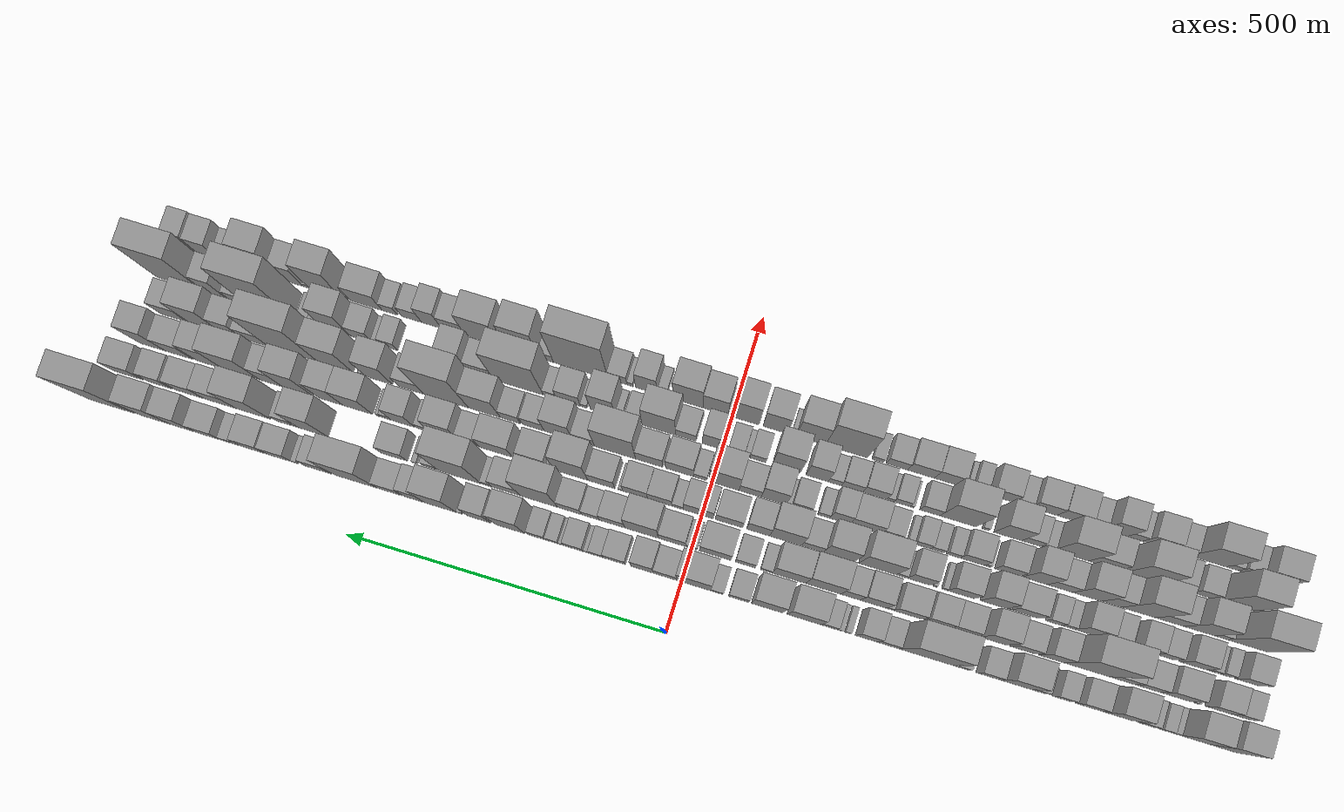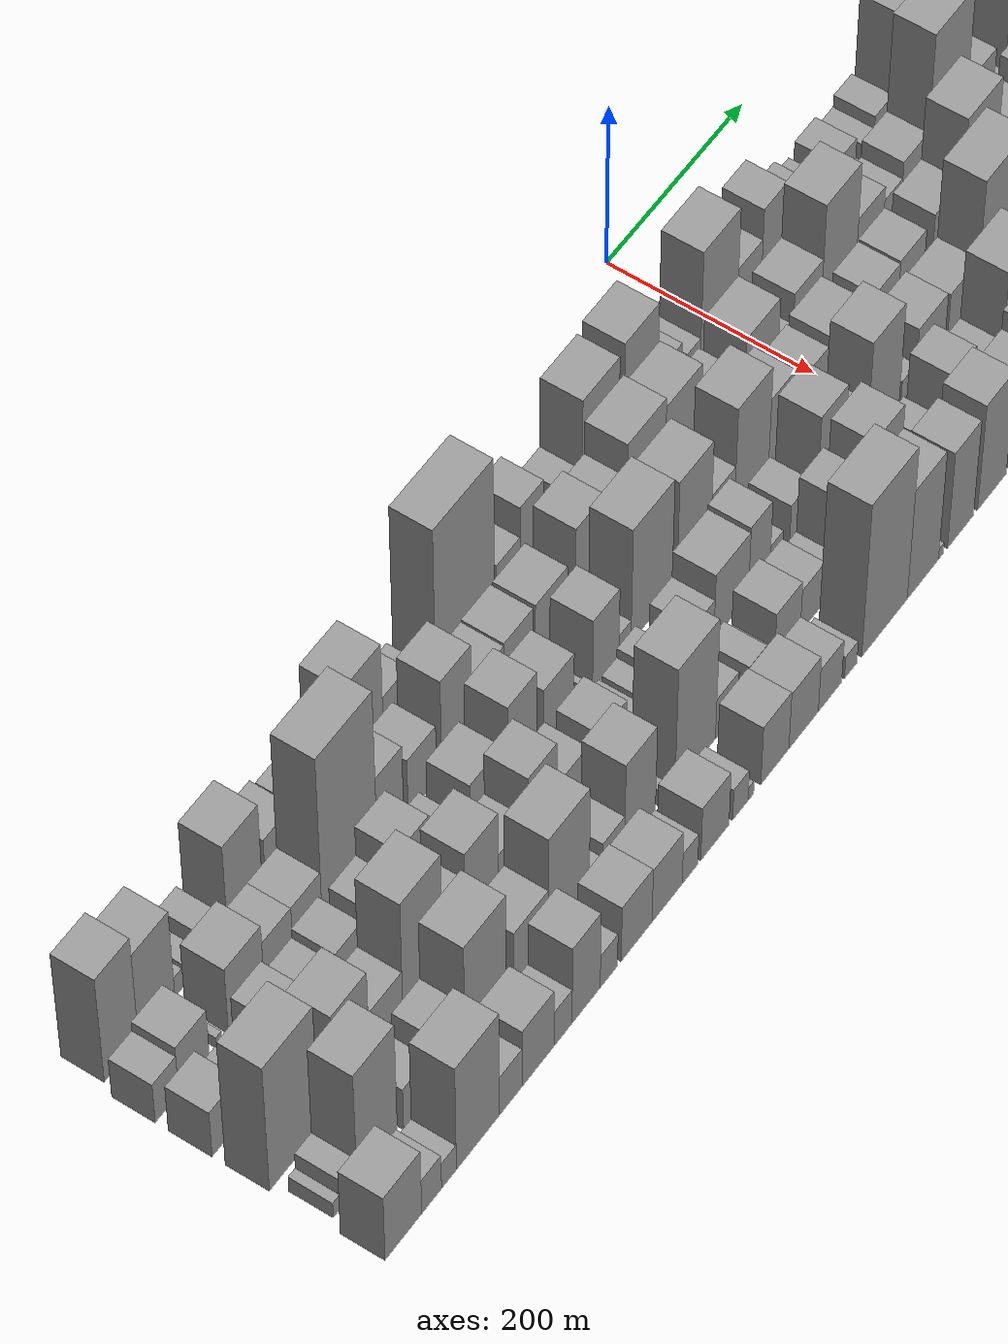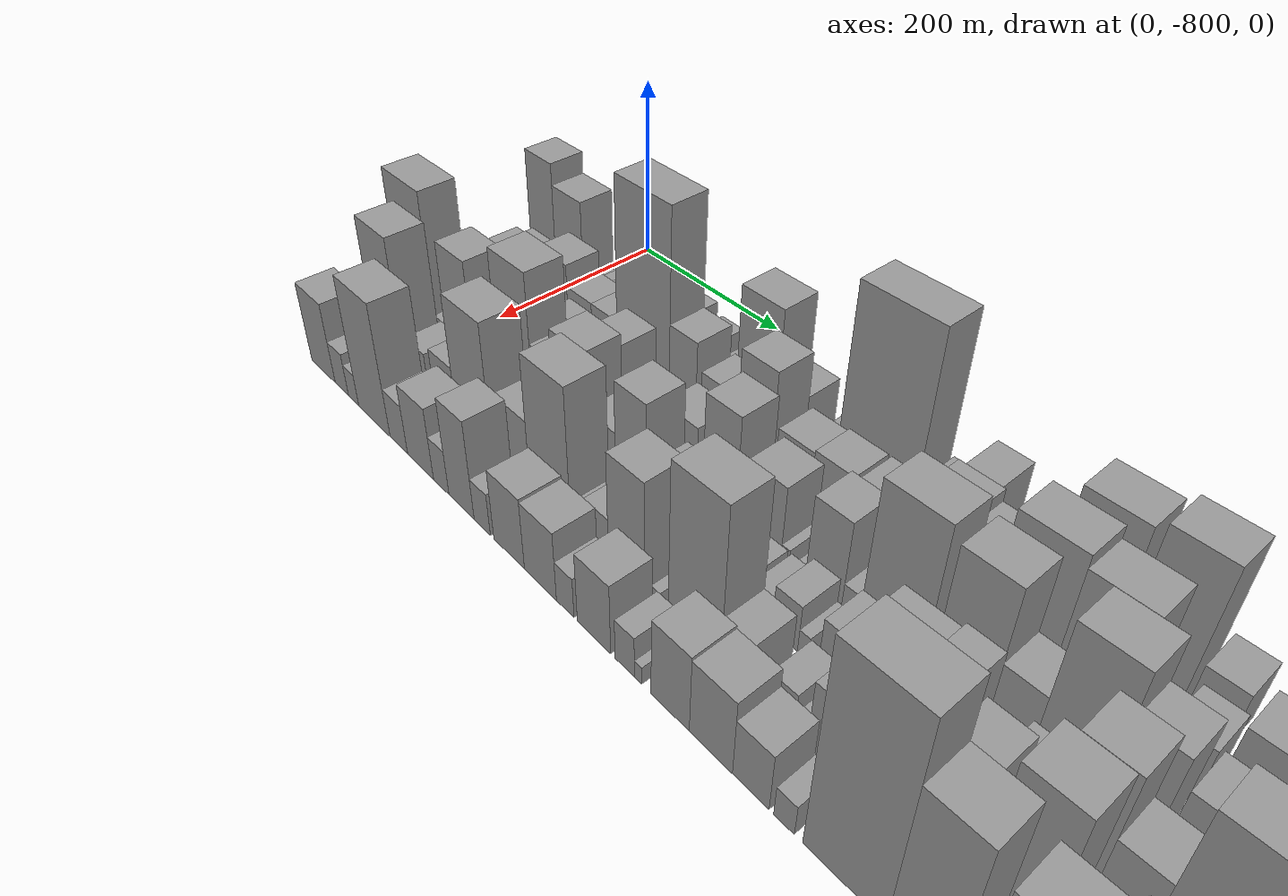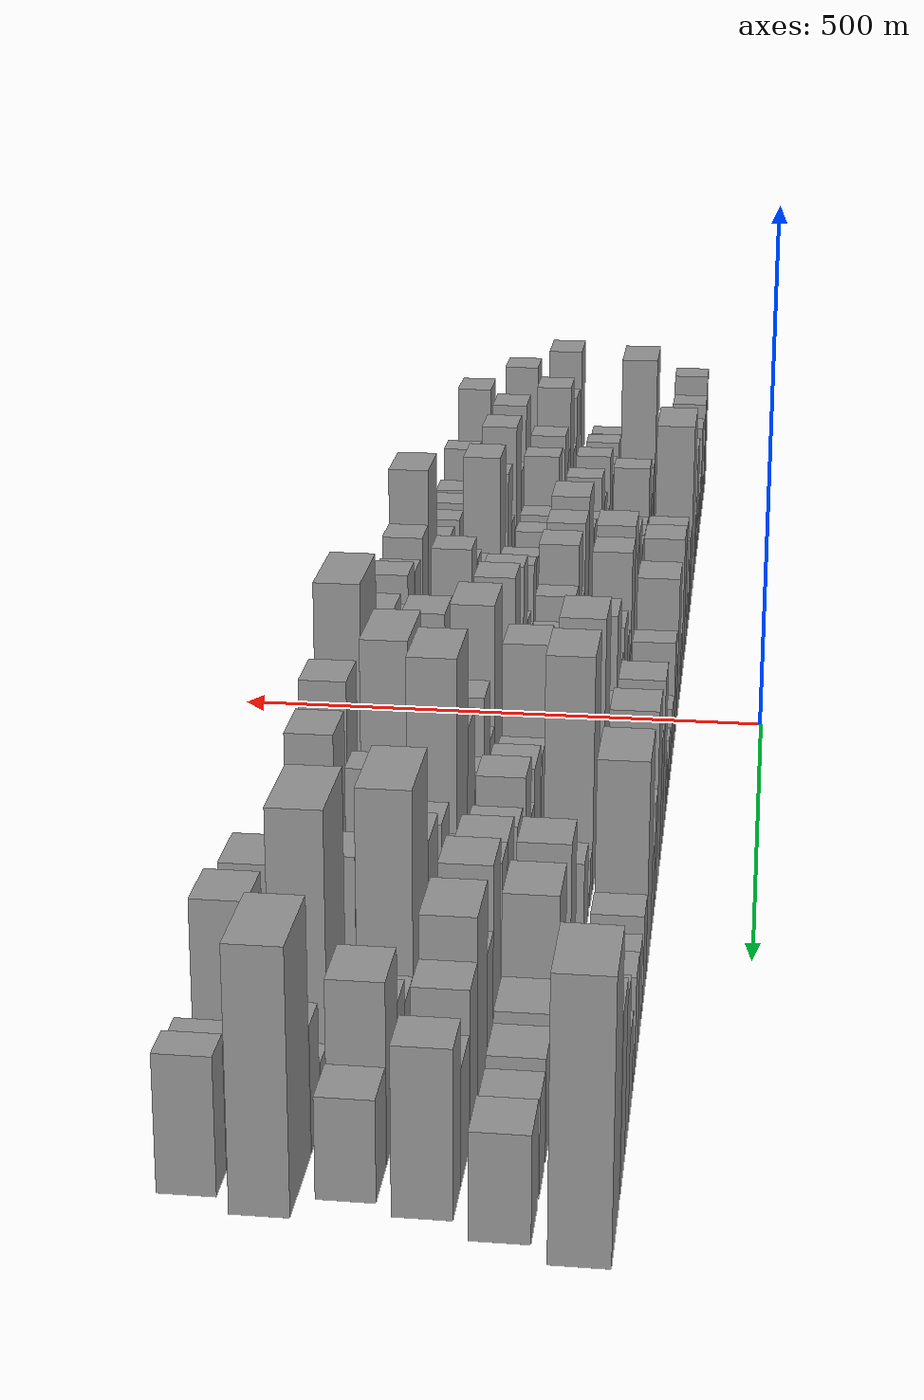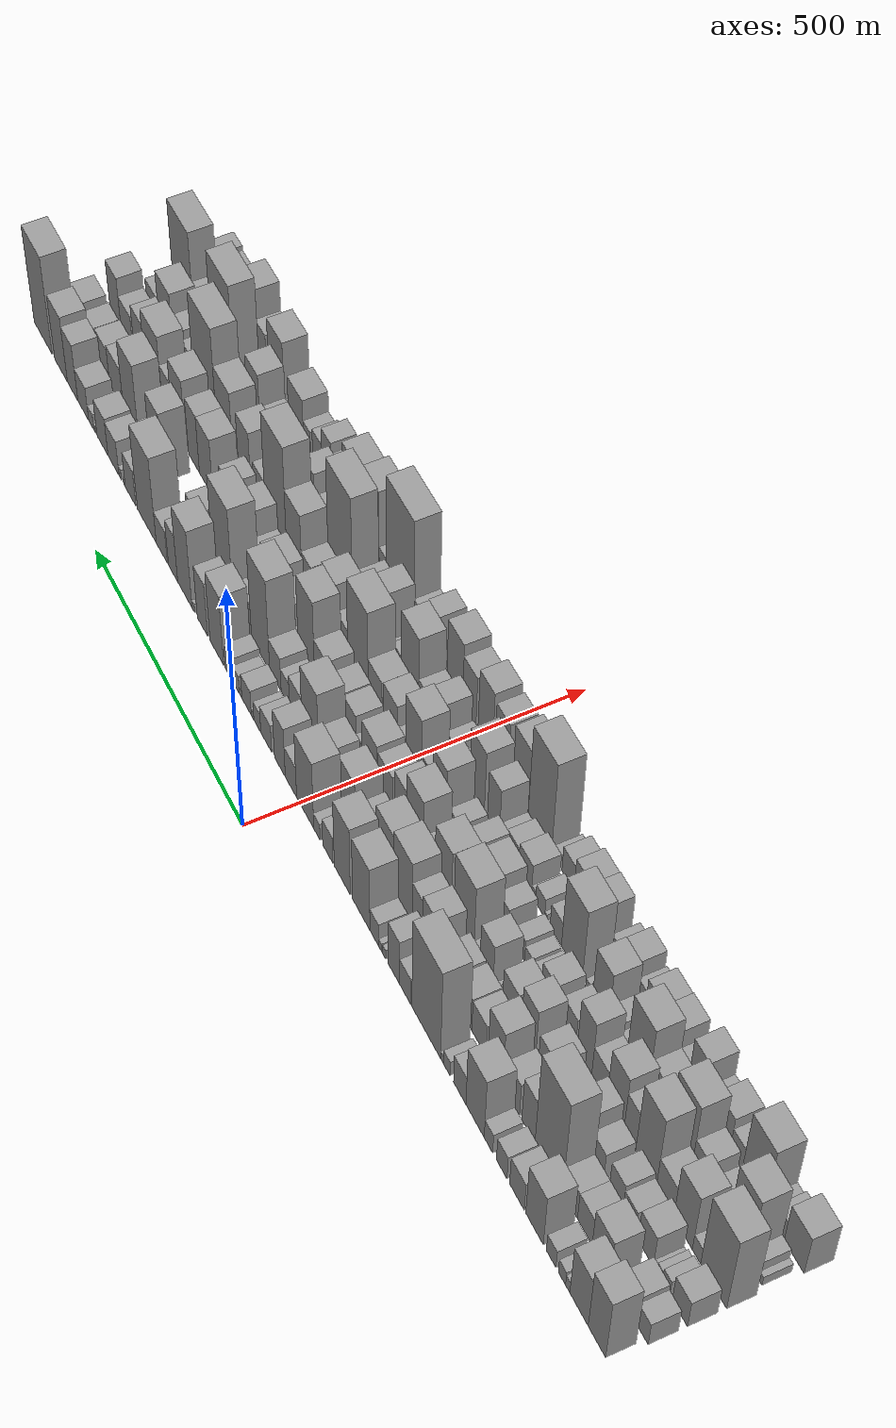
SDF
<sdf version="1.6">
 <world name="default">
  <scene>
   <sky><clouds><speed>12</speed></clouds></sky>
   <ambient>0.4 0.4 0.4 1</ambient>
   <background>0.7 0.7 0.7 1</background>
   <shadows>1</shadows>
  </scene>
  <gravity>0 0 -9.8066</gravity>
  <magnetic_field>6e-06 2.3e-05 -4.2e-05</magnetic_field>
  <physics default="0" name="default_physics" type="ode">
   <ode>
    <solver>
     <type>quick</type>
     <iters>10</iters>
     <sor>1.0</sor>
     <use_dynamic_moi_rescaling>0</use_dynamic_moi_rescaling>
    </solver>
    <constraints>
     <cfm>0</cfm>
     <erp>0.2</erp>
     <contact_max_correcting_vel>100</contact_max_correcting_vel>
     <contact_surface_layer>0.001</contact_surface_layer>
    </constraints>
   </ode>
   <max_step_size>0.004</max_step_size>
   <real_time_factor>1</real_time_factor>
   <real_time_update_rate>250</real_time_update_rate>
  </physics>
  <light name="sun" type="directional">
   <pose>0 0 10 0 0 0</pose>
   <diffuse>0.8 0.8 0.8 1</diffuse>
   <specular>0.2 0.2 0.2 1</specular>
   <attenuation>
    <range>1000</range>
    <constant>0.9</constant>
    <linear>0.01</linear>
    <quadratic>0.001</quadratic>
   </attenuation>
   <direction>-0.5 0.1 -0.9</direction>
  </light>
  <model name="building_1">
   <static>1</static>
   <pose>100.0000 -831.2529 0 0.000000 0.000000 0.000000</pose>
   <link name="link">
    <pose>0 0 72.00 0 0 0</pose>
    <collision name="collision"><geometry><box><size>40.0000 43.4942 144.0000</size></box></geometry></collision>
    <visual name="visual">
     <cast_shadows>0</cast_shadows>
     <geometry><box><size>40.0000 43.4942 144.0000</size></box></geometry>
     <material>
      <script>
       <uri>model://grey_wall/materials/scripts</uri>
       <uri>model://grey_wall/materials/textures</uri>
       <name>vrc/grey_wall</name>
      </script>
     </material>
    </visual>
   </link>
  </model>
  <model name="building_2">
   <static>1</static>
   <pose>100.0000 -786.3513 0 0.000000 0.000000 0.000000</pose>
   <link name="link">
    <pose>0 0 60.00 0 0 0</pose>
    <collision name="collision"><geometry><box><size>40.0000 46.3092 120.0000</size></box></geometry></collision>
    <visual name="visual">
     <cast_shadows>0</cast_shadows>
     <geometry><box><size>40.0000 46.3092 120.0000</size></box></geometry>
     <material>
      <script>
       <uri>model://grey_wall/materials/scripts</uri>
       <uri>model://grey_wall/materials/textures</uri>
       <name>vrc/grey_wall</name>
      </script>
     </material>
    </visual>
   </link>
  </model>
  <model name="building_3">
   <static>1</static>
   <pose>100.0000 -757.7851 0 0.000000 0.000000 0.000000</pose>
   <link name="link">
    <pose>0 0 13.50 0 0 0</pose>
    <collision name="collision"><geometry><box><size>40.0000 10.8232 27.0000</size></box></geometry></collision>
    <visual name="visual">
     <cast_shadows>0</cast_shadows>
     <geometry><box><size>40.0000 10.8232 27.0000</size></box></geometry>
     <material>
      <script>
       <uri>model://grey_wall/materials/scripts</uri>
       <uri>model://grey_wall/materials/textures</uri>
       <name>vrc/grey_wall</name>
      </script>
     </material>
    </visual>
   </link>
  </model>
  <model name="building_4">
   <static>1</static>
   <pose>100.0000 -743.1036 0 0.000000 0.000000 0.000000</pose>
   <link name="link">
    <pose>0 0 16.50 0 0 0</pose>
    <collision name="collision"><geometry><box><size>40.0000 18.5398 33.0000</size></box></geometry></collision>
    <visual name="visual">
     <cast_shadows>0</cast_shadows>
     <geometry><box><size>40.0000 18.5398 33.0000</size></box></geometry>
     <material>
      <script>
       <uri>model://grey_wall/materials/scripts</uri>
       <uri>model://grey_wall/materials/textures</uri>
       <name>vrc/grey_wall</name>
      </script>
     </material>
    </visual>
   </link>
  </model>
  <model name="building_5">
   <static>1</static>
   <pose>100.0000 -715.5451 0 0.000000 0.000000 0.000000</pose>
   <link name="link">
    <pose>0 0 21.00 0 0 0</pose>
    <collision name="collision"><geometry><box><size>40.0000 24.5773 42.0000</size></box></geometry></collision>
    <visual name="visual">
     <cast_shadows>0</cast_shadows>
     <geometry><box><size>40.0000 24.5773 42.0000</size></box></geometry>
     <material>
      <script>
       <uri>model://grey_wall/materials/scripts</uri>
       <uri>model://grey_wall/materials/textures</uri>
       <name>vrc/grey_wall</name>
      </script>
     </material>
    </visual>
   </link>
  </model>
  <model name="building_6">
   <static>1</static>
   <pose>100.0000 -672.3743 0 0.000000 0.000000 0.000000</pose>
   <link name="link">
    <pose>0 0 60.00 0 0 0</pose>
    <collision name="collision"><geometry><box><size>40.0000 45.7643 120.0000</size></box></geometry></collision>
    <visual name="visual">
     <cast_shadows>0</cast_shadows>
     <geometry><box><size>40.0000 45.7643 120.0000</size></box></geometry>
     <material>
      <script>
       <uri>model://grey_wall/materials/scripts</uri>
       <uri>model://grey_wall/materials/textures</uri>
       <name>vrc/grey_wall</name>
      </script>
     </material>
    </visual>
   </link>
  </model>
  <model name="building_7">
   <static>1</static>
   <pose>100.0000 -626.1517 0 0.000000 0.000000 0.000000</pose>
   <link name="link">
    <pose>0 0 33.00 0 0 0</pose>
    <collision name="collision"><geometry><box><size>40.0000 38.6808 66.0000</size></box></geometry></collision>
    <visual name="visual">
     <cast_shadows>0</cast_shadows>
     <geometry><box><size>40.0000 38.6808 66.0000</size></box></geometry>
     <material>
      <script>
       <uri>model://grey_wall/materials/scripts</uri>
       <uri>model://grey_wall/materials/textures</uri>
       <name>vrc/grey_wall</name>
      </script>
     </material>
    </visual>
   </link>
  </model>
  <model name="building_8">
   <static>1</static>
   <pose>100.0000 -585.7015 0 0.000000 0.000000 0.000000</pose>
   <link name="link">
    <pose>0 0 27.00 0 0 0</pose>
    <collision name="collision"><geometry><box><size>40.0000 28.2197 54.0000</size></box></geometry></collision>
    <visual name="visual">
     <cast_shadows>0</cast_shadows>
     <geometry><box><size>40.0000 28.2197 54.0000</size></box></geometry>
     <material>
      <script>
       <uri>model://grey_wall/materials/scripts</uri>
       <uri>model://grey_wall/materials/textures</uri>
       <name>vrc/grey_wall</name>
      </script>
     </material>
    </visual>
   </link>
  </model>
  <model name="building_9">
   <static>1</static>
   <pose>100.0000 -550.1398 0 0.000000 0.000000 0.000000</pose>
   <link name="link">
    <pose>0 0 22.50 0 0 0</pose>
    <collision name="collision"><geometry><box><size>40.0000 22.9038 45.0000</size></box></geometry></collision>
    <visual name="visual">
     <cast_shadows>0</cast_shadows>
     <geometry><box><size>40.0000 22.9038 45.0000</size></box></geometry>
     <material>
      <script>
       <uri>model://grey_wall/materials/scripts</uri>
       <uri>model://grey_wall/materials/textures</uri>
       <name>vrc/grey_wall</name>
      </script>
     </material>
    </visual>
   </link>
  </model>
  <model name="building_10">
   <static>1</static>
   <pose>100.0000 -513.6906 0 0.000000 0.000000 0.000000</pose>
   <link name="link">
    <pose>0 0 69.00 0 0 0</pose>
    <collision name="collision"><geometry><box><size>40.0000 49.9946 138.0000</size></box></geometry></collision>
    <visual name="visual">
     <cast_shadows>0</cast_shadows>
     <geometry><box><size>40.0000 49.9946 138.0000</size></box></geometry>
     <material>
      <script>
       <uri>model://grey_wall/materials/scripts</uri>
       <uri>model://grey_wall/materials/textures</uri>
       <name>vrc/grey_wall</name>
      </script>
     </material>
    </visual>
   </link>
  </model>
  <model name="building_11">
   <static>1</static>
   <pose>100.0000 -471.7270 0 0.000000 0.000000 0.000000</pose>
   <link name="link">
    <pose>0 0 33.00 0 0 0</pose>
    <collision name="collision"><geometry><box><size>40.0000 33.9325 66.0000</size></box></geometry></collision>
    <visual name="visual">
     <cast_shadows>0</cast_shadows>
     <geometry><box><size>40.0000 33.9325 66.0000</size></box></geometry>
     <material>
      <script>
       <uri>model://grey_wall/materials/scripts</uri>
       <uri>model://grey_wall/materials/textures</uri>
       <name>vrc/grey_wall</name>
      </script>
     </material>
    </visual>
   </link>
  </model>
  <model name="building_12">
   <static>1</static>
   <pose>100.0000 -435.5346 0 0.000000 0.000000 0.000000</pose>
   <link name="link">
    <pose>0 0 16.50 0 0 0</pose>
    <collision name="collision"><geometry><box><size>40.0000 18.4524 33.0000</size></box></geometry></collision>
    <visual name="visual">
     <cast_shadows>0</cast_shadows>
     <geometry><box><size>40.0000 18.4524 33.0000</size></box></geometry>
     <material>
      <script>
       <uri>model://grey_wall/materials/scripts</uri>
       <uri>model://grey_wall/materials/textures</uri>
       <name>vrc/grey_wall</name>
      </script>
     </material>
    </visual>
   </link>
  </model>
  <model name="building_13">
   <static>1</static>
   <pose>100.0000 -422.3564 0 0.000000 0.000000 0.000000</pose>
   <link name="link">
    <pose>0 0 9.00 0 0 0</pose>
    <collision name="collision"><geometry><box><size>40.0000 7.9039 18.0000</size></box></geometry></collision>
    <visual name="visual">
     <cast_shadows>0</cast_shadows>
     <geometry><box><size>40.0000 7.9039 18.0000</size></box></geometry>
     <material>
      <script>
       <uri>model://grey_wall/materials/scripts</uri>
       <uri>model://grey_wall/materials/textures</uri>
       <name>vrc/grey_wall</name>
      </script>
     </material>
    </visual>
   </link>
  </model>
  <model name="building_14">
   <static>1</static>
   <pose>100.0000 -377.7284 0 0.000000 0.000000 0.000000</pose>
   <link name="link">
    <pose>0 0 102.00 0 0 0</pose>
    <collision name="collision"><geometry><box><size>40.0000 81.3520 204.0000</size></box></geometry></collision>
    <visual name="visual">
     <cast_shadows>0</cast_shadows>
     <geometry><box><size>40.0000 81.3520 204.0000</size></box></geometry>
     <material>
      <script>
       <uri>model://grey_wall/materials/scripts</uri>
       <uri>model://grey_wall/materials/textures</uri>
       <name>vrc/grey_wall</name>
      </script>
     </material>
    </visual>
   </link>
  </model>
  <model name="building_15">
   <static>1</static>
   <pose>100.0000 -317.7587 0 0.000000 0.000000 0.000000</pose>
   <link name="link">
    <pose>0 0 30.00 0 0 0</pose>
    <collision name="collision"><geometry><box><size>40.0000 32.5875 60.0000</size></box></geometry></collision>
    <visual name="visual">
     <cast_shadows>0</cast_shadows>
     <geometry><box><size>40.0000 32.5875 60.0000</size></box></geometry>
     <material>
      <script>
       <uri>model://grey_wall/materials/scripts</uri>
       <uri>model://grey_wall/materials/textures</uri>
       <name>vrc/grey_wall</name>
      </script>
     </material>
    </visual>
   </link>
  </model>
  <model name="building_16">
   <static>1</static>
   <pose>100.0000 -285.1396 0 0.000000 0.000000 0.000000</pose>
   <link name="link">
    <pose>0 0 49.50 0 0 0</pose>
    <collision name="collision"><geometry><box><size>40.0000 32.6508 99.0000</size></box></geometry></collision>
    <visual name="visual">
     <cast_shadows>0</cast_shadows>
     <geometry><box><size>40.0000 32.6508 99.0000</size></box></geometry>
     <material>
      <script>
       <uri>model://grey_wall/materials/scripts</uri>
       <uri>model://grey_wall/materials/textures</uri>
       <name>vrc/grey_wall</name>
      </script>
     </material>
    </visual>
   </link>
  </model>
  <model name="building_17">
   <static>1</static>
   <pose>100.0000 -257.1645 0 0.000000 0.000000 0.000000</pose>
   <link name="link">
    <pose>0 0 10.50 0 0 0</pose>
    <collision name="collision"><geometry><box><size>40.0000 9.2992 21.0000</size></box></geometry></collision>
    <visual name="visual">
     <cast_shadows>0</cast_shadows>
     <geometry><box><size>40.0000 9.2992 21.0000</size></box></geometry>
     <material>
      <script>
       <uri>model://grey_wall/materials/scripts</uri>
       <uri>model://grey_wall/materials/textures</uri>
       <name>vrc/grey_wall</name>
      </script>
     </material>
    </visual>
   </link>
  </model>
  <model name="building_18">
   <static>1</static>
   <pose>100.0000 -245.1105 0 0.000000 0.000000 0.000000</pose>
   <link name="link">
    <pose>0 0 9.00 0 0 0</pose>
    <collision name="collision"><geometry><box><size>40.0000 8.8089 18.0000</size></box></geometry></collision>
    <visual name="visual">
     <cast_shadows>0</cast_shadows>
     <geometry><box><size>40.0000 8.8089 18.0000</size></box></geometry>
     <material>
      <script>
       <uri>model://grey_wall/materials/scripts</uri>
       <uri>model://grey_wall/materials/textures</uri>
       <name>vrc/grey_wall</name>
      </script>
     </material>
    </visual>
   </link>
  </model>
  <model name="building_19">
   <static>1</static>
   <pose>100.0000 -227.7287 0 0.000000 0.000000 0.000000</pose>
   <link name="link">
    <pose>0 0 25.50 0 0 0</pose>
    <collision name="collision"><geometry><box><size>40.0000 25.9547 51.0000</size></box></geometry></collision>
    <visual name="visual">
     <cast_shadows>0</cast_shadows>
     <geometry><box><size>40.0000 25.9547 51.0000</size></box></geometry>
     <material>
      <script>
       <uri>model://grey_wall/materials/scripts</uri>
       <uri>model://grey_wall/materials/textures</uri>
       <name>vrc/grey_wall</name>
      </script>
     </material>
    </visual>
   </link>
  </model>
  <model name="building_20">
   <static>1</static>
   <pose>100.0000 -188.9263 0 0.000000 0.000000 0.000000</pose>
   <link name="link">
    <pose>0 0 70.50 0 0 0</pose>
    <collision name="collision"><geometry><box><size>40.0000 51.6502 141.0000</size></box></geometry></collision>
    <visual name="visual">
     <cast_shadows>0</cast_shadows>
     <geometry><box><size>40.0000 51.6502 141.0000</size></box></geometry>
     <material>
      <script>
       <uri>model://grey_wall/materials/scripts</uri>
       <uri>model://grey_wall/materials/textures</uri>
       <name>vrc/grey_wall</name>
      </script>
     </material>
    </visual>
   </link>
  </model>
  <model name="building_21">
   <static>1</static>
   <pose>100.0000 -131.9172 0 0.000000 0.000000 0.000000</pose>
   <link name="link">
    <pose>0 0 75.00 0 0 0</pose>
    <collision name="collision"><geometry><box><size>40.0000 48.3680 150.0000</size></box></geometry></collision>
    <visual name="visual">
     <cast_shadows>0</cast_shadows>
     <geometry><box><size>40.0000 48.3680 150.0000</size></box></geometry>
     <material>
      <script>
       <uri>model://grey_wall/materials/scripts</uri>
       <uri>model://grey_wall/materials/textures</uri>
       <name>vrc/grey_wall</name>
      </script>
     </material>
    </visual>
   </link>
  </model>
  <model name="building_22">
   <static>1</static>
   <pose>100.0000 -87.9944 0 0.000000 0.000000 0.000000</pose>
   <link name="link">
    <pose>0 0 30.00 0 0 0</pose>
    <collision name="collision"><geometry><box><size>40.0000 31.4775 60.0000</size></box></geometry></collision>
    <visual name="visual">
     <cast_shadows>0</cast_shadows>
     <geometry><box><size>40.0000 31.4775 60.0000</size></box></geometry>
     <material>
      <script>
       <uri>model://grey_wall/materials/scripts</uri>
       <uri>model://grey_wall/materials/textures</uri>
       <name>vrc/grey_wall</name>
      </script>
     </material>
    </visual>
   </link>
  </model>
  <model name="building_23">
   <static>1</static>
   <pose>100.0000 -54.5327 0 0.000000 0.000000 0.000000</pose>
   <link name="link">
    <pose>0 0 18.00 0 0 0</pose>
    <collision name="collision"><geometry><box><size>40.0000 19.4459 36.0000</size></box></geometry></collision>
    <visual name="visual">
     <cast_shadows>0</cast_shadows>
     <geometry><box><size>40.0000 19.4459 36.0000</size></box></geometry>
     <material>
      <script>
       <uri>model://grey_wall/materials/scripts</uri>
       <uri>model://grey_wall/materials/textures</uri>
       <name>vrc/grey_wall</name>
      </script>
     </material>
    </visual>
   </link>
  </model>
  <model name="building_24">
   <static>1</static>
   <pose>100.0000 -18.0642 0 0.000000 0.000000 0.000000</pose>
   <link name="link">
    <pose>0 0 73.50 0 0 0</pose>
    <collision name="collision"><geometry><box><size>40.0000 53.4911 147.0000</size></box></geometry></collision>
    <visual name="visual">
     <cast_shadows>0</cast_shadows>
     <geometry><box><size>40.0000 53.4911 147.0000</size></box></geometry>
     <material>
      <script>
       <uri>model://grey_wall/materials/scripts</uri>
       <uri>model://grey_wall/materials/textures</uri>
       <name>vrc/grey_wall</name>
      </script>
     </material>
    </visual>
   </link>
  </model>
  <model name="building_25">
   <static>1</static>
   <pose>100.0000 26.5422 0 0.000000 0.000000 0.000000</pose>
   <link name="link">
    <pose>0 0 34.50 0 0 0</pose>
    <collision name="collision"><geometry><box><size>40.0000 35.7216 69.0000</size></box></geometry></collision>
    <visual name="visual">
     <cast_shadows>0</cast_shadows>
     <geometry><box><size>40.0000 35.7216 69.0000</size></box></geometry>
     <material>
      <script>
       <uri>model://grey_wall/materials/scripts</uri>
       <uri>model://grey_wall/materials/textures</uri>
       <name>vrc/grey_wall</name>
      </script>
     </material>
    </visual>
   </link>
  </model>
  <model name="building_26">
   <static>1</static>
   <pose>100.0000 61.6217 0 0.000000 0.000000 0.000000</pose>
   <link name="link">
    <pose>0 0 54.00 0 0 0</pose>
    <collision name="collision"><geometry><box><size>40.0000 34.4375 108.0000</size></box></geometry></collision>
    <visual name="visual">
     <cast_shadows>0</cast_shadows>
     <geometry><box><size>40.0000 34.4375 108.0000</size></box></geometry>
     <material>
      <script>
       <uri>model://grey_wall/materials/scripts</uri>
       <uri>model://grey_wall/materials/textures</uri>
       <name>vrc/grey_wall</name>
      </script>
     </material>
    </visual>
   </link>
  </model>
  <model name="building_27">
   <static>1</static>
   <pose>100.0000 105.4177 0 0.000000 0.000000 0.000000</pose>
   <link name="link">
    <pose>0 0 30.00 0 0 0</pose>
    <collision name="collision"><geometry><box><size>40.0000 35.1545 60.0000</size></box></geometry></collision>
    <visual name="visual">
     <cast_shadows>0</cast_shadows>
     <geometry><box><size>40.0000 35.1545 60.0000</size></box></geometry>
     <material>
      <script>
       <uri>model://grey_wall/materials/scripts</uri>
       <uri>model://grey_wall/materials/textures</uri>
       <name>vrc/grey_wall</name>
      </script>
     </material>
    </visual>
   </link>
  </model>
  <model name="building_28">
   <static>1</static>
   <pose>100.0000 134.3022 0 0.000000 0.000000 0.000000</pose>
   <link name="link">
    <pose>0 0 21.00 0 0 0</pose>
    <collision name="collision"><geometry><box><size>40.0000 22.6145 42.0000</size></box></geometry></collision>
    <visual name="visual">
     <cast_shadows>0</cast_shadows>
     <geometry><box><size>40.0000 22.6145 42.0000</size></box></geometry>
     <material>
      <script>
       <uri>model://grey_wall/materials/scripts</uri>
       <uri>model://grey_wall/materials/textures</uri>
       <name>vrc/grey_wall</name>
      </script>
     </material>
    </visual>
   </link>
  </model>
  <model name="building_29">
   <static>1</static>
   <pose>100.0000 149.7486 0 0.000000 0.000000 0.000000</pose>
   <link name="link">
    <pose>0 0 9.00 0 0 0</pose>
    <collision name="collision"><geometry><box><size>40.0000 8.2783 18.0000</size></box></geometry></collision>
    <visual name="visual">
     <cast_shadows>0</cast_shadows>
     <geometry><box><size>40.0000 8.2783 18.0000</size></box></geometry>
     <material>
      <script>
       <uri>model://grey_wall/materials/scripts</uri>
       <uri>model://grey_wall/materials/textures</uri>
       <name>vrc/grey_wall</name>
      </script>
     </material>
    </visual>
   </link>
  </model>
  <model name="building_30">
   <static>1</static>
   <pose>100.0000 169.3452 0 0.000000 0.000000 0.000000</pose>
   <link name="link">
    <pose>0 0 27.00 0 0 0</pose>
    <collision name="collision"><geometry><box><size>40.0000 30.9149 54.0000</size></box></geometry></collision>
    <visual name="visual">
     <cast_shadows>0</cast_shadows>
     <geometry><box><size>40.0000 30.9149 54.0000</size></box></geometry>
     <material>
      <script>
       <uri>model://grey_wall/materials/scripts</uri>
       <uri>model://grey_wall/materials/textures</uri>
       <name>vrc/grey_wall</name>
      </script>
     </material>
    </visual>
   </link>
  </model>
  <model name="building_31">
   <static>1</static>
   <pose>100.0000 188.7054 0 0.000000 0.000000 0.000000</pose>
   <link name="link">
    <pose>0 0 9.00 0 0 0</pose>
    <collision name="collision"><geometry><box><size>40.0000 7.8055 18.0000</size></box></geometry></collision>
    <visual name="visual">
     <cast_shadows>0</cast_shadows>
     <geometry><box><size>40.0000 7.8055 18.0000</size></box></geometry>
     <material>
      <script>
       <uri>model://grey_wall/materials/scripts</uri>
       <uri>model://grey_wall/materials/textures</uri>
       <name>vrc/grey_wall</name>
      </script>
     </material>
    </visual>
   </link>
  </model>
  <model name="building_32">
   <static>1</static>
   <pose>100.0000 202.5710 0 0.000000 0.000000 0.000000</pose>
   <link name="link">
    <pose>0 0 19.50 0 0 0</pose>
    <collision name="collision"><geometry><box><size>40.0000 19.9259 39.0000</size></box></geometry></collision>
    <visual name="visual">
     <cast_shadows>0</cast_shadows>
     <geometry><box><size>40.0000 19.9259 39.0000</size></box></geometry>
     <material>
      <script>
       <uri>model://grey_wall/materials/scripts</uri>
       <uri>model://grey_wall/materials/textures</uri>
       <name>vrc/grey_wall</name>
      </script>
     </material>
    </visual>
   </link>
  </model>
  <model name="building_33">
   <static>1</static>
   <pose>100.0000 226.2784 0 0.000000 0.000000 0.000000</pose>
   <link name="link">
    <pose>0 0 27.00 0 0 0</pose>
    <collision name="collision"><geometry><box><size>40.0000 27.4888 54.0000</size></box></geometry></collision>
    <visual name="visual">
     <cast_shadows>0</cast_shadows>
     <geometry><box><size>40.0000 27.4888 54.0000</size></box></geometry>
     <material>
      <script>
       <uri>model://grey_wall/materials/scripts</uri>
       <uri>model://grey_wall/materials/textures</uri>
       <name>vrc/grey_wall</name>
      </script>
     </material>
    </visual>
   </link>
  </model>
  <model name="building_34">
   <static>1</static>
   <pose>100.0000 267.9488 0 0.000000 0.000000 0.000000</pose>
   <link name="link">
    <pose>0 0 75.00 0 0 0</pose>
    <collision name="collision"><geometry><box><size>40.0000 45.8519 150.0000</size></box></geometry></collision>
    <visual name="visual">
     <cast_shadows>0</cast_shadows>
     <geometry><box><size>40.0000 45.8519 150.0000</size></box></geometry>
     <material>
      <script>
       <uri>model://grey_wall/materials/scripts</uri>
       <uri>model://grey_wall/materials/textures</uri>
       <name>vrc/grey_wall</name>
      </script>
     </material>
    </visual>
   </link>
  </model>
  <model name="building_35">
   <static>1</static>
   <pose>100.0000 316.5658 0 0.000000 0.000000 0.000000</pose>
   <link name="link">
    <pose>0 0 57.00 0 0 0</pose>
    <collision name="collision"><geometry><box><size>40.0000 35.3823 114.0000</size></box></geometry></collision>
    <visual name="visual">
     <cast_shadows>0</cast_shadows>
     <geometry><box><size>40.0000 35.3823 114.0000</size></box></geometry>
     <material>
      <script>
       <uri>model://grey_wall/materials/scripts</uri>
       <uri>model://grey_wall/materials/textures</uri>
       <name>vrc/grey_wall</name>
      </script>
     </material>
    </visual>
   </link>
  </model>
  <model name="building_36">
   <static>1</static>
   <pose>100.0000 347.5874 0 0.000000 0.000000 0.000000</pose>
   <link name="link">
    <pose>0 0 9.00 0 0 0</pose>
    <collision name="collision"><geometry><box><size>40.0000 8.6609 18.0000</size></box></geometry></collision>
    <visual name="visual">
     <cast_shadows>0</cast_shadows>
     <geometry><box><size>40.0000 8.6609 18.0000</size></box></geometry>
     <material>
      <script>
       <uri>model://grey_wall/materials/scripts</uri>
       <uri>model://grey_wall/materials/textures</uri>
       <name>vrc/grey_wall</name>
      </script>
     </material>
    </visual>
   </link>
  </model>
  <model name="building_37">
   <static>1</static>
   <pose>100.0000 376.8296 0 0.000000 0.000000 0.000000</pose>
   <link name="link">
    <pose>0 0 82.50 0 0 0</pose>
    <collision name="collision"><geometry><box><size>40.0000 49.8235 165.0000</size></box></geometry></collision>
    <visual name="visual">
     <cast_shadows>0</cast_shadows>
     <geometry><box><size>40.0000 49.8235 165.0000</size></box></geometry>
     <material>
      <script>
       <uri>model://grey_wall/materials/scripts</uri>
       <uri>model://grey_wall/materials/textures</uri>
       <name>vrc/grey_wall</name>
      </script>
     </material>
    </visual>
   </link>
  </model>
  <model name="building_38">
   <static>1</static>
   <pose>100.0000 417.7137 0 0.000000 0.000000 0.000000</pose>
   <link name="link">
    <pose>0 0 49.50 0 0 0</pose>
    <collision name="collision"><geometry><box><size>40.0000 31.9446 99.0000</size></box></geometry></collision>
    <visual name="visual">
     <cast_shadows>0</cast_shadows>
     <geometry><box><size>40.0000 31.9446 99.0000</size></box></geometry>
     <material>
      <script>
       <uri>model://grey_wall/materials/scripts</uri>
       <uri>model://grey_wall/materials/textures</uri>
       <name>vrc/grey_wall</name>
      </script>
     </material>
    </visual>
   </link>
  </model>
  <model name="building_39">
   <static>1</static>
   <pose>100.0000 457.2777 0 0.000000 0.000000 0.000000</pose>
   <link name="link">
    <pose>0 0 34.50 0 0 0</pose>
    <collision name="collision"><geometry><box><size>40.0000 39.1835 69.0000</size></box></geometry></collision>
    <visual name="visual">
     <cast_shadows>0</cast_shadows>
     <geometry><box><size>40.0000 39.1835 69.0000</size></box></geometry>
     <material>
      <script>
       <uri>model://grey_wall/materials/scripts</uri>
       <uri>model://grey_wall/materials/textures</uri>
       <name>vrc/grey_wall</name>
      </script>
     </material>
    </visual>
   </link>
  </model>
  <model name="building_40">
   <static>1</static>
   <pose>100.0000 510.3167 0 0.000000 0.000000 0.000000</pose>
   <link name="link">
    <pose>0 0 90.00 0 0 0</pose>
    <collision name="collision"><geometry><box><size>40.0000 66.8946 180.0000</size></box></geometry></collision>
    <visual name="visual">
     <cast_shadows>0</cast_shadows>
     <geometry><box><size>40.0000 66.8946 180.0000</size></box></geometry>
     <material>
      <script>
       <uri>model://grey_wall/materials/scripts</uri>
       <uri>model://grey_wall/materials/textures</uri>
       <name>vrc/grey_wall</name>
      </script>
     </material>
    </visual>
   </link>
  </model>
  <model name="building_41">
   <static>1</static>
   <pose>100.0000 568.8405 0 0.000000 0.000000 0.000000</pose>
   <link name="link">
    <pose>0 0 37.50 0 0 0</pose>
    <collision name="collision"><geometry><box><size>40.0000 38.1529 75.0000</size></box></geometry></collision>
    <visual name="visual">
     <cast_shadows>0</cast_shadows>
     <geometry><box><size>40.0000 38.1529 75.0000</size></box></geometry>
     <material>
      <script>
       <uri>model://grey_wall/materials/scripts</uri>
       <uri>model://grey_wall/materials/textures</uri>
       <name>vrc/grey_wall</name>
      </script>
     </material>
    </visual>
   </link>
  </model>
  <model name="building_42">
   <static>1</static>
   <pose>100.0000 591.0916 0 0.000000 0.000000 0.000000</pose>
   <link name="link">
    <pose>0 0 7.50 0 0 0</pose>
    <collision name="collision"><geometry><box><size>40.0000 6.3492 15.0000</size></box></geometry></collision>
    <visual name="visual">
     <cast_shadows>0</cast_shadows>
     <geometry><box><size>40.0000 6.3492 15.0000</size></box></geometry>
     <material>
      <script>
       <uri>model://grey_wall/materials/scripts</uri>
       <uri>model://grey_wall/materials/textures</uri>
       <name>vrc/grey_wall</name>
      </script>
     </material>
    </visual>
   </link>
  </model>
  <model name="building_43">
   <static>1</static>
   <pose>100.0000 606.6588 0 0.000000 0.000000 0.000000</pose>
   <link name="link">
    <pose>0 0 10.50 0 0 0</pose>
    <collision name="collision"><geometry><box><size>40.0000 8.7851 21.0000</size></box></geometry></collision>
    <visual name="visual">
     <cast_shadows>0</cast_shadows>
     <geometry><box><size>40.0000 8.7851 21.0000</size></box></geometry>
     <material>
      <script>
       <uri>model://grey_wall/materials/scripts</uri>
       <uri>model://grey_wall/materials/textures</uri>
       <name>vrc/grey_wall</name>
      </script>
     </material>
    </visual>
   </link>
  </model>
  <model name="building_44">
   <static>1</static>
   <pose>100.0000 631.2210 0 0.000000 0.000000 0.000000</pose>
   <link name="link">
    <pose>0 0 36.00 0 0 0</pose>
    <collision name="collision"><geometry><box><size>40.0000 40.3394 72.0000</size></box></geometry></collision>
    <visual name="visual">
     <cast_shadows>0</cast_shadows>
     <geometry><box><size>40.0000 40.3394 72.0000</size></box></geometry>
     <material>
      <script>
       <uri>model://grey_wall/materials/scripts</uri>
       <uri>model://grey_wall/materials/textures</uri>
       <name>vrc/grey_wall</name>
      </script>
     </material>
    </visual>
   </link>
  </model>
  <model name="building_45">
   <static>1</static>
   <pose>100.0000 671.8020 0 0.000000 0.000000 0.000000</pose>
   <link name="link">
    <pose>0 0 39.00 0 0 0</pose>
    <collision name="collision"><geometry><box><size>40.0000 40.8228 78.0000</size></box></geometry></collision>
    <visual name="visual">
     <cast_shadows>0</cast_shadows>
     <geometry><box><size>40.0000 40.8228 78.0000</size></box></geometry>
     <material>
      <script>
       <uri>model://grey_wall/materials/scripts</uri>
       <uri>model://grey_wall/materials/textures</uri>
       <name>vrc/grey_wall</name>
      </script>
     </material>
    </visual>
   </link>
  </model>
  <model name="building_46">
   <static>1</static>
   <pose>100.0000 700.5669 0 0.000000 0.000000 0.000000</pose>
   <link name="link">
    <pose>0 0 7.50 0 0 0</pose>
    <collision name="collision"><geometry><box><size>40.0000 6.7070 15.0000</size></box></geometry></collision>
    <visual name="visual">
     <cast_shadows>0</cast_shadows>
     <geometry><box><size>40.0000 6.7070 15.0000</size></box></geometry>
     <material>
      <script>
       <uri>model://grey_wall/materials/scripts</uri>
       <uri>model://grey_wall/materials/textures</uri>
       <name>vrc/grey_wall</name>
      </script>
     </material>
    </visual>
   </link>
  </model>
  <model name="building_47">
   <static>1</static>
   <pose>100.0000 713.6138 0 0.000000 0.000000 0.000000</pose>
   <link name="link">
    <pose>0 0 16.50 0 0 0</pose>
    <collision name="collision"><geometry><box><size>40.0000 19.3869 33.0000</size></box></geometry></collision>
    <visual name="visual">
     <cast_shadows>0</cast_shadows>
     <geometry><box><size>40.0000 19.3869 33.0000</size></box></geometry>
     <material>
      <script>
       <uri>model://grey_wall/materials/scripts</uri>
       <uri>model://grey_wall/materials/textures</uri>
       <name>vrc/grey_wall</name>
      </script>
     </material>
    </visual>
   </link>
  </model>
  <model name="building_48">
   <static>1</static>
   <pose>100.0000 743.8148 0 0.000000 0.000000 0.000000</pose>
   <link name="link">
    <pose>0 0 34.50 0 0 0</pose>
    <collision name="collision"><geometry><box><size>40.0000 41.0151 69.0000</size></box></geometry></collision>
    <visual name="visual">
     <cast_shadows>0</cast_shadows>
     <geometry><box><size>40.0000 41.0151 69.0000</size></box></geometry>
     <material>
      <script>
       <uri>model://grey_wall/materials/scripts</uri>
       <uri>model://grey_wall/materials/textures</uri>
       <name>vrc/grey_wall</name>
      </script>
     </material>
    </visual>
   </link>
  </model>
  <model name="building_49">
   <static>1</static>
   <pose>100.0000 784.2619 0 0.000000 0.000000 0.000000</pose>
   <link name="link">
    <pose>0 0 58.50 0 0 0</pose>
    <collision name="collision"><geometry><box><size>40.0000 39.8791 117.0000</size></box></geometry></collision>
    <visual name="visual">
     <cast_shadows>0</cast_shadows>
     <geometry><box><size>40.0000 39.8791 117.0000</size></box></geometry>
     <material>
      <script>
       <uri>model://grey_wall/materials/scripts</uri>
       <uri>model://grey_wall/materials/textures</uri>
       <name>vrc/grey_wall</name>
      </script>
     </material>
    </visual>
   </link>
  </model>
  <model name="building_50">
   <static>1</static>
   <pose>100.0000 828.6385 0 0.000000 0.000000 0.000000</pose>
   <link name="link">
    <pose>0 0 67.50 0 0 0</pose>
    <collision name="collision"><geometry><box><size>40.0000 48.8741 135.0000</size></box></geometry></collision>
    <visual name="visual">
     <cast_shadows>0</cast_shadows>
     <geometry><box><size>40.0000 48.8741 135.0000</size></box></geometry>
     <material>
      <script>
       <uri>model://grey_wall/materials/scripts</uri>
       <uri>model://grey_wall/materials/textures</uri>
       <name>vrc/grey_wall</name>
      </script>
     </material>
    </visual>
   </link>
  </model>
  <model name="building_51">
   <static>1</static>
   <pose>100.0000 897.8823 0 0.000000 0.000000 0.000000</pose>
   <link name="link">
    <pose>0 0 100.50 0 0 0</pose>
    <collision name="collision"><geometry><box><size>40.0000 69.6135 201.0000</size></box></geometry></collision>
    <visual name="visual">
     <cast_shadows>0</cast_shadows>
     <geometry><box><size>40.0000 69.6135 201.0000</size></box></geometry>
     <material>
      <script>
       <uri>model://grey_wall/materials/scripts</uri>
       <uri>model://grey_wall/materials/textures</uri>
       <name>vrc/grey_wall</name>
      </script>
     </material>
    </visual>
   </link>
  </model>
  <model name="building_52">
   <static>1</static>
   <pose>152.0000 -845.1255 0 0.000000 0.000000 0.000000</pose>
   <link name="link">
    <pose>0 0 27.00 0 0 0</pose>
    <collision name="collision"><geometry><box><size>40.0000 29.7491 54.0000</size></box></geometry></collision>
    <visual name="visual">
     <cast_shadows>0</cast_shadows>
     <geometry><box><size>40.0000 29.7491 54.0000</size></box></geometry>
     <material>
      <script>
       <uri>model://grey_wall/materials/scripts</uri>
       <uri>model://grey_wall/materials/textures</uri>
       <name>vrc/grey_wall</name>
      </script>
     </material>
    </visual>
   </link>
  </model>
  <model name="building_53">
   <static>1</static>
   <pose>152.0000 -810.6342 0 0.000000 0.000000 0.000000</pose>
   <link name="link">
    <pose>0 0 33.00 0 0 0</pose>
    <collision name="collision"><geometry><box><size>40.0000 39.2335 66.0000</size></box></geometry></collision>
    <visual name="visual">
     <cast_shadows>0</cast_shadows>
     <geometry><box><size>40.0000 39.2335 66.0000</size></box></geometry>
     <material>
      <script>
       <uri>model://grey_wall/materials/scripts</uri>
       <uri>model://grey_wall/materials/textures</uri>
       <name>vrc/grey_wall</name>
      </script>
     </material>
    </visual>
   </link>
  </model>
  <model name="building_54">
   <static>1</static>
   <pose>152.0000 -778.3566 0 0.000000 0.000000 0.000000</pose>
   <link name="link">
    <pose>0 0 7.50 0 0 0</pose>
    <collision name="collision"><geometry><box><size>40.0000 7.3215 15.0000</size></box></geometry></collision>
    <visual name="visual">
     <cast_shadows>0</cast_shadows>
     <geometry><box><size>40.0000 7.3215 15.0000</size></box></geometry>
     <material>
      <script>
       <uri>model://grey_wall/materials/scripts</uri>
       <uri>model://grey_wall/materials/textures</uri>
       <name>vrc/grey_wall</name>
      </script>
     </material>
    </visual>
   </link>
  </model>
  <model name="building_55">
   <static>1</static>
   <pose>152.0000 -743.5106 0 0.000000 0.000000 0.000000</pose>
   <link name="link">
    <pose>0 0 45.00 0 0 0</pose>
    <collision name="collision"><geometry><box><size>40.0000 46.3705 90.0000</size></box></geometry></collision>
    <visual name="visual">
     <cast_shadows>0</cast_shadows>
     <geometry><box><size>40.0000 46.3705 90.0000</size></box></geometry>
     <material>
      <script>
       <uri>model://grey_wall/materials/scripts</uri>
       <uri>model://grey_wall/materials/textures</uri>
       <name>vrc/grey_wall</name>
      </script>
     </material>
    </visual>
   </link>
  </model>
  <model name="building_56">
   <static>1</static>
   <pose>152.0000 -701.5394 0 0.000000 0.000000 0.000000</pose>
   <link name="link">
    <pose>0 0 33.00 0 0 0</pose>
    <collision name="collision"><geometry><box><size>40.0000 37.5720 66.0000</size></box></geometry></collision>
    <visual name="visual">
     <cast_shadows>0</cast_shadows>
     <geometry><box><size>40.0000 37.5720 66.0000</size></box></geometry>
     <material>
      <script>
       <uri>model://grey_wall/materials/scripts</uri>
       <uri>model://grey_wall/materials/textures</uri>
       <name>vrc/grey_wall</name>
      </script>
     </material>
    </visual>
   </link>
  </model>
  <model name="building_57">
   <static>1</static>
   <pose>152.0000 -663.7339 0 0.000000 0.000000 0.000000</pose>
   <link name="link">
    <pose>0 0 33.00 0 0 0</pose>
    <collision name="collision"><geometry><box><size>40.0000 38.0390 66.0000</size></box></geometry></collision>
    <visual name="visual">
     <cast_shadows>0</cast_shadows>
     <geometry><box><size>40.0000 38.0390 66.0000</size></box></geometry>
     <material>
      <script>
       <uri>model://grey_wall/materials/scripts</uri>
       <uri>model://grey_wall/materials/textures</uri>
       <name>vrc/grey_wall</name>
      </script>
     </material>
    </visual>
   </link>
  </model>
  <model name="building_58">
   <static>1</static>
   <pose>152.0000 -608.2268 0 0.000000 0.000000 0.000000</pose>
   <link name="link">
    <pose>0 0 109.50 0 0 0</pose>
    <collision name="collision"><geometry><box><size>40.0000 72.9752 219.0000</size></box></geometry></collision>
    <visual name="visual">
     <cast_shadows>0</cast_shadows>
     <geometry><box><size>40.0000 72.9752 219.0000</size></box></geometry>
     <material>
      <script>
       <uri>model://grey_wall/materials/scripts</uri>
       <uri>model://grey_wall/materials/textures</uri>
       <name>vrc/grey_wall</name>
      </script>
     </material>
    </visual>
   </link>
  </model>
  <model name="building_59">
   <static>1</static>
   <pose>152.0000 -554.1068 0 0.000000 0.000000 0.000000</pose>
   <link name="link">
    <pose>0 0 51.00 0 0 0</pose>
    <collision name="collision"><geometry><box><size>40.0000 35.2647 102.0000</size></box></geometry></collision>
    <visual name="visual">
     <cast_shadows>0</cast_shadows>
     <geometry><box><size>40.0000 35.2647 102.0000</size></box></geometry>
     <material>
      <script>
       <uri>model://grey_wall/materials/scripts</uri>
       <uri>model://grey_wall/materials/textures</uri>
       <name>vrc/grey_wall</name>
      </script>
     </material>
    </visual>
   </link>
  </model>
  <model name="building_60">
   <static>1</static>
   <pose>152.0000 -511.3750 0 0.000000 0.000000 0.000000</pose>
   <link name="link">
    <pose>0 0 37.50 0 0 0</pose>
    <collision name="collision"><geometry><box><size>40.0000 38.1989 75.0000</size></box></geometry></collision>
    <visual name="visual">
     <cast_shadows>0</cast_shadows>
     <geometry><box><size>40.0000 38.1989 75.0000</size></box></geometry>
     <material>
      <script>
       <uri>model://grey_wall/materials/scripts</uri>
       <uri>model://grey_wall/materials/textures</uri>
       <name>vrc/grey_wall</name>
      </script>
     </material>
    </visual>
   </link>
  </model>
  <model name="building_61">
   <static>1</static>
   <pose>152.0000 -464.7462 0 0.000000 0.000000 0.000000</pose>
   <link name="link">
    <pose>0 0 63.00 0 0 0</pose>
    <collision name="collision"><geometry><box><size>40.0000 41.0586 126.0000</size></box></geometry></collision>
    <visual name="visual">
     <cast_shadows>0</cast_shadows>
     <geometry><box><size>40.0000 41.0586 126.0000</size></box></geometry>
     <material>
      <script>
       <uri>model://grey_wall/materials/scripts</uri>
       <uri>model://grey_wall/materials/textures</uri>
       <name>vrc/grey_wall</name>
      </script>
     </material>
    </visual>
   </link>
  </model>
  <model name="building_62">
   <static>1</static>
   <pose>152.0000 -419.5877 0 0.000000 0.000000 0.000000</pose>
   <link name="link">
    <pose>0 0 36.00 0 0 0</pose>
    <collision name="collision"><geometry><box><size>40.0000 39.2582 72.0000</size></box></geometry></collision>
    <visual name="visual">
     <cast_shadows>0</cast_shadows>
     <geometry><box><size>40.0000 39.2582 72.0000</size></box></geometry>
     <material>
      <script>
       <uri>model://grey_wall/materials/scripts</uri>
       <uri>model://grey_wall/materials/textures</uri>
       <name>vrc/grey_wall</name>
      </script>
     </material>
    </visual>
   </link>
  </model>
  <model name="building_63">
   <static>1</static>
   <pose>152.0000 -379.9543 0 0.000000 0.000000 0.000000</pose>
   <link name="link">
    <pose>0 0 37.50 0 0 0</pose>
    <collision name="collision"><geometry><box><size>40.0000 40.0086 75.0000</size></box></geometry></collision>
    <visual name="visual">
     <cast_shadows>0</cast_shadows>
     <geometry><box><size>40.0000 40.0086 75.0000</size></box></geometry>
     <material>
      <script>
       <uri>model://grey_wall/materials/scripts</uri>
       <uri>model://grey_wall/materials/textures</uri>
       <name>vrc/grey_wall</name>
      </script>
     </material>
    </visual>
   </link>
  </model>
  <model name="building_64">
   <static>1</static>
   <pose>152.0000 -334.7092 0 0.000000 0.000000 0.000000</pose>
   <link name="link">
    <pose>0 0 37.50 0 0 0</pose>
    <collision name="collision"><geometry><box><size>40.0000 44.4817 75.0000</size></box></geometry></collision>
    <visual name="visual">
     <cast_shadows>0</cast_shadows>
     <geometry><box><size>40.0000 44.4817 75.0000</size></box></geometry>
     <material>
      <script>
       <uri>model://grey_wall/materials/scripts</uri>
       <uri>model://grey_wall/materials/textures</uri>
       <name>vrc/grey_wall</name>
      </script>
     </material>
    </visual>
   </link>
  </model>
  <model name="building_65">
   <static>1</static>
   <pose>152.0000 -306.8373 0 0.000000 0.000000 0.000000</pose>
   <link name="link">
    <pose>0 0 13.50 0 0 0</pose>
    <collision name="collision"><geometry><box><size>40.0000 11.2621 27.0000</size></box></geometry></collision>
    <visual name="visual">
     <cast_shadows>0</cast_shadows>
     <geometry><box><size>40.0000 11.2621 27.0000</size></box></geometry>
     <material>
      <script>
       <uri>model://grey_wall/materials/scripts</uri>
       <uri>model://grey_wall/materials/textures</uri>
       <name>vrc/grey_wall</name>
      </script>
     </material>
    </visual>
   </link>
  </model>
  <model name="building_66">
   <static>1</static>
   <pose>152.0000 -280.8992 0 0.000000 0.000000 0.000000</pose>
   <link name="link">
    <pose>0 0 55.50 0 0 0</pose>
    <collision name="collision"><geometry><box><size>40.0000 40.6140 111.0000</size></box></geometry></collision>
    <visual name="visual">
     <cast_shadows>0</cast_shadows>
     <geometry><box><size>40.0000 40.6140 111.0000</size></box></geometry>
     <material>
      <script>
       <uri>model://grey_wall/materials/scripts</uri>
       <uri>model://grey_wall/materials/textures</uri>
       <name>vrc/grey_wall</name>
      </script>
     </material>
    </visual>
   </link>
  </model>
  <model name="building_67">
   <static>1</static>
   <pose>152.0000 -245.4163 0 0.000000 0.000000 0.000000</pose>
   <link name="link">
    <pose>0 0 49.50 0 0 0</pose>
    <collision name="collision"><geometry><box><size>40.0000 30.3517 99.0000</size></box></geometry></collision>
    <visual name="visual">
     <cast_shadows>0</cast_shadows>
     <geometry><box><size>40.0000 30.3517 99.0000</size></box></geometry>
     <material>
      <script>
       <uri>model://grey_wall/materials/scripts</uri>
       <uri>model://grey_wall/materials/textures</uri>
       <name>vrc/grey_wall</name>
      </script>
     </material>
    </visual>
   </link>
  </model>
  <model name="building_68">
   <static>1</static>
   <pose>152.0000 -203.0875 0 0.000000 0.000000 0.000000</pose>
   <link name="link">
    <pose>0 0 70.50 0 0 0</pose>
    <collision name="collision"><geometry><box><size>40.0000 54.3058 141.0000</size></box></geometry></collision>
    <visual name="visual">
     <cast_shadows>0</cast_shadows>
     <geometry><box><size>40.0000 54.3058 141.0000</size></box></geometry>
     <material>
      <script>
       <uri>model://grey_wall/materials/scripts</uri>
       <uri>model://grey_wall/materials/textures</uri>
       <name>vrc/grey_wall</name>
      </script>
     </material>
    </visual>
   </link>
  </model>
  <model name="building_69">
   <static>1</static>
   <pose>152.0000 -150.2854 0 0.000000 0.000000 0.000000</pose>
   <link name="link">
    <pose>0 0 64.50 0 0 0</pose>
    <collision name="collision"><geometry><box><size>40.0000 51.2984 129.0000</size></box></geometry></collision>
    <visual name="visual">
     <cast_shadows>0</cast_shadows>
     <geometry><box><size>40.0000 51.2984 129.0000</size></box></geometry>
     <material>
      <script>
       <uri>model://grey_wall/materials/scripts</uri>
       <uri>model://grey_wall/materials/textures</uri>
       <name>vrc/grey_wall</name>
      </script>
     </material>
    </visual>
   </link>
  </model>
  <model name="building_70">
   <static>1</static>
   <pose>152.0000 -115.3378 0 0.000000 0.000000 0.000000</pose>
   <link name="link">
    <pose>0 0 16.50 0 0 0</pose>
    <collision name="collision"><geometry><box><size>40.0000 18.5968 33.0000</size></box></geometry></collision>
    <visual name="visual">
     <cast_shadows>0</cast_shadows>
     <geometry><box><size>40.0000 18.5968 33.0000</size></box></geometry>
     <material>
      <script>
       <uri>model://grey_wall/materials/scripts</uri>
       <uri>model://grey_wall/materials/textures</uri>
       <name>vrc/grey_wall</name>
      </script>
     </material>
    </visual>
   </link>
  </model>
  <model name="building_71">
   <static>1</static>
   <pose>152.0000 -82.5940 0 0.000000 0.000000 0.000000</pose>
   <link name="link">
    <pose>0 0 28.50 0 0 0</pose>
    <collision name="collision"><geometry><box><size>40.0000 30.8907 57.0000</size></box></geometry></collision>
    <visual name="visual">
     <cast_shadows>0</cast_shadows>
     <geometry><box><size>40.0000 30.8907 57.0000</size></box></geometry>
     <material>
      <script>
       <uri>model://grey_wall/materials/scripts</uri>
       <uri>model://grey_wall/materials/textures</uri>
       <name>vrc/grey_wall</name>
      </script>
     </material>
    </visual>
   </link>
  </model>
  <model name="building_72">
   <static>1</static>
   <pose>152.0000 -35.5107 0 0.000000 0.000000 0.000000</pose>
   <link name="link">
    <pose>0 0 45.00 0 0 0</pose>
    <collision name="collision"><geometry><box><size>40.0000 49.2760 90.0000</size></box></geometry></collision>
    <visual name="visual">
     <cast_shadows>0</cast_shadows>
     <geometry><box><size>40.0000 49.2760 90.0000</size></box></geometry>
     <material>
      <script>
       <uri>model://grey_wall/materials/scripts</uri>
       <uri>model://grey_wall/materials/textures</uri>
       <name>vrc/grey_wall</name>
      </script>
     </material>
    </visual>
   </link>
  </model>
  <model name="building_73">
   <static>1</static>
   <pose>152.0000 1.3417 0 0.000000 0.000000 0.000000</pose>
   <link name="link">
    <pose>0 0 16.50 0 0 0</pose>
    <collision name="collision"><geometry><box><size>40.0000 18.4287 33.0000</size></box></geometry></collision>
    <visual name="visual">
     <cast_shadows>0</cast_shadows>
     <geometry><box><size>40.0000 18.4287 33.0000</size></box></geometry>
     <material>
      <script>
       <uri>model://grey_wall/materials/scripts</uri>
       <uri>model://grey_wall/materials/textures</uri>
       <name>vrc/grey_wall</name>
      </script>
     </material>
    </visual>
   </link>
  </model>
  <model name="building_74">
   <static>1</static>
   <pose>152.0000 31.7749 0 0.000000 0.000000 0.000000</pose>
   <link name="link">
    <pose>0 0 36.00 0 0 0</pose>
    <collision name="collision"><geometry><box><size>40.0000 42.4376 72.0000</size></box></geometry></collision>
    <visual name="visual">
     <cast_shadows>0</cast_shadows>
     <geometry><box><size>40.0000 42.4376 72.0000</size></box></geometry>
     <material>
      <script>
       <uri>model://grey_wall/materials/scripts</uri>
       <uri>model://grey_wall/materials/textures</uri>
       <name>vrc/grey_wall</name>
      </script>
     </material>
    </visual>
   </link>
  </model>
  <model name="building_75">
   <static>1</static>
   <pose>152.0000 79.0639 0 0.000000 0.000000 0.000000</pose>
   <link name="link">
    <pose>0 0 70.50 0 0 0</pose>
    <collision name="collision"><geometry><box><size>40.0000 52.1404 141.0000</size></box></geometry></collision>
    <visual name="visual">
     <cast_shadows>0</cast_shadows>
     <geometry><box><size>40.0000 52.1404 141.0000</size></box></geometry>
     <material>
      <script>
       <uri>model://grey_wall/materials/scripts</uri>
       <uri>model://grey_wall/materials/textures</uri>
       <name>vrc/grey_wall</name>
      </script>
     </material>
    </visual>
   </link>
  </model>
  <model name="building_76">
   <static>1</static>
   <pose>152.0000 125.3263 0 0.000000 0.000000 0.000000</pose>
   <link name="link">
    <pose>0 0 34.50 0 0 0</pose>
    <collision name="collision"><geometry><box><size>40.0000 40.3844 69.0000</size></box></geometry></collision>
    <visual name="visual">
     <cast_shadows>0</cast_shadows>
     <geometry><box><size>40.0000 40.3844 69.0000</size></box></geometry>
     <material>
      <script>
       <uri>model://grey_wall/materials/scripts</uri>
       <uri>model://grey_wall/materials/textures</uri>
       <name>vrc/grey_wall</name>
      </script>
     </material>
    </visual>
   </link>
  </model>
  <model name="building_77">
   <static>1</static>
   <pose>152.0000 159.1133 0 0.000000 0.000000 0.000000</pose>
   <link name="link">
    <pose>0 0 25.50 0 0 0</pose>
    <collision name="collision"><geometry><box><size>40.0000 27.1896 51.0000</size></box></geometry></collision>
    <visual name="visual">
     <cast_shadows>0</cast_shadows>
     <geometry><box><size>40.0000 27.1896 51.0000</size></box></geometry>
     <material>
      <script>
       <uri>model://grey_wall/materials/scripts</uri>
       <uri>model://grey_wall/materials/textures</uri>
       <name>vrc/grey_wall</name>
      </script>
     </material>
    </visual>
   </link>
  </model>
  <model name="building_78">
   <static>1</static>
   <pose>152.0000 191.3102 0 0.000000 0.000000 0.000000</pose>
   <link name="link">
    <pose>0 0 36.00 0 0 0</pose>
    <collision name="collision"><geometry><box><size>40.0000 37.2042 72.0000</size></box></geometry></collision>
    <visual name="visual">
     <cast_shadows>0</cast_shadows>
     <geometry><box><size>40.0000 37.2042 72.0000</size></box></geometry>
     <material>
      <script>
       <uri>model://grey_wall/materials/scripts</uri>
       <uri>model://grey_wall/materials/textures</uri>
       <name>vrc/grey_wall</name>
      </script>
     </material>
    </visual>
   </link>
  </model>
  <model name="building_79">
   <static>1</static>
   <pose>152.0000 239.7228 0 0.000000 0.000000 0.000000</pose>
   <link name="link">
    <pose>0 0 97.50 0 0 0</pose>
    <collision name="collision"><geometry><box><size>40.0000 59.6211 195.0000</size></box></geometry></collision>
    <visual name="visual">
     <cast_shadows>0</cast_shadows>
     <geometry><box><size>40.0000 59.6211 195.0000</size></box></geometry>
     <material>
      <script>
       <uri>model://grey_wall/materials/scripts</uri>
       <uri>model://grey_wall/materials/textures</uri>
       <name>vrc/grey_wall</name>
      </script>
     </material>
    </visual>
   </link>
  </model>
  <model name="building_80">
   <static>1</static>
   <pose>152.0000 291.7577 0 0.000000 0.000000 0.000000</pose>
   <link name="link">
    <pose>0 0 37.50 0 0 0</pose>
    <collision name="collision"><geometry><box><size>40.0000 44.4486 75.0000</size></box></geometry></collision>
    <visual name="visual">
     <cast_shadows>0</cast_shadows>
     <geometry><box><size>40.0000 44.4486 75.0000</size></box></geometry>
     <material>
      <script>
       <uri>model://grey_wall/materials/scripts</uri>
       <uri>model://grey_wall/materials/textures</uri>
       <name>vrc/grey_wall</name>
      </script>
     </material>
    </visual>
   </link>
  </model>
  <model name="building_81">
   <static>1</static>
   <pose>152.0000 322.3660 0 0.000000 0.000000 0.000000</pose>
   <link name="link">
    <pose>0 0 15.00 0 0 0</pose>
    <collision name="collision"><geometry><box><size>40.0000 16.7682 30.0000</size></box></geometry></collision>
    <visual name="visual">
     <cast_shadows>0</cast_shadows>
     <geometry><box><size>40.0000 16.7682 30.0000</size></box></geometry>
     <material>
      <script>
       <uri>model://grey_wall/materials/scripts</uri>
       <uri>model://grey_wall/materials/textures</uri>
       <name>vrc/grey_wall</name>
      </script>
     </material>
    </visual>
   </link>
  </model>
  <model name="building_82">
   <static>1</static>
   <pose>152.0000 363.9623 0 0.000000 0.000000 0.000000</pose>
   <link name="link">
    <pose>0 0 103.50 0 0 0</pose>
    <collision name="collision"><geometry><box><size>40.0000 66.4243 207.0000</size></box></geometry></collision>
    <visual name="visual">
     <cast_shadows>0</cast_shadows>
     <geometry><box><size>40.0000 66.4243 207.0000</size></box></geometry>
     <material>
      <script>
       <uri>model://grey_wall/materials/scripts</uri>
       <uri>model://grey_wall/materials/textures</uri>
       <name>vrc/grey_wall</name>
      </script>
     </material>
    </visual>
   </link>
  </model>
  <model name="building_83">
   <static>1</static>
   <pose>152.0000 411.2300 0 0.000000 0.000000 0.000000</pose>
   <link name="link">
    <pose>0 0 21.00 0 0 0</pose>
    <collision name="collision"><geometry><box><size>40.0000 22.1111 42.0000</size></box></geometry></collision>
    <visual name="visual">
     <cast_shadows>0</cast_shadows>
     <geometry><box><size>40.0000 22.1111 42.0000</size></box></geometry>
     <material>
      <script>
       <uri>model://grey_wall/materials/scripts</uri>
       <uri>model://grey_wall/materials/textures</uri>
       <name>vrc/grey_wall</name>
      </script>
     </material>
    </visual>
   </link>
  </model>
  <model name="building_84">
   <static>1</static>
   <pose>152.0000 435.3080 0 0.000000 0.000000 0.000000</pose>
   <link name="link">
    <pose>0 0 9.00 0 0 0</pose>
    <collision name="collision"><geometry><box><size>40.0000 8.0449 18.0000</size></box></geometry></collision>
    <visual name="visual">
     <cast_shadows>0</cast_shadows>
     <geometry><box><size>40.0000 8.0449 18.0000</size></box></geometry>
     <material>
      <script>
       <uri>model://grey_wall/materials/scripts</uri>
       <uri>model://grey_wall/materials/textures</uri>
       <name>vrc/grey_wall</name>
      </script>
     </material>
    </visual>
   </link>
  </model>
  <model name="building_85">
   <static>1</static>
   <pose>152.0000 467.7956 0 0.000000 0.000000 0.000000</pose>
   <link name="link">
    <pose>0 0 34.50 0 0 0</pose>
    <collision name="collision"><geometry><box><size>40.0000 40.9304 69.0000</size></box></geometry></collision>
    <visual name="visual">
     <cast_shadows>0</cast_shadows>
     <geometry><box><size>40.0000 40.9304 69.0000</size></box></geometry>
     <material>
      <script>
       <uri>model://grey_wall/materials/scripts</uri>
       <uri>model://grey_wall/materials/textures</uri>
       <name>vrc/grey_wall</name>
      </script>
     </material>
    </visual>
   </link>
  </model>
  <model name="building_86">
   <static>1</static>
   <pose>152.0000 596.1781 0 0.000000 0.000000 0.000000</pose>
   <link name="link">
    <pose>0 0 72.00 0 0 0</pose>
    <collision name="collision"><geometry><box><size>40.0000 45.9448 144.0000</size></box></geometry></collision>
    <visual name="visual">
     <cast_shadows>0</cast_shadows>
     <geometry><box><size>40.0000 45.9448 144.0000</size></box></geometry>
     <material>
      <script>
       <uri>model://grey_wall/materials/scripts</uri>
       <uri>model://grey_wall/materials/textures</uri>
       <name>vrc/grey_wall</name>
      </script>
     </material>
    </visual>
   </link>
  </model>
  <model name="building_87">
   <static>1</static>
   <pose>152.0000 622.9566 0 0.000000 0.000000 0.000000</pose>
   <link name="link">
    <pose>0 0 9.00 0 0 0</pose>
    <collision name="collision"><geometry><box><size>40.0000 7.6122 18.0000</size></box></geometry></collision>
    <visual name="visual">
     <cast_shadows>0</cast_shadows>
     <geometry><box><size>40.0000 7.6122 18.0000</size></box></geometry>
     <material>
      <script>
       <uri>model://grey_wall/materials/scripts</uri>
       <uri>model://grey_wall/materials/textures</uri>
       <name>vrc/grey_wall</name>
      </script>
     </material>
    </visual>
   </link>
  </model>
  <model name="building_88">
   <static>1</static>
   <pose>152.0000 640.9174 0 0.000000 0.000000 0.000000</pose>
   <link name="link">
    <pose>0 0 24.00 0 0 0</pose>
    <collision name="collision"><geometry><box><size>40.0000 28.3094 48.0000</size></box></geometry></collision>
    <visual name="visual">
     <cast_shadows>0</cast_shadows>
     <geometry><box><size>40.0000 28.3094 48.0000</size></box></geometry>
     <material>
      <script>
       <uri>model://grey_wall/materials/scripts</uri>
       <uri>model://grey_wall/materials/textures</uri>
       <name>vrc/grey_wall</name>
      </script>
     </material>
    </visual>
   </link>
  </model>
  <model name="building_89">
   <static>1</static>
   <pose>152.0000 691.3512 0 0.000000 0.000000 0.000000</pose>
   <link name="link">
    <pose>0 0 75.00 0 0 0</pose>
    <collision name="collision"><geometry><box><size>40.0000 54.5581 150.0000</size></box></geometry></collision>
    <visual name="visual">
     <cast_shadows>0</cast_shadows>
     <geometry><box><size>40.0000 54.5581 150.0000</size></box></geometry>
     <material>
      <script>
       <uri>model://grey_wall/materials/scripts</uri>
       <uri>model://grey_wall/materials/textures</uri>
       <name>vrc/grey_wall</name>
      </script>
     </material>
    </visual>
   </link>
  </model>
  <model name="building_90">
   <static>1</static>
   <pose>152.0000 744.2227 0 0.000000 0.000000 0.000000</pose>
   <link name="link">
    <pose>0 0 43.50 0 0 0</pose>
    <collision name="collision"><geometry><box><size>40.0000 51.1851 87.0000</size></box></geometry></collision>
    <visual name="visual">
     <cast_shadows>0</cast_shadows>
     <geometry><box><size>40.0000 51.1851 87.0000</size></box></geometry>
     <material>
      <script>
       <uri>model://grey_wall/materials/scripts</uri>
       <uri>model://grey_wall/materials/textures</uri>
       <name>vrc/grey_wall</name>
      </script>
     </material>
    </visual>
   </link>
  </model>
  <model name="building_91">
   <static>1</static>
   <pose>152.0000 792.2395 0 0.000000 0.000000 0.000000</pose>
   <link name="link">
    <pose>0 0 39.00 0 0 0</pose>
    <collision name="collision"><geometry><box><size>40.0000 44.8485 78.0000</size></box></geometry></collision>
    <visual name="visual">
     <cast_shadows>0</cast_shadows>
     <geometry><box><size>40.0000 44.8485 78.0000</size></box></geometry>
     <material>
      <script>
       <uri>model://grey_wall/materials/scripts</uri>
       <uri>model://grey_wall/materials/textures</uri>
       <name>vrc/grey_wall</name>
      </script>
     </material>
    </visual>
   </link>
  </model>
  <model name="building_92">
   <static>1</static>
   <pose>152.0000 839.3952 0 0.000000 0.000000 0.000000</pose>
   <link name="link">
    <pose>0 0 36.00 0 0 0</pose>
    <collision name="collision"><geometry><box><size>40.0000 37.4629 72.0000</size></box></geometry></collision>
    <visual name="visual">
     <cast_shadows>0</cast_shadows>
     <geometry><box><size>40.0000 37.4629 72.0000</size></box></geometry>
     <material>
      <script>
       <uri>model://grey_wall/materials/scripts</uri>
       <uri>model://grey_wall/materials/textures</uri>
       <name>vrc/grey_wall</name>
      </script>
     </material>
    </visual>
   </link>
  </model>
  <model name="building_93">
   <static>1</static>
   <pose>152.0000 889.5657 0 0.000000 0.000000 0.000000</pose>
   <link name="link">
    <pose>0 0 39.00 0 0 0</pose>
    <collision name="collision"><geometry><box><size>40.0000 44.8781 78.0000</size></box></geometry></collision>
    <visual name="visual">
     <cast_shadows>0</cast_shadows>
     <geometry><box><size>40.0000 44.8781 78.0000</size></box></geometry>
     <material>
      <script>
       <uri>model://grey_wall/materials/scripts</uri>
       <uri>model://grey_wall/materials/textures</uri>
       <name>vrc/grey_wall</name>
      </script>
     </material>
    </visual>
   </link>
  </model>
  <model name="building_94">
   <static>1</static>
   <pose>204.0000 -841.3755 0 0.000000 0.000000 0.000000</pose>
   <link name="link">
    <pose>0 0 31.50 0 0 0</pose>
    <collision name="collision"><geometry><box><size>40.0000 37.2490 63.0000</size></box></geometry></collision>
    <visual name="visual">
     <cast_shadows>0</cast_shadows>
     <geometry><box><size>40.0000 37.2490 63.0000</size></box></geometry>
     <material>
      <script>
       <uri>model://grey_wall/materials/scripts</uri>
       <uri>model://grey_wall/materials/textures</uri>
       <name>vrc/grey_wall</name>
      </script>
     </material>
    </visual>
   </link>
  </model>
  <model name="building_95">
   <static>1</static>
   <pose>204.0000 -807.4104 0 0.000000 0.000000 0.000000</pose>
   <link name="link">
    <pose>0 0 18.00 0 0 0</pose>
    <collision name="collision"><geometry><box><size>40.0000 18.6813 36.0000</size></box></geometry></collision>
    <visual name="visual">
     <cast_shadows>0</cast_shadows>
     <geometry><box><size>40.0000 18.6813 36.0000</size></box></geometry>
     <material>
      <script>
       <uri>model://grey_wall/materials/scripts</uri>
       <uri>model://grey_wall/materials/textures</uri>
       <name>vrc/grey_wall</name>
      </script>
     </material>
    </visual>
   </link>
  </model>
  <model name="building_96">
   <static>1</static>
   <pose>204.0000 -791.4797 0 0.000000 0.000000 0.000000</pose>
   <link name="link">
    <pose>0 0 13.50 0 0 0</pose>
    <collision name="collision"><geometry><box><size>40.0000 13.1799 27.0000</size></box></geometry></collision>
    <visual name="visual">
     <cast_shadows>0</cast_shadows>
     <geometry><box><size>40.0000 13.1799 27.0000</size></box></geometry>
     <material>
      <script>
       <uri>model://grey_wall/materials/scripts</uri>
       <uri>model://grey_wall/materials/textures</uri>
       <name>vrc/grey_wall</name>
      </script>
     </material>
    </visual>
   </link>
  </model>
  <model name="building_97">
   <static>1</static>
   <pose>204.0000 -780.4863 0 0.000000 0.000000 0.000000</pose>
   <link name="link">
    <pose>0 0 9.00 0 0 0</pose>
    <collision name="collision"><geometry><box><size>40.0000 8.8071 18.0000</size></box></geometry></collision>
    <visual name="visual">
     <cast_shadows>0</cast_shadows>
     <geometry><box><size>40.0000 8.8071 18.0000</size></box></geometry>
     <material>
      <script>
       <uri>model://grey_wall/materials/scripts</uri>
       <uri>model://grey_wall/materials/textures</uri>
       <name>vrc/grey_wall</name>
      </script>
     </material>
    </visual>
   </link>
  </model>
  <model name="building_98">
   <static>1</static>
   <pose>204.0000 -756.8051 0 0.000000 0.000000 0.000000</pose>
   <link name="link">
    <pose>0 0 37.50 0 0 0</pose>
    <collision name="collision"><geometry><box><size>40.0000 38.5552 75.0000</size></box></geometry></collision>
    <visual name="visual">
     <cast_shadows>0</cast_shadows>
     <geometry><box><size>40.0000 38.5552 75.0000</size></box></geometry>
     <material>
      <script>
       <uri>model://grey_wall/materials/scripts</uri>
       <uri>model://grey_wall/materials/textures</uri>
       <name>vrc/grey_wall</name>
      </script>
     </material>
    </visual>
   </link>
  </model>
  <model name="building_99">
   <static>1</static>
   <pose>204.0000 -714.7862 0 0.000000 0.000000 0.000000</pose>
   <link name="link">
    <pose>0 0 28.50 0 0 0</pose>
    <collision name="collision"><geometry><box><size>40.0000 31.4826 57.0000</size></box></geometry></collision>
    <visual name="visual">
     <cast_shadows>0</cast_shadows>
     <geometry><box><size>40.0000 31.4826 57.0000</size></box></geometry>
     <material>
      <script>
       <uri>model://grey_wall/materials/scripts</uri>
       <uri>model://grey_wall/materials/textures</uri>
       <name>vrc/grey_wall</name>
      </script>
     </material>
    </visual>
   </link>
  </model>
  <model name="building_100">
   <static>1</static>
   <pose>204.0000 -681.7941 0 0.000000 0.000000 0.000000</pose>
   <link name="link">
    <pose>0 0 34.50 0 0 0</pose>
    <collision name="collision"><geometry><box><size>40.0000 34.5015 69.0000</size></box></geometry></collision>
    <visual name="visual">
     <cast_shadows>0</cast_shadows>
     <geometry><box><size>40.0000 34.5015 69.0000</size></box></geometry>
     <material>
      <script>
       <uri>model://grey_wall/materials/scripts</uri>
       <uri>model://grey_wall/materials/textures</uri>
       <name>vrc/grey_wall</name>
      </script>
     </material>
    </visual>
   </link>
  </model>
  <model name="building_101">
   <static>1</static>
   <pose>204.0000 -661.1271 0 0.000000 0.000000 0.000000</pose>
   <link name="link">
    <pose>0 0 7.50 0 0 0</pose>
    <collision name="collision"><geometry><box><size>40.0000 6.8325 15.0000</size></box></geometry></collision>
    <visual name="visual">
     <cast_shadows>0</cast_shadows>
     <geometry><box><size>40.0000 6.8325 15.0000</size></box></geometry>
     <material>
      <script>
       <uri>model://grey_wall/materials/scripts</uri>
       <uri>model://grey_wall/materials/textures</uri>
       <name>vrc/grey_wall</name>
      </script>
     </material>
    </visual>
   </link>
  </model>
  <model name="building_102">
   <static>1</static>
   <pose>204.0000 -633.0218 0 0.000000 0.000000 0.000000</pose>
   <link name="link">
    <pose>0 0 31.50 0 0 0</pose>
    <collision name="collision"><geometry><box><size>40.0000 35.3781 63.0000</size></box></geometry></collision>
    <visual name="visual">
     <cast_shadows>0</cast_shadows>
     <geometry><box><size>40.0000 35.3781 63.0000</size></box></geometry>
     <material>
      <script>
       <uri>model://grey_wall/materials/scripts</uri>
       <uri>model://grey_wall/materials/textures</uri>
       <name>vrc/grey_wall</name>
      </script>
     </material>
    </visual>
   </link>
  </model>
  <model name="building_103">
   <static>1</static>
   <pose>204.0000 -595.5820 0 0.000000 0.000000 0.000000</pose>
   <link name="link">
    <pose>0 0 51.00 0 0 0</pose>
    <collision name="collision"><geometry><box><size>40.0000 39.5015 102.0000</size></box></geometry></collision>
    <visual name="visual">
     <cast_shadows>0</cast_shadows>
     <geometry><box><size>40.0000 39.5015 102.0000</size></box></geometry>
     <material>
      <script>
       <uri>model://grey_wall/materials/scripts</uri>
       <uri>model://grey_wall/materials/textures</uri>
       <name>vrc/grey_wall</name>
      </script>
     </material>
    </visual>
   </link>
  </model>
  <model name="building_104">
   <static>1</static>
   <pose>204.0000 -566.6958 0 0.000000 0.000000 0.000000</pose>
   <link name="link">
    <pose>0 0 16.50 0 0 0</pose>
    <collision name="collision"><geometry><box><size>40.0000 18.2709 33.0000</size></box></geometry></collision>
    <visual name="visual">
     <cast_shadows>0</cast_shadows>
     <geometry><box><size>40.0000 18.2709 33.0000</size></box></geometry>
     <material>
      <script>
       <uri>model://grey_wall/materials/scripts</uri>
       <uri>model://grey_wall/materials/textures</uri>
       <name>vrc/grey_wall</name>
      </script>
     </material>
    </visual>
   </link>
  </model>
  <model name="building_105">
   <static>1</static>
   <pose>204.0000 -544.9621 0 0.000000 0.000000 0.000000</pose>
   <link name="link">
    <pose>0 0 22.50 0 0 0</pose>
    <collision name="collision"><geometry><box><size>40.0000 25.1966 45.0000</size></box></geometry></collision>
    <visual name="visual">
     <cast_shadows>0</cast_shadows>
     <geometry><box><size>40.0000 25.1966 45.0000</size></box></geometry>
     <material>
      <script>
       <uri>model://grey_wall/materials/scripts</uri>
       <uri>model://grey_wall/materials/textures</uri>
       <name>vrc/grey_wall</name>
      </script>
     </material>
    </visual>
   </link>
  </model>
  <model name="building_106">
   <static>1</static>
   <pose>204.0000 -500.4641 0 0.000000 0.000000 0.000000</pose>
   <link name="link">
    <pose>0 0 37.50 0 0 0</pose>
    <collision name="collision"><geometry><box><size>40.0000 43.7993 75.0000</size></box></geometry></collision>
    <visual name="visual">
     <cast_shadows>0</cast_shadows>
     <geometry><box><size>40.0000 43.7993 75.0000</size></box></geometry>
     <material>
      <script>
       <uri>model://grey_wall/materials/scripts</uri>
       <uri>model://grey_wall/materials/textures</uri>
       <name>vrc/grey_wall</name>
      </script>
     </material>
    </visual>
   </link>
  </model>
  <model name="building_107">
   <static>1</static>
   <pose>204.0000 -474.8218 0 0.000000 0.000000 0.000000</pose>
   <link name="link">
    <pose>0 0 7.50 0 0 0</pose>
    <collision name="collision"><geometry><box><size>40.0000 7.4854 15.0000</size></box></geometry></collision>
    <visual name="visual">
     <cast_shadows>0</cast_shadows>
     <geometry><box><size>40.0000 7.4854 15.0000</size></box></geometry>
     <material>
      <script>
       <uri>model://grey_wall/materials/scripts</uri>
       <uri>model://grey_wall/materials/textures</uri>
       <name>vrc/grey_wall</name>
      </script>
     </material>
    </visual>
   </link>
  </model>
  <model name="building_108">
   <static>1</static>
   <pose>204.0000 -451.2665 0 0.000000 0.000000 0.000000</pose>
   <link name="link">
    <pose>0 0 58.50 0 0 0</pose>
    <collision name="collision"><geometry><box><size>40.0000 39.6251 117.0000</size></box></geometry></collision>
    <visual name="visual">
     <cast_shadows>0</cast_shadows>
     <geometry><box><size>40.0000 39.6251 117.0000</size></box></geometry>
     <material>
      <script>
       <uri>model://grey_wall/materials/scripts</uri>
       <uri>model://grey_wall/materials/textures</uri>
       <name>vrc/grey_wall</name>
      </script>
     </material>
    </visual>
   </link>
  </model>
  <model name="building_109">
   <static>1</static>
   <pose>204.0000 -401.6124 0 0.000000 0.000000 0.000000</pose>
   <link name="link">
    <pose>0 0 40.50 0 0 0</pose>
    <collision name="collision"><geometry><box><size>40.0000 41.6831 81.0000</size></box></geometry></collision>
    <visual name="visual">
     <cast_shadows>0</cast_shadows>
     <geometry><box><size>40.0000 41.6831 81.0000</size></box></geometry>
     <material>
      <script>
       <uri>model://grey_wall/materials/scripts</uri>
       <uri>model://grey_wall/materials/textures</uri>
       <name>vrc/grey_wall</name>
      </script>
     </material>
    </visual>
   </link>
  </model>
  <model name="building_110">
   <static>1</static>
   <pose>204.0000 -376.3652 0 0.000000 0.000000 0.000000</pose>
   <link name="link">
    <pose>0 0 10.50 0 0 0</pose>
    <collision name="collision"><geometry><box><size>40.0000 8.8113 21.0000</size></box></geometry></collision>
    <visual name="visual">
     <cast_shadows>0</cast_shadows>
     <geometry><box><size>40.0000 8.8113 21.0000</size></box></geometry>
     <material>
      <script>
       <uri>model://grey_wall/materials/scripts</uri>
       <uri>model://grey_wall/materials/textures</uri>
       <name>vrc/grey_wall</name>
      </script>
     </material>
    </visual>
   </link>
  </model>
  <model name="building_111">
   <static>1</static>
   <pose>204.0000 -361.8574 0 0.000000 0.000000 0.000000</pose>
   <link name="link">
    <pose>0 0 7.50 0 0 0</pose>
    <collision name="collision"><geometry><box><size>40.0000 6.2043 15.0000</size></box></geometry></collision>
    <visual name="visual">
     <cast_shadows>0</cast_shadows>
     <geometry><box><size>40.0000 6.2043 15.0000</size></box></geometry>
     <material>
      <script>
       <uri>model://grey_wall/materials/scripts</uri>
       <uri>model://grey_wall/materials/textures</uri>
       <name>vrc/grey_wall</name>
      </script>
     </material>
    </visual>
   </link>
  </model>
  <model name="building_112">
   <static>1</static>
   <pose>204.0000 -336.4083 0 0.000000 0.000000 0.000000</pose>
   <link name="link">
    <pose>0 0 46.50 0 0 0</pose>
    <collision name="collision"><geometry><box><size>40.0000 36.6939 93.0000</size></box></geometry></collision>
    <visual name="visual">
     <cast_shadows>0</cast_shadows>
     <geometry><box><size>40.0000 36.6939 93.0000</size></box></geometry>
     <material>
      <script>
       <uri>model://grey_wall/materials/scripts</uri>
       <uri>model://grey_wall/materials/textures</uri>
       <name>vrc/grey_wall</name>
      </script>
     </material>
    </visual>
   </link>
  </model>
  <model name="building_113">
   <static>1</static>
   <pose>204.0000 -309.5176 0 0.000000 0.000000 0.000000</pose>
   <link name="link">
    <pose>0 0 15.00 0 0 0</pose>
    <collision name="collision"><geometry><box><size>40.0000 17.0876 30.0000</size></box></geometry></collision>
    <visual name="visual">
     <cast_shadows>0</cast_shadows>
     <geometry><box><size>40.0000 17.0876 30.0000</size></box></geometry>
     <material>
      <script>
       <uri>model://grey_wall/materials/scripts</uri>
       <uri>model://grey_wall/materials/textures</uri>
       <name>vrc/grey_wall</name>
      </script>
     </material>
    </visual>
   </link>
  </model>
  <model name="building_114">
   <static>1</static>
   <pose>204.0000 -272.1025 0 0.000000 0.000000 0.000000</pose>
   <link name="link">
    <pose>0 0 75.00 0 0 0</pose>
    <collision name="collision"><geometry><box><size>40.0000 57.7425 150.0000</size></box></geometry></collision>
    <visual name="visual">
     <cast_shadows>0</cast_shadows>
     <geometry><box><size>40.0000 57.7425 150.0000</size></box></geometry>
     <material>
      <script>
       <uri>model://grey_wall/materials/scripts</uri>
       <uri>model://grey_wall/materials/textures</uri>
       <name>vrc/grey_wall</name>
      </script>
     </material>
    </visual>
   </link>
  </model>
  <model name="building_115">
   <static>1</static>
   <pose>204.0000 -212.2696 0 0.000000 0.000000 0.000000</pose>
   <link name="link">
    <pose>0 0 69.00 0 0 0</pose>
    <collision name="collision"><geometry><box><size>40.0000 47.9233 138.0000</size></box></geometry></collision>
    <visual name="visual">
     <cast_shadows>0</cast_shadows>
     <geometry><box><size>40.0000 47.9233 138.0000</size></box></geometry>
     <material>
      <script>
       <uri>model://grey_wall/materials/scripts</uri>
       <uri>model://grey_wall/materials/textures</uri>
       <name>vrc/grey_wall</name>
      </script>
     </material>
    </visual>
   </link>
  </model>
  <model name="building_116">
   <static>1</static>
   <pose>204.0000 -171.1977 0 0.000000 0.000000 0.000000</pose>
   <link name="link">
    <pose>0 0 33.00 0 0 0</pose>
    <collision name="collision"><geometry><box><size>40.0000 34.2206 66.0000</size></box></geometry></collision>
    <visual name="visual">
     <cast_shadows>0</cast_shadows>
     <geometry><box><size>40.0000 34.2206 66.0000</size></box></geometry>
     <material>
      <script>
       <uri>model://grey_wall/materials/scripts</uri>
       <uri>model://grey_wall/materials/textures</uri>
       <name>vrc/grey_wall</name>
      </script>
     </material>
    </visual>
   </link>
  </model>
  <model name="building_117">
   <static>1</static>
   <pose>204.0000 -129.4382 0 0.000000 0.000000 0.000000</pose>
   <link name="link">
    <pose>0 0 70.50 0 0 0</pose>
    <collision name="collision"><geometry><box><size>40.0000 49.2983 141.0000</size></box></geometry></collision>
    <visual name="visual">
     <cast_shadows>0</cast_shadows>
     <geometry><box><size>40.0000 49.2983 141.0000</size></box></geometry>
     <material>
      <script>
       <uri>model://grey_wall/materials/scripts</uri>
       <uri>model://grey_wall/materials/textures</uri>
       <name>vrc/grey_wall</name>
      </script>
     </material>
    </visual>
   </link>
  </model>
  <model name="building_118">
   <static>1</static>
   <pose>204.0000 -86.8539 0 0.000000 0.000000 0.000000</pose>
   <link name="link">
    <pose>0 0 49.50 0 0 0</pose>
    <collision name="collision"><geometry><box><size>40.0000 35.8703 99.0000</size></box></geometry></collision>
    <visual name="visual">
     <cast_shadows>0</cast_shadows>
     <geometry><box><size>40.0000 35.8703 99.0000</size></box></geometry>
     <material>
      <script>
       <uri>model://grey_wall/materials/scripts</uri>
       <uri>model://grey_wall/materials/textures</uri>
       <name>vrc/grey_wall</name>
      </script>
     </material>
    </visual>
   </link>
  </model>
  <model name="building_119">
   <static>1</static>
   <pose>204.0000 -41.4855 0 0.000000 0.000000 0.000000</pose>
   <link name="link">
    <pose>0 0 37.50 0 0 0</pose>
    <collision name="collision"><geometry><box><size>40.0000 42.8665 75.0000</size></box></geometry></collision>
    <visual name="visual">
     <cast_shadows>0</cast_shadows>
     <geometry><box><size>40.0000 42.8665 75.0000</size></box></geometry>
     <material>
      <script>
       <uri>model://grey_wall/materials/scripts</uri>
       <uri>model://grey_wall/materials/textures</uri>
       <name>vrc/grey_wall</name>
      </script>
     </material>
    </visual>
   </link>
  </model>
  <model name="building_120">
   <static>1</static>
   <pose>204.0000 6.5252 0 0.000000 0.000000 0.000000</pose>
   <link name="link">
    <pose>0 0 42.00 0 0 0</pose>
    <collision name="collision"><geometry><box><size>40.0000 47.1550 84.0000</size></box></geometry></collision>
    <visual name="visual">
     <cast_shadows>0</cast_shadows>
     <geometry><box><size>40.0000 47.1550 84.0000</size></box></geometry>
     <material>
      <script>
       <uri>model://grey_wall/materials/scripts</uri>
       <uri>model://grey_wall/materials/textures</uri>
       <name>vrc/grey_wall</name>
      </script>
     </material>
    </visual>
   </link>
  </model>
  <model name="building_121">
   <static>1</static>
   <pose>204.0000 39.0673 0 0.000000 0.000000 0.000000</pose>
   <link name="link">
    <pose>0 0 15.00 0 0 0</pose>
    <collision name="collision"><geometry><box><size>40.0000 17.9292 30.0000</size></box></geometry></collision>
    <visual name="visual">
     <cast_shadows>0</cast_shadows>
     <geometry><box><size>40.0000 17.9292 30.0000</size></box></geometry>
     <material>
      <script>
       <uri>model://grey_wall/materials/scripts</uri>
       <uri>model://grey_wall/materials/textures</uri>
       <name>vrc/grey_wall</name>
      </script>
     </material>
    </visual>
   </link>
  </model>
  <model name="building_122">
   <static>1</static>
   <pose>204.0000 66.9914 0 0.000000 0.000000 0.000000</pose>
   <link name="link">
    <pose>0 0 34.50 0 0 0</pose>
    <collision name="collision"><geometry><box><size>40.0000 37.9190 69.0000</size></box></geometry></collision>
    <visual name="visual">
     <cast_shadows>0</cast_shadows>
     <geometry><box><size>40.0000 37.9190 69.0000</size></box></geometry>
     <material>
      <script>
       <uri>model://grey_wall/materials/scripts</uri>
       <uri>model://grey_wall/materials/textures</uri>
       <name>vrc/grey_wall</name>
      </script>
     </material>
    </visual>
   </link>
  </model>
  <model name="building_123">
   <static>1</static>
   <pose>204.0000 105.3853 0 0.000000 0.000000 0.000000</pose>
   <link name="link">
    <pose>0 0 36.00 0 0 0</pose>
    <collision name="collision"><geometry><box><size>40.0000 38.8689 72.0000</size></box></geometry></collision>
    <visual name="visual">
     <cast_shadows>0</cast_shadows>
     <geometry><box><size>40.0000 38.8689 72.0000</size></box></geometry>
     <material>
      <script>
       <uri>model://grey_wall/materials/scripts</uri>
       <uri>model://grey_wall/materials/textures</uri>
       <name>vrc/grey_wall</name>
      </script>
     </material>
    </visual>
   </link>
  </model>
  <model name="building_124">
   <static>1</static>
   <pose>204.0000 128.4261 0 0.000000 0.000000 0.000000</pose>
   <link name="link">
    <pose>0 0 7.50 0 0 0</pose>
    <collision name="collision"><geometry><box><size>40.0000 7.2129 15.0000</size></box></geometry></collision>
    <visual name="visual">
     <cast_shadows>0</cast_shadows>
     <geometry><box><size>40.0000 7.2129 15.0000</size></box></geometry>
     <material>
      <script>
       <uri>model://grey_wall/materials/scripts</uri>
       <uri>model://grey_wall/materials/textures</uri>
       <name>vrc/grey_wall</name>
      </script>
     </material>
    </visual>
   </link>
  </model>
  <model name="building_125">
   <static>1</static>
   <pose>204.0000 158.1881 0 0.000000 0.000000 0.000000</pose>
   <link name="link">
    <pose>0 0 39.00 0 0 0</pose>
    <collision name="collision"><geometry><box><size>40.0000 42.3111 78.0000</size></box></geometry></collision>
    <visual name="visual">
     <cast_shadows>0</cast_shadows>
     <geometry><box><size>40.0000 42.3111 78.0000</size></box></geometry>
     <material>
      <script>
       <uri>model://grey_wall/materials/scripts</uri>
       <uri>model://grey_wall/materials/textures</uri>
       <name>vrc/grey_wall</name>
      </script>
     </material>
    </visual>
   </link>
  </model>
  <model name="building_126">
   <static>1</static>
   <pose>204.0000 205.6470 0 0.000000 0.000000 0.000000</pose>
   <link name="link">
    <pose>0 0 78.00 0 0 0</pose>
    <collision name="collision"><geometry><box><size>40.0000 52.6066 156.0000</size></box></geometry></collision>
    <visual name="visual">
     <cast_shadows>0</cast_shadows>
     <geometry><box><size>40.0000 52.6066 156.0000</size></box></geometry>
     <material>
      <script>
       <uri>model://grey_wall/materials/scripts</uri>
       <uri>model://grey_wall/materials/textures</uri>
       <name>vrc/grey_wall</name>
      </script>
     </material>
    </visual>
   </link>
  </model>
  <model name="building_127">
   <static>1</static>
   <pose>204.0000 238.0465 0 0.000000 0.000000 0.000000</pose>
   <link name="link">
    <pose>0 0 13.50 0 0 0</pose>
    <collision name="collision"><geometry><box><size>40.0000 12.1924 27.0000</size></box></geometry></collision>
    <visual name="visual">
     <cast_shadows>0</cast_shadows>
     <geometry><box><size>40.0000 12.1924 27.0000</size></box></geometry>
     <material>
      <script>
       <uri>model://grey_wall/materials/scripts</uri>
       <uri>model://grey_wall/materials/textures</uri>
       <name>vrc/grey_wall</name>
      </script>
     </material>
    </visual>
   </link>
  </model>
  <model name="building_128">
   <static>1</static>
   <pose>204.0000 266.2057 0 0.000000 0.000000 0.000000</pose>
   <link name="link">
    <pose>0 0 37.50 0 0 0</pose>
    <collision name="collision"><geometry><box><size>40.0000 44.1260 75.0000</size></box></geometry></collision>
    <visual name="visual">
     <cast_shadows>0</cast_shadows>
     <geometry><box><size>40.0000 44.1260 75.0000</size></box></geometry>
     <material>
      <script>
       <uri>model://grey_wall/materials/scripts</uri>
       <uri>model://grey_wall/materials/textures</uri>
       <name>vrc/grey_wall</name>
      </script>
     </material>
    </visual>
   </link>
  </model>
  <model name="building_129">
   <static>1</static>
   <pose>204.0000 324.5294 0 0.000000 0.000000 0.000000</pose>
   <link name="link">
    <pose>0 0 45.00 0 0 0</pose>
    <collision name="collision"><geometry><box><size>40.0000 52.5213 90.0000</size></box></geometry></collision>
    <visual name="visual">
     <cast_shadows>0</cast_shadows>
     <geometry><box><size>40.0000 52.5213 90.0000</size></box></geometry>
     <material>
      <script>
       <uri>model://grey_wall/materials/scripts</uri>
       <uri>model://grey_wall/materials/textures</uri>
       <name>vrc/grey_wall</name>
      </script>
     </material>
    </visual>
   </link>
  </model>
  <model name="building_130">
   <static>1</static>
   <pose>204.0000 367.0943 0 0.000000 0.000000 0.000000</pose>
   <link name="link">
    <pose>0 0 30.00 0 0 0</pose>
    <collision name="collision"><geometry><box><size>40.0000 32.6086 60.0000</size></box></geometry></collision>
    <visual name="visual">
     <cast_shadows>0</cast_shadows>
     <geometry><box><size>40.0000 32.6086 60.0000</size></box></geometry>
     <material>
      <script>
       <uri>model://grey_wall/materials/scripts</uri>
       <uri>model://grey_wall/materials/textures</uri>
       <name>vrc/grey_wall</name>
      </script>
     </material>
    </visual>
   </link>
  </model>
  <model name="building_131">
   <static>1</static>
   <pose>204.0000 406.0487 0 0.000000 0.000000 0.000000</pose>
   <link name="link">
    <pose>0 0 57.00 0 0 0</pose>
    <collision name="collision"><geometry><box><size>40.0000 45.3002 114.0000</size></box></geometry></collision>
    <visual name="visual">
     <cast_shadows>0</cast_shadows>
     <geometry><box><size>40.0000 45.3002 114.0000</size></box></geometry>
     <material>
      <script>
       <uri>model://grey_wall/materials/scripts</uri>
       <uri>model://grey_wall/materials/textures</uri>
       <name>vrc/grey_wall</name>
      </script>
     </material>
    </visual>
   </link>
  </model>
  <model name="building_132">
   <static>1</static>
   <pose>204.0000 439.4409 0 0.000000 0.000000 0.000000</pose>
   <link name="link">
    <pose>0 0 18.00 0 0 0</pose>
    <collision name="collision"><geometry><box><size>40.0000 21.4841 36.0000</size></box></geometry></collision>
    <visual name="visual">
     <cast_shadows>0</cast_shadows>
     <geometry><box><size>40.0000 21.4841 36.0000</size></box></geometry>
     <material>
      <script>
       <uri>model://grey_wall/materials/scripts</uri>
       <uri>model://grey_wall/materials/textures</uri>
       <name>vrc/grey_wall</name>
      </script>
     </material>
    </visual>
   </link>
  </model>
  <model name="building_133">
   <static>1</static>
   <pose>204.0000 471.8553 0 0.000000 0.000000 0.000000</pose>
   <link name="link">
    <pose>0 0 49.50 0 0 0</pose>
    <collision name="collision"><geometry><box><size>40.0000 37.3447 99.0000</size></box></geometry></collision>
    <visual name="visual">
     <cast_shadows>0</cast_shadows>
     <geometry><box><size>40.0000 37.3447 99.0000</size></box></geometry>
     <material>
      <script>
       <uri>model://grey_wall/materials/scripts</uri>
       <uri>model://grey_wall/materials/textures</uri>
       <name>vrc/grey_wall</name>
      </script>
     </material>
    </visual>
   </link>
  </model>
  <model name="building_134">
   <static>1</static>
   <pose>204.0000 498.2912 0 0.000000 0.000000 0.000000</pose>
   <link name="link">
    <pose>0 0 15.00 0 0 0</pose>
    <collision name="collision"><geometry><box><size>40.0000 15.5270 30.0000</size></box></geometry></collision>
    <visual name="visual">
     <cast_shadows>0</cast_shadows>
     <geometry><box><size>40.0000 15.5270 30.0000</size></box></geometry>
     <material>
      <script>
       <uri>model://grey_wall/materials/scripts</uri>
       <uri>model://grey_wall/materials/textures</uri>
       <name>vrc/grey_wall</name>
      </script>
     </material>
    </visual>
   </link>
  </model>
  <model name="building_135">
   <static>1</static>
   <pose>204.0000 509.7544 0 0.000000 0.000000 0.000000</pose>
   <link name="link">
    <pose>0 0 9.00 0 0 0</pose>
    <collision name="collision"><geometry><box><size>40.0000 7.3995 18.0000</size></box></geometry></collision>
    <visual name="visual">
     <cast_shadows>0</cast_shadows>
     <geometry><box><size>40.0000 7.3995 18.0000</size></box></geometry>
     <material>
      <script>
       <uri>model://grey_wall/materials/scripts</uri>
       <uri>model://grey_wall/materials/textures</uri>
       <name>vrc/grey_wall</name>
      </script>
     </material>
    </visual>
   </link>
  </model>
  <model name="building_136">
   <static>1</static>
   <pose>204.0000 543.1903 0 0.000000 0.000000 0.000000</pose>
   <link name="link">
    <pose>0 0 60.00 0 0 0</pose>
    <collision name="collision"><geometry><box><size>40.0000 47.4723 120.0000</size></box></geometry></collision>
    <visual name="visual">
     <cast_shadows>0</cast_shadows>
     <geometry><box><size>40.0000 47.4723 120.0000</size></box></geometry>
     <material>
      <script>
       <uri>model://grey_wall/materials/scripts</uri>
       <uri>model://grey_wall/materials/textures</uri>
       <name>vrc/grey_wall</name>
      </script>
     </material>
    </visual>
   </link>
  </model>
  <model name="building_137">
   <static>1</static>
   <pose>204.0000 585.9766 0 0.000000 0.000000 0.000000</pose>
   <link name="link">
    <pose>0 0 60.00 0 0 0</pose>
    <collision name="collision"><geometry><box><size>40.0000 38.1003 120.0000</size></box></geometry></collision>
    <visual name="visual">
     <cast_shadows>0</cast_shadows>
     <geometry><box><size>40.0000 38.1003 120.0000</size></box></geometry>
     <material>
      <script>
       <uri>model://grey_wall/materials/scripts</uri>
       <uri>model://grey_wall/materials/textures</uri>
       <name>vrc/grey_wall</name>
      </script>
     </material>
    </visual>
   </link>
  </model>
  <model name="building_138">
   <static>1</static>
   <pose>204.0000 638.0210 0 0.000000 0.000000 0.000000</pose>
   <link name="link">
    <pose>0 0 72.00 0 0 0</pose>
    <collision name="collision"><geometry><box><size>40.0000 47.9886 144.0000</size></box></geometry></collision>
    <visual name="visual">
     <cast_shadows>0</cast_shadows>
     <geometry><box><size>40.0000 47.9886 144.0000</size></box></geometry>
     <material>
      <script>
       <uri>model://grey_wall/materials/scripts</uri>
       <uri>model://grey_wall/materials/textures</uri>
       <name>vrc/grey_wall</name>
      </script>
     </material>
    </visual>
   </link>
  </model>
  <model name="building_139">
   <static>1</static>
   <pose>204.0000 680.3534 0 0.000000 0.000000 0.000000</pose>
   <link name="link">
    <pose>0 0 46.50 0 0 0</pose>
    <collision name="collision"><geometry><box><size>40.0000 36.6762 93.0000</size></box></geometry></collision>
    <visual name="visual">
     <cast_shadows>0</cast_shadows>
     <geometry><box><size>40.0000 36.6762 93.0000</size></box></geometry>
     <material>
      <script>
       <uri>model://grey_wall/materials/scripts</uri>
       <uri>model://grey_wall/materials/textures</uri>
       <name>vrc/grey_wall</name>
      </script>
     </material>
    </visual>
   </link>
  </model>
  <model name="building_140">
   <static>1</static>
   <pose>204.0000 728.6289 0 0.000000 0.000000 0.000000</pose>
   <link name="link">
    <pose>0 0 75.00 0 0 0</pose>
    <collision name="collision"><geometry><box><size>40.0000 59.8748 150.0000</size></box></geometry></collision>
    <visual name="visual">
     <cast_shadows>0</cast_shadows>
     <geometry><box><size>40.0000 59.8748 150.0000</size></box></geometry>
     <material>
      <script>
       <uri>model://grey_wall/materials/scripts</uri>
       <uri>model://grey_wall/materials/textures</uri>
       <name>vrc/grey_wall</name>
      </script>
     </material>
    </visual>
   </link>
  </model>
  <model name="building_141">
   <static>1</static>
   <pose>204.0000 779.1070 0 0.000000 0.000000 0.000000</pose>
   <link name="link">
    <pose>0 0 58.50 0 0 0</pose>
    <collision name="collision"><geometry><box><size>40.0000 41.0813 117.0000</size></box></geometry></collision>
    <visual name="visual">
     <cast_shadows>0</cast_shadows>
     <geometry><box><size>40.0000 41.0813 117.0000</size></box></geometry>
     <material>
      <script>
       <uri>model://grey_wall/materials/scripts</uri>
       <uri>model://grey_wall/materials/textures</uri>
       <name>vrc/grey_wall</name>
      </script>
     </material>
    </visual>
   </link>
  </model>
  <model name="building_142">
   <static>1</static>
   <pose>204.0000 827.8678 0 0.000000 0.000000 0.000000</pose>
   <link name="link">
    <pose>0 0 43.50 0 0 0</pose>
    <collision name="collision"><geometry><box><size>40.0000 44.4403 87.0000</size></box></geometry></collision>
    <visual name="visual">
     <cast_shadows>0</cast_shadows>
     <geometry><box><size>40.0000 44.4403 87.0000</size></box></geometry>
     <material>
      <script>
       <uri>model://grey_wall/materials/scripts</uri>
       <uri>model://grey_wall/materials/textures</uri>
       <name>vrc/grey_wall</name>
      </script>
     </material>
    </visual>
   </link>
  </model>
  <model name="building_143">
   <static>1</static>
   <pose>204.0000 870.4710 0 0.000000 0.000000 0.000000</pose>
   <link name="link">
    <pose>0 0 61.50 0 0 0</pose>
    <collision name="collision"><geometry><box><size>40.0000 40.7661 123.0000</size></box></geometry></collision>
    <visual name="visual">
     <cast_shadows>0</cast_shadows>
     <geometry><box><size>40.0000 40.7661 123.0000</size></box></geometry>
     <material>
      <script>
       <uri>model://grey_wall/materials/scripts</uri>
       <uri>model://grey_wall/materials/textures</uri>
       <name>vrc/grey_wall</name>
      </script>
     </material>
    </visual>
   </link>
  </model>
  <model name="building_144">
   <static>1</static>
   <pose>256.0000 -828.5004 0 0.000000 0.000000 0.000000</pose>
   <link name="link">
    <pose>0 0 87.00 0 0 0</pose>
    <collision name="collision"><geometry><box><size>40.0000 62.9993 174.0000</size></box></geometry></collision>
    <visual name="visual">
     <cast_shadows>0</cast_shadows>
     <geometry><box><size>40.0000 62.9993 174.0000</size></box></geometry>
     <material>
      <script>
       <uri>model://grey_wall/materials/scripts</uri>
       <uri>model://grey_wall/materials/textures</uri>
       <name>vrc/grey_wall</name>
      </script>
     </material>
    </visual>
   </link>
  </model>
  <model name="building_145">
   <static>1</static>
   <pose>256.0000 -786.7940 0 0.000000 0.000000 0.000000</pose>
   <link name="link">
    <pose>0 0 19.50 0 0 0</pose>
    <collision name="collision"><geometry><box><size>40.0000 20.4135 39.0000</size></box></geometry></collision>
    <visual name="visual">
     <cast_shadows>0</cast_shadows>
     <geometry><box><size>40.0000 20.4135 39.0000</size></box></geometry>
     <material>
      <script>
       <uri>model://grey_wall/materials/scripts</uri>
       <uri>model://grey_wall/materials/textures</uri>
       <name>vrc/grey_wall</name>
      </script>
     </material>
    </visual>
   </link>
  </model>
  <model name="building_146">
   <static>1</static>
   <pose>256.0000 -753.5805 0 0.000000 0.000000 0.000000</pose>
   <link name="link">
    <pose>0 0 66.00 0 0 0</pose>
    <collision name="collision"><geometry><box><size>40.0000 46.0135 132.0000</size></box></geometry></collision>
    <visual name="visual">
     <cast_shadows>0</cast_shadows>
     <geometry><box><size>40.0000 46.0135 132.0000</size></box></geometry>
     <material>
      <script>
       <uri>model://grey_wall/materials/scripts</uri>
       <uri>model://grey_wall/materials/textures</uri>
       <name>vrc/grey_wall</name>
      </script>
     </material>
    </visual>
   </link>
  </model>
  <model name="building_147">
   <static>1</static>
   <pose>256.0000 -708.7814 0 0.000000 0.000000 0.000000</pose>
   <link name="link">
    <pose>0 0 37.50 0 0 0</pose>
    <collision name="collision"><geometry><box><size>40.0000 43.5847 75.0000</size></box></geometry></collision>
    <visual name="visual">
     <cast_shadows>0</cast_shadows>
     <geometry><box><size>40.0000 43.5847 75.0000</size></box></geometry>
     <material>
      <script>
       <uri>model://grey_wall/materials/scripts</uri>
       <uri>model://grey_wall/materials/textures</uri>
       <name>vrc/grey_wall</name>
      </script>
     </material>
    </visual>
   </link>
  </model>
  <model name="building_148">
   <static>1</static>
   <pose>256.0000 -660.7673 0 0.000000 0.000000 0.000000</pose>
   <link name="link">
    <pose>0 0 84.00 0 0 0</pose>
    <collision name="collision"><geometry><box><size>40.0000 52.4436 168.0000</size></box></geometry></collision>
    <visual name="visual">
     <cast_shadows>0</cast_shadows>
     <geometry><box><size>40.0000 52.4436 168.0000</size></box></geometry>
     <material>
      <script>
       <uri>model://grey_wall/materials/scripts</uri>
       <uri>model://grey_wall/materials/textures</uri>
       <name>vrc/grey_wall</name>
      </script>
     </material>
    </visual>
   </link>
  </model>
  <model name="building_149">
   <static>1</static>
   <pose>256.0000 -619.3293 0 0.000000 0.000000 0.000000</pose>
   <link name="link">
    <pose>0 0 48.00 0 0 0</pose>
    <collision name="collision"><geometry><box><size>40.0000 30.4324 96.0000</size></box></geometry></collision>
    <visual name="visual">
     <cast_shadows>0</cast_shadows>
     <geometry><box><size>40.0000 30.4324 96.0000</size></box></geometry>
     <material>
      <script>
       <uri>model://grey_wall/materials/scripts</uri>
       <uri>model://grey_wall/materials/textures</uri>
       <name>vrc/grey_wall</name>
      </script>
     </material>
    </visual>
   </link>
  </model>
  <model name="building_150">
   <static>1</static>
   <pose>256.0000 -581.9995 0 0.000000 0.000000 0.000000</pose>
   <link name="link">
    <pose>0 0 64.50 0 0 0</pose>
    <collision name="collision"><geometry><box><size>40.0000 44.2272 129.0000</size></box></geometry></collision>
    <visual name="visual">
     <cast_shadows>0</cast_shadows>
     <geometry><box><size>40.0000 44.2272 129.0000</size></box></geometry>
     <material>
      <script>
       <uri>model://grey_wall/materials/scripts</uri>
       <uri>model://grey_wall/materials/textures</uri>
       <name>vrc/grey_wall</name>
      </script>
     </material>
    </visual>
   </link>
  </model>
  <model name="building_151">
   <static>1</static>
   <pose>256.0000 -540.0950 0 0.000000 0.000000 0.000000</pose>
   <link name="link">
    <pose>0 0 36.00 0 0 0</pose>
    <collision name="collision"><geometry><box><size>40.0000 39.5820 72.0000</size></box></geometry></collision>
    <visual name="visual">
     <cast_shadows>0</cast_shadows>
     <geometry><box><size>40.0000 39.5820 72.0000</size></box></geometry>
     <material>
      <script>
       <uri>model://grey_wall/materials/scripts</uri>
       <uri>model://grey_wall/materials/textures</uri>
       <name>vrc/grey_wall</name>
      </script>
     </material>
    </visual>
   </link>
  </model>
  <model name="building_152">
   <static>1</static>
   <pose>256.0000 -500.9691 0 0.000000 0.000000 0.000000</pose>
   <link name="link">
    <pose>0 0 63.00 0 0 0</pose>
    <collision name="collision"><geometry><box><size>40.0000 38.6698 126.0000</size></box></geometry></collision>
    <visual name="visual">
     <cast_shadows>0</cast_shadows>
     <geometry><box><size>40.0000 38.6698 126.0000</size></box></geometry>
     <material>
      <script>
       <uri>model://grey_wall/materials/scripts</uri>
       <uri>model://grey_wall/materials/textures</uri>
       <name>vrc/grey_wall</name>
      </script>
     </material>
    </visual>
   </link>
  </model>
  <model name="building_153">
   <static>1</static>
   <pose>256.0000 -458.3650 0 0.000000 0.000000 0.000000</pose>
   <link name="link">
    <pose>0 0 34.50 0 0 0</pose>
    <collision name="collision"><geometry><box><size>40.0000 38.5383 69.0000</size></box></geometry></collision>
    <visual name="visual">
     <cast_shadows>0</cast_shadows>
     <geometry><box><size>40.0000 38.5383 69.0000</size></box></geometry>
     <material>
      <script>
       <uri>model://grey_wall/materials/scripts</uri>
       <uri>model://grey_wall/materials/textures</uri>
       <name>vrc/grey_wall</name>
      </script>
     </material>
    </visual>
   </link>
  </model>
  <model name="building_154">
   <static>1</static>
   <pose>256.0000 -428.2529 0 0.000000 0.000000 0.000000</pose>
   <link name="link">
    <pose>0 0 10.50 0 0 0</pose>
    <collision name="collision"><geometry><box><size>40.0000 9.6860 21.0000</size></box></geometry></collision>
    <visual name="visual">
     <cast_shadows>0</cast_shadows>
     <geometry><box><size>40.0000 9.6860 21.0000</size></box></geometry>
     <material>
      <script>
       <uri>model://grey_wall/materials/scripts</uri>
       <uri>model://grey_wall/materials/textures</uri>
       <name>vrc/grey_wall</name>
      </script>
     </material>
    </visual>
   </link>
  </model>
  <model name="building_155">
   <static>1</static>
   <pose>256.0000 -404.3459 0 0.000000 0.000000 0.000000</pose>
   <link name="link">
    <pose>0 0 33.00 0 0 0</pose>
    <collision name="collision"><geometry><box><size>40.0000 38.1281 66.0000</size></box></geometry></collision>
    <visual name="visual">
     <cast_shadows>0</cast_shadows>
     <geometry><box><size>40.0000 38.1281 66.0000</size></box></geometry>
     <material>
      <script>
       <uri>model://grey_wall/materials/scripts</uri>
       <uri>model://grey_wall/materials/textures</uri>
       <name>vrc/grey_wall</name>
      </script>
     </material>
    </visual>
   </link>
  </model>
  <model name="building_156">
   <static>1</static>
   <pose>256.0000 -374.8110 0 0.000000 0.000000 0.000000</pose>
   <link name="link">
    <pose>0 0 18.00 0 0 0</pose>
    <collision name="collision"><geometry><box><size>40.0000 20.9417 36.0000</size></box></geometry></collision>
    <visual name="visual">
     <cast_shadows>0</cast_shadows>
     <geometry><box><size>40.0000 20.9417 36.0000</size></box></geometry>
     <material>
      <script>
       <uri>model://grey_wall/materials/scripts</uri>
       <uri>model://grey_wall/materials/textures</uri>
       <name>vrc/grey_wall</name>
      </script>
     </material>
    </visual>
   </link>
  </model>
  <model name="building_157">
   <static>1</static>
   <pose>256.0000 -349.8889 0 0.000000 0.000000 0.000000</pose>
   <link name="link">
    <pose>0 0 18.00 0 0 0</pose>
    <collision name="collision"><geometry><box><size>40.0000 20.9024 36.0000</size></box></geometry></collision>
    <visual name="visual">
     <cast_shadows>0</cast_shadows>
     <geometry><box><size>40.0000 20.9024 36.0000</size></box></geometry>
     <material>
      <script>
       <uri>model://grey_wall/materials/scripts</uri>
       <uri>model://grey_wall/materials/textures</uri>
       <name>vrc/grey_wall</name>
      </script>
     </material>
    </visual>
   </link>
  </model>
  <model name="building_158">
   <static>1</static>
   <pose>256.0000 -326.5138 0 0.000000 0.000000 0.000000</pose>
   <link name="link">
    <pose>0 0 24.00 0 0 0</pose>
    <collision name="collision"><geometry><box><size>40.0000 25.8478 48.0000</size></box></geometry></collision>
    <visual name="visual">
     <cast_shadows>0</cast_shadows>
     <geometry><box><size>40.0000 25.8478 48.0000</size></box></geometry>
     <material>
      <script>
       <uri>model://grey_wall/materials/scripts</uri>
       <uri>model://grey_wall/materials/textures</uri>
       <name>vrc/grey_wall</name>
      </script>
     </material>
    </visual>
   </link>
  </model>
  <model name="building_159">
   <static>1</static>
   <pose>256.0000 -308.2112 0 0.000000 0.000000 0.000000</pose>
   <link name="link">
    <pose>0 0 12.00 0 0 0</pose>
    <collision name="collision"><geometry><box><size>40.0000 10.7575 24.0000</size></box></geometry></collision>
    <visual name="visual">
     <cast_shadows>0</cast_shadows>
     <geometry><box><size>40.0000 10.7575 24.0000</size></box></geometry>
     <material>
      <script>
       <uri>model://grey_wall/materials/scripts</uri>
       <uri>model://grey_wall/materials/textures</uri>
       <name>vrc/grey_wall</name>
      </script>
     </material>
    </visual>
   </link>
  </model>
  <model name="building_160">
   <static>1</static>
   <pose>256.0000 -278.2538 0 0.000000 0.000000 0.000000</pose>
   <link name="link">
    <pose>0 0 27.00 0 0 0</pose>
    <collision name="collision"><geometry><box><size>40.0000 31.1573 54.0000</size></box></geometry></collision>
    <visual name="visual">
     <cast_shadows>0</cast_shadows>
     <geometry><box><size>40.0000 31.1573 54.0000</size></box></geometry>
     <material>
      <script>
       <uri>model://grey_wall/materials/scripts</uri>
       <uri>model://grey_wall/materials/textures</uri>
       <name>vrc/grey_wall</name>
      </script>
     </material>
    </visual>
   </link>
  </model>
  <model name="building_161">
   <static>1</static>
   <pose>256.0000 -238.0769 0 0.000000 0.000000 0.000000</pose>
   <link name="link">
    <pose>0 0 43.50 0 0 0</pose>
    <collision name="collision"><geometry><box><size>40.0000 49.1965 87.0000</size></box></geometry></collision>
    <visual name="visual">
     <cast_shadows>0</cast_shadows>
     <geometry><box><size>40.0000 49.1965 87.0000</size></box></geometry>
     <material>
      <script>
       <uri>model://grey_wall/materials/scripts</uri>
       <uri>model://grey_wall/materials/textures</uri>
       <name>vrc/grey_wall</name>
      </script>
     </material>
    </visual>
   </link>
  </model>
  <model name="building_162">
   <static>1</static>
   <pose>256.0000 -198.1346 0 0.000000 0.000000 0.000000</pose>
   <link name="link">
    <pose>0 0 46.50 0 0 0</pose>
    <collision name="collision"><geometry><box><size>40.0000 30.6881 93.0000</size></box></geometry></collision>
    <visual name="visual">
     <cast_shadows>0</cast_shadows>
     <geometry><box><size>40.0000 30.6881 93.0000</size></box></geometry>
     <material>
      <script>
       <uri>model://grey_wall/materials/scripts</uri>
       <uri>model://grey_wall/materials/textures</uri>
       <name>vrc/grey_wall</name>
      </script>
     </material>
    </visual>
   </link>
  </model>
  <model name="building_163">
   <static>1</static>
   <pose>256.0000 -173.4544 0 0.000000 0.000000 0.000000</pose>
   <link name="link">
    <pose>0 0 16.50 0 0 0</pose>
    <collision name="collision"><geometry><box><size>40.0000 18.6724 33.0000</size></box></geometry></collision>
    <visual name="visual">
     <cast_shadows>0</cast_shadows>
     <geometry><box><size>40.0000 18.6724 33.0000</size></box></geometry>
     <material>
      <script>
       <uri>model://grey_wall/materials/scripts</uri>
       <uri>model://grey_wall/materials/textures</uri>
       <name>vrc/grey_wall</name>
      </script>
     </material>
    </visual>
   </link>
  </model>
  <model name="building_164">
   <static>1</static>
   <pose>256.0000 -138.8068 0 0.000000 0.000000 0.000000</pose>
   <link name="link">
    <pose>0 0 27.00 0 0 0</pose>
    <collision name="collision"><geometry><box><size>40.0000 30.6228 54.0000</size></box></geometry></collision>
    <visual name="visual">
     <cast_shadows>0</cast_shadows>
     <geometry><box><size>40.0000 30.6228 54.0000</size></box></geometry>
     <material>
      <script>
       <uri>model://grey_wall/materials/scripts</uri>
       <uri>model://grey_wall/materials/textures</uri>
       <name>vrc/grey_wall</name>
      </script>
     </material>
    </visual>
   </link>
  </model>
  <model name="building_165">
   <static>1</static>
   <pose>256.0000 -119.2116 0 0.000000 0.000000 0.000000</pose>
   <link name="link">
    <pose>0 0 9.00 0 0 0</pose>
    <collision name="collision"><geometry><box><size>40.0000 8.5675 18.0000</size></box></geometry></collision>
    <visual name="visual">
     <cast_shadows>0</cast_shadows>
     <geometry><box><size>40.0000 8.5675 18.0000</size></box></geometry>
     <material>
      <script>
       <uri>model://grey_wall/materials/scripts</uri>
       <uri>model://grey_wall/materials/textures</uri>
       <name>vrc/grey_wall</name>
      </script>
     </material>
    </visual>
   </link>
  </model>
  <model name="building_166">
   <static>1</static>
   <pose>256.0000 -95.4758 0 0.000000 0.000000 0.000000</pose>
   <link name="link">
    <pose>0 0 63.00 0 0 0</pose>
    <collision name="collision"><geometry><box><size>40.0000 38.9042 126.0000</size></box></geometry></collision>
    <visual name="visual">
     <cast_shadows>0</cast_shadows>
     <geometry><box><size>40.0000 38.9042 126.0000</size></box></geometry>
     <material>
      <script>
       <uri>model://grey_wall/materials/scripts</uri>
       <uri>model://grey_wall/materials/textures</uri>
       <name>vrc/grey_wall</name>
      </script>
     </material>
    </visual>
   </link>
  </model>
  <model name="building_167">
   <static>1</static>
   <pose>256.0000 -58.6925 0 0.000000 0.000000 0.000000</pose>
   <link name="link">
    <pose>0 0 33.00 0 0 0</pose>
    <collision name="collision"><geometry><box><size>40.0000 34.6623 66.0000</size></box></geometry></collision>
    <visual name="visual">
     <cast_shadows>0</cast_shadows>
     <geometry><box><size>40.0000 34.6623 66.0000</size></box></geometry>
     <material>
      <script>
       <uri>model://grey_wall/materials/scripts</uri>
       <uri>model://grey_wall/materials/textures</uri>
       <name>vrc/grey_wall</name>
      </script>
     </material>
    </visual>
   </link>
  </model>
  <model name="building_168">
   <static>1</static>
   <pose>256.0000 -17.6730 0 0.000000 0.000000 0.000000</pose>
   <link name="link">
    <pose>0 0 70.50 0 0 0</pose>
    <collision name="collision"><geometry><box><size>40.0000 47.3767 141.0000</size></box></geometry></collision>
    <visual name="visual">
     <cast_shadows>0</cast_shadows>
     <geometry><box><size>40.0000 47.3767 141.0000</size></box></geometry>
     <material>
      <script>
       <uri>model://grey_wall/materials/scripts</uri>
       <uri>model://grey_wall/materials/textures</uri>
       <name>vrc/grey_wall</name>
      </script>
     </material>
    </visual>
   </link>
  </model>
  <model name="building_169">
   <static>1</static>
   <pose>256.0000 19.7069 0 0.000000 0.000000 0.000000</pose>
   <link name="link">
    <pose>0 0 18.00 0 0 0</pose>
    <collision name="collision"><geometry><box><size>40.0000 21.3831 36.0000</size></box></geometry></collision>
    <visual name="visual">
     <cast_shadows>0</cast_shadows>
     <geometry><box><size>40.0000 21.3831 36.0000</size></box></geometry>
     <material>
      <script>
       <uri>model://grey_wall/materials/scripts</uri>
       <uri>model://grey_wall/materials/textures</uri>
       <name>vrc/grey_wall</name>
      </script>
     </material>
    </visual>
   </link>
  </model>
  <model name="building_170">
   <static>1</static>
   <pose>256.0000 52.1544 0 0.000000 0.000000 0.000000</pose>
   <link name="link">
    <pose>0 0 40.50 0 0 0</pose>
    <collision name="collision"><geometry><box><size>40.0000 43.5119 81.0000</size></box></geometry></collision>
    <visual name="visual">
     <cast_shadows>0</cast_shadows>
     <geometry><box><size>40.0000 43.5119 81.0000</size></box></geometry>
     <material>
      <script>
       <uri>model://grey_wall/materials/scripts</uri>
       <uri>model://grey_wall/materials/textures</uri>
       <name>vrc/grey_wall</name>
      </script>
     </material>
    </visual>
   </link>
  </model>
  <model name="building_171">
   <static>1</static>
   <pose>256.0000 99.5088 0 0.000000 0.000000 0.000000</pose>
   <link name="link">
    <pose>0 0 37.50 0 0 0</pose>
    <collision name="collision"><geometry><box><size>40.0000 43.1968 75.0000</size></box></geometry></collision>
    <visual name="visual">
     <cast_shadows>0</cast_shadows>
     <geometry><box><size>40.0000 43.1968 75.0000</size></box></geometry>
     <material>
      <script>
       <uri>model://grey_wall/materials/scripts</uri>
       <uri>model://grey_wall/materials/textures</uri>
       <name>vrc/grey_wall</name>
      </script>
     </material>
    </visual>
   </link>
  </model>
  <model name="building_172">
   <static>1</static>
   <pose>256.0000 153.2474 0 0.000000 0.000000 0.000000</pose>
   <link name="link">
    <pose>0 0 87.00 0 0 0</pose>
    <collision name="collision"><geometry><box><size>40.0000 64.2805 174.0000</size></box></geometry></collision>
    <visual name="visual">
     <cast_shadows>0</cast_shadows>
     <geometry><box><size>40.0000 64.2805 174.0000</size></box></geometry>
     <material>
      <script>
       <uri>model://grey_wall/materials/scripts</uri>
       <uri>model://grey_wall/materials/textures</uri>
       <name>vrc/grey_wall</name>
      </script>
     </material>
    </visual>
   </link>
  </model>
  <model name="building_173">
   <static>1</static>
   <pose>256.0000 202.9272 0 0.000000 0.000000 0.000000</pose>
   <link name="link">
    <pose>0 0 30.00 0 0 0</pose>
    <collision name="collision"><geometry><box><size>40.0000 35.0792 60.0000</size></box></geometry></collision>
    <visual name="visual">
     <cast_shadows>0</cast_shadows>
     <geometry><box><size>40.0000 35.0792 60.0000</size></box></geometry>
     <material>
      <script>
       <uri>model://grey_wall/materials/scripts</uri>
       <uri>model://grey_wall/materials/textures</uri>
       <name>vrc/grey_wall</name>
      </script>
     </material>
    </visual>
   </link>
  </model>
  <model name="building_174">
   <static>1</static>
   <pose>256.0000 242.4556 0 0.000000 0.000000 0.000000</pose>
   <link name="link">
    <pose>0 0 58.50 0 0 0</pose>
    <collision name="collision"><geometry><box><size>40.0000 43.9775 117.0000</size></box></geometry></collision>
    <visual name="visual">
     <cast_shadows>0</cast_shadows>
     <geometry><box><size>40.0000 43.9775 117.0000</size></box></geometry>
     <material>
      <script>
       <uri>model://grey_wall/materials/scripts</uri>
       <uri>model://grey_wall/materials/textures</uri>
       <name>vrc/grey_wall</name>
      </script>
     </material>
    </visual>
   </link>
  </model>
  <model name="building_175">
   <static>1</static>
   <pose>256.0000 281.7244 0 0.000000 0.000000 0.000000</pose>
   <link name="link">
    <pose>0 0 31.50 0 0 0</pose>
    <collision name="collision"><geometry><box><size>40.0000 34.5602 63.0000</size></box></geometry></collision>
    <visual name="visual">
     <cast_shadows>0</cast_shadows>
     <geometry><box><size>40.0000 34.5602 63.0000</size></box></geometry>
     <material>
      <script>
       <uri>model://grey_wall/materials/scripts</uri>
       <uri>model://grey_wall/materials/textures</uri>
       <name>vrc/grey_wall</name>
      </script>
     </material>
    </visual>
   </link>
  </model>
  <model name="building_176">
   <static>1</static>
   <pose>256.0000 317.9074 0 0.000000 0.000000 0.000000</pose>
   <link name="link">
    <pose>0 0 30.00 0 0 0</pose>
    <collision name="collision"><geometry><box><size>40.0000 31.8058 60.0000</size></box></geometry></collision>
    <visual name="visual">
     <cast_shadows>0</cast_shadows>
     <geometry><box><size>40.0000 31.8058 60.0000</size></box></geometry>
     <material>
      <script>
       <uri>model://grey_wall/materials/scripts</uri>
       <uri>model://grey_wall/materials/textures</uri>
       <name>vrc/grey_wall</name>
      </script>
     </material>
    </visual>
   </link>
  </model>
  <model name="building_177">
   <static>1</static>
   <pose>256.0000 359.0659 0 0.000000 0.000000 0.000000</pose>
   <link name="link">
    <pose>0 0 67.50 0 0 0</pose>
    <collision name="collision"><geometry><box><size>40.0000 50.5113 135.0000</size></box></geometry></collision>
    <visual name="visual">
     <cast_shadows>0</cast_shadows>
     <geometry><box><size>40.0000 50.5113 135.0000</size></box></geometry>
     <material>
      <script>
       <uri>model://grey_wall/materials/scripts</uri>
       <uri>model://grey_wall/materials/textures</uri>
       <name>vrc/grey_wall</name>
      </script>
     </material>
    </visual>
   </link>
  </model>
  <model name="building_178">
   <static>1</static>
   <pose>256.0000 419.7540 0 0.000000 0.000000 0.000000</pose>
   <link name="link">
    <pose>0 0 111.00 0 0 0</pose>
    <collision name="collision"><geometry><box><size>40.0000 70.8649 222.0000</size></box></geometry></collision>
    <visual name="visual">
     <cast_shadows>0</cast_shadows>
     <geometry><box><size>40.0000 70.8649 222.0000</size></box></geometry>
     <material>
      <script>
       <uri>model://grey_wall/materials/scripts</uri>
       <uri>model://grey_wall/materials/textures</uri>
       <name>vrc/grey_wall</name>
      </script>
     </material>
    </visual>
   </link>
  </model>
  <model name="building_179">
   <static>1</static>
   <pose>256.0000 475.2709 0 0.000000 0.000000 0.000000</pose>
   <link name="link">
    <pose>0 0 37.50 0 0 0</pose>
    <collision name="collision"><geometry><box><size>40.0000 40.1690 75.0000</size></box></geometry></collision>
    <visual name="visual">
     <cast_shadows>0</cast_shadows>
     <geometry><box><size>40.0000 40.1690 75.0000</size></box></geometry>
     <material>
      <script>
       <uri>model://grey_wall/materials/scripts</uri>
       <uri>model://grey_wall/materials/textures</uri>
       <name>vrc/grey_wall</name>
      </script>
     </material>
    </visual>
   </link>
  </model>
  <model name="building_180">
   <static>1</static>
   <pose>256.0000 526.7182 0 0.000000 0.000000 0.000000</pose>
   <link name="link">
    <pose>0 0 61.50 0 0 0</pose>
    <collision name="collision"><geometry><box><size>40.0000 42.7256 123.0000</size></box></geometry></collision>
    <visual name="visual">
     <cast_shadows>0</cast_shadows>
     <geometry><box><size>40.0000 42.7256 123.0000</size></box></geometry>
     <material>
      <script>
       <uri>model://grey_wall/materials/scripts</uri>
       <uri>model://grey_wall/materials/textures</uri>
       <name>vrc/grey_wall</name>
      </script>
     </material>
    </visual>
   </link>
  </model>
  <model name="building_181">
   <static>1</static>
   <pose>256.0000 553.0272 0 0.000000 0.000000 0.000000</pose>
   <link name="link">
    <pose>0 0 10.50 0 0 0</pose>
    <collision name="collision"><geometry><box><size>40.0000 9.8925 21.0000</size></box></geometry></collision>
    <visual name="visual">
     <cast_shadows>0</cast_shadows>
     <geometry><box><size>40.0000 9.8925 21.0000</size></box></geometry>
     <material>
      <script>
       <uri>model://grey_wall/materials/scripts</uri>
       <uri>model://grey_wall/materials/textures</uri>
       <name>vrc/grey_wall</name>
      </script>
     </material>
    </visual>
   </link>
  </model>
  <model name="building_182">
   <static>1</static>
   <pose>256.0000 595.9473 0 0.000000 0.000000 0.000000</pose>
   <link name="link">
    <pose>0 0 70.50 0 0 0</pose>
    <collision name="collision"><geometry><box><size>40.0000 55.9476 141.0000</size></box></geometry></collision>
    <visual name="visual">
     <cast_shadows>0</cast_shadows>
     <geometry><box><size>40.0000 55.9476 141.0000</size></box></geometry>
     <material>
      <script>
       <uri>model://grey_wall/materials/scripts</uri>
       <uri>model://grey_wall/materials/textures</uri>
       <name>vrc/grey_wall</name>
      </script>
     </material>
    </visual>
   </link>
  </model>
  <model name="building_183">
   <static>1</static>
   <pose>256.0000 663.4842 0 0.000000 0.000000 0.000000</pose>
   <link name="link">
    <pose>0 0 108.00 0 0 0</pose>
    <collision name="collision"><geometry><box><size>40.0000 79.1262 216.0000</size></box></geometry></collision>
    <visual name="visual">
     <cast_shadows>0</cast_shadows>
     <geometry><box><size>40.0000 79.1262 216.0000</size></box></geometry>
     <material>
      <script>
       <uri>model://grey_wall/materials/scripts</uri>
       <uri>model://grey_wall/materials/textures</uri>
       <name>vrc/grey_wall</name>
      </script>
     </material>
    </visual>
   </link>
  </model>
  <model name="building_184">
   <static>1</static>
   <pose>256.0000 723.3203 0 0.000000 0.000000 0.000000</pose>
   <link name="link">
    <pose>0 0 37.50 0 0 0</pose>
    <collision name="collision"><geometry><box><size>40.0000 40.5461 75.0000</size></box></geometry></collision>
    <visual name="visual">
     <cast_shadows>0</cast_shadows>
     <geometry><box><size>40.0000 40.5461 75.0000</size></box></geometry>
     <material>
      <script>
       <uri>model://grey_wall/materials/scripts</uri>
       <uri>model://grey_wall/materials/textures</uri>
       <name>vrc/grey_wall</name>
      </script>
     </material>
    </visual>
   </link>
  </model>
  <model name="building_185">
   <static>1</static>
   <pose>256.0000 761.3378 0 0.000000 0.000000 0.000000</pose>
   <link name="link">
    <pose>0 0 46.50 0 0 0</pose>
    <collision name="collision"><geometry><box><size>40.0000 35.4888 93.0000</size></box></geometry></collision>
    <visual name="visual">
     <cast_shadows>0</cast_shadows>
     <geometry><box><size>40.0000 35.4888 93.0000</size></box></geometry>
     <material>
      <script>
       <uri>model://grey_wall/materials/scripts</uri>
       <uri>model://grey_wall/materials/textures</uri>
       <name>vrc/grey_wall</name>
      </script>
     </material>
    </visual>
   </link>
  </model>
  <model name="building_186">
   <static>1</static>
   <pose>256.0000 804.6435 0 0.000000 0.000000 0.000000</pose>
   <link name="link">
    <pose>0 0 67.50 0 0 0</pose>
    <collision name="collision"><geometry><box><size>40.0000 51.1228 135.0000</size></box></geometry></collision>
    <visual name="visual">
     <cast_shadows>0</cast_shadows>
     <geometry><box><size>40.0000 51.1228 135.0000</size></box></geometry>
     <material>
      <script>
       <uri>model://grey_wall/materials/scripts</uri>
       <uri>model://grey_wall/materials/textures</uri>
       <name>vrc/grey_wall</name>
      </script>
     </material>
    </visual>
   </link>
  </model>
  <model name="building_187">
   <static>1</static>
   <pose>256.0000 854.7645 0 0.000000 0.000000 0.000000</pose>
   <link name="link">
    <pose>0 0 37.50 0 0 0</pose>
    <collision name="collision"><geometry><box><size>40.0000 43.1191 75.0000</size></box></geometry></collision>
    <visual name="visual">
     <cast_shadows>0</cast_shadows>
     <geometry><box><size>40.0000 43.1191 75.0000</size></box></geometry>
     <material>
      <script>
       <uri>model://grey_wall/materials/scripts</uri>
       <uri>model://grey_wall/materials/textures</uri>
       <name>vrc/grey_wall</name>
      </script>
     </material>
    </visual>
   </link>
  </model>
  <model name="building_188">
   <static>1</static>
   <pose>308.0000 -847.4489 0 0.000000 0.000000 0.000000</pose>
   <link name="link">
    <pose>0 0 10.50 0 0 0</pose>
    <collision name="collision"><geometry><box><size>40.0000 9.1022 21.0000</size></box></geometry></collision>
    <visual name="visual">
     <cast_shadows>0</cast_shadows>
     <geometry><box><size>40.0000 9.1022 21.0000</size></box></geometry>
     <material>
      <script>
       <uri>model://grey_wall/materials/scripts</uri>
       <uri>model://grey_wall/materials/textures</uri>
       <name>vrc/grey_wall</name>
      </script>
     </material>
    </visual>
   </link>
  </model>
  <model name="building_189">
   <static>1</static>
   <pose>308.0000 -832.1329 0 0.000000 0.000000 0.000000</pose>
   <link name="link">
    <pose>0 0 21.00 0 0 0</pose>
    <collision name="collision"><geometry><box><size>40.0000 21.5297 42.0000</size></box></geometry></collision>
    <visual name="visual">
     <cast_shadows>0</cast_shadows>
     <geometry><box><size>40.0000 21.5297 42.0000</size></box></geometry>
     <material>
      <script>
       <uri>model://grey_wall/materials/scripts</uri>
       <uri>model://grey_wall/materials/textures</uri>
       <name>vrc/grey_wall</name>
      </script>
     </material>
    </visual>
   </link>
  </model>
  <model name="building_190">
   <static>1</static>
   <pose>308.0000 -795.3180 0 0.000000 0.000000 0.000000</pose>
   <link name="link">
    <pose>0 0 79.50 0 0 0</pose>
    <collision name="collision"><geometry><box><size>40.0000 52.1003 159.0000</size></box></geometry></collision>
    <visual name="visual">
     <cast_shadows>0</cast_shadows>
     <geometry><box><size>40.0000 52.1003 159.0000</size></box></geometry>
     <material>
      <script>
       <uri>model://grey_wall/materials/scripts</uri>
       <uri>model://grey_wall/materials/textures</uri>
       <name>vrc/grey_wall</name>
      </script>
     </material>
    </visual>
   </link>
  </model>
  <model name="building_191">
   <static>1</static>
   <pose>308.0000 -744.3976 0 0.000000 0.000000 0.000000</pose>
   <link name="link">
    <pose>0 0 28.50 0 0 0</pose>
    <collision name="collision"><geometry><box><size>40.0000 33.7404 57.0000</size></box></geometry></collision>
    <visual name="visual">
     <cast_shadows>0</cast_shadows>
     <geometry><box><size>40.0000 33.7404 57.0000</size></box></geometry>
     <material>
      <script>
       <uri>model://grey_wall/materials/scripts</uri>
       <uri>model://grey_wall/materials/textures</uri>
       <name>vrc/grey_wall</name>
      </script>
     </material>
    </visual>
   </link>
  </model>
  <model name="building_192">
   <static>1</static>
   <pose>308.0000 -699.2083 0 0.000000 0.000000 0.000000</pose>
   <link name="link">
    <pose>0 0 34.50 0 0 0</pose>
    <collision name="collision"><geometry><box><size>40.0000 36.6383 69.0000</size></box></geometry></collision>
    <visual name="visual">
     <cast_shadows>0</cast_shadows>
     <geometry><box><size>40.0000 36.6383 69.0000</size></box></geometry>
     <material>
      <script>
       <uri>model://grey_wall/materials/scripts</uri>
       <uri>model://grey_wall/materials/textures</uri>
       <name>vrc/grey_wall</name>
      </script>
     </material>
    </visual>
   </link>
  </model>
  <model name="building_193">
   <static>1</static>
   <pose>308.0000 -653.3305 0 0.000000 0.000000 0.000000</pose>
   <link name="link">
    <pose>0 0 73.50 0 0 0</pose>
    <collision name="collision"><geometry><box><size>40.0000 55.1173 147.0000</size></box></geometry></collision>
    <visual name="visual">
     <cast_shadows>0</cast_shadows>
     <geometry><box><size>40.0000 55.1173 147.0000</size></box></geometry>
     <material>
      <script>
       <uri>model://grey_wall/materials/scripts</uri>
       <uri>model://grey_wall/materials/textures</uri>
       <name>vrc/grey_wall</name>
      </script>
     </material>
    </visual>
   </link>
  </model>
  <model name="building_194">
   <static>1</static>
   <pose>308.0000 -592.7119 0 0.000000 0.000000 0.000000</pose>
   <link name="link">
    <pose>0 0 40.50 0 0 0</pose>
    <collision name="collision"><geometry><box><size>40.0000 46.1199 81.0000</size></box></geometry></collision>
    <visual name="visual">
     <cast_shadows>0</cast_shadows>
     <geometry><box><size>40.0000 46.1199 81.0000</size></box></geometry>
     <material>
      <script>
       <uri>model://grey_wall/materials/scripts</uri>
       <uri>model://grey_wall/materials/textures</uri>
       <name>vrc/grey_wall</name>
      </script>
     </material>
    </visual>
   </link>
  </model>
  <model name="building_195">
   <static>1</static>
   <pose>308.0000 -542.0385 0 0.000000 0.000000 0.000000</pose>
   <link name="link">
    <pose>0 0 75.00 0 0 0</pose>
    <collision name="collision"><geometry><box><size>40.0000 55.2269 150.0000</size></box></geometry></collision>
    <visual name="visual">
     <cast_shadows>0</cast_shadows>
     <geometry><box><size>40.0000 55.2269 150.0000</size></box></geometry>
     <material>
      <script>
       <uri>model://grey_wall/materials/scripts</uri>
       <uri>model://grey_wall/materials/textures</uri>
       <name>vrc/grey_wall</name>
      </script>
     </material>
    </visual>
   </link>
  </model>
  <model name="building_196">
   <static>1</static>
   <pose>308.0000 -505.3242 0 0.000000 0.000000 0.000000</pose>
   <link name="link">
    <pose>0 0 16.50 0 0 0</pose>
    <collision name="collision"><geometry><box><size>40.0000 18.2016 33.0000</size></box></geometry></collision>
    <visual name="visual">
     <cast_shadows>0</cast_shadows>
     <geometry><box><size>40.0000 18.2016 33.0000</size></box></geometry>
     <material>
      <script>
       <uri>model://grey_wall/materials/scripts</uri>
       <uri>model://grey_wall/materials/textures</uri>
       <name>vrc/grey_wall</name>
      </script>
     </material>
    </visual>
   </link>
  </model>
  <model name="building_197">
   <static>1</static>
   <pose>308.0000 -481.2137 0 0.000000 0.000000 0.000000</pose>
   <link name="link">
    <pose>0 0 25.50 0 0 0</pose>
    <collision name="collision"><geometry><box><size>40.0000 30.0194 51.0000</size></box></geometry></collision>
    <visual name="visual">
     <cast_shadows>0</cast_shadows>
     <geometry><box><size>40.0000 30.0194 51.0000</size></box></geometry>
     <material>
      <script>
       <uri>model://grey_wall/materials/scripts</uri>
       <uri>model://grey_wall/materials/textures</uri>
       <name>vrc/grey_wall</name>
      </script>
     </material>
    </visual>
   </link>
  </model>
  <model name="building_198">
   <static>1</static>
   <pose>308.0000 -444.8471 0 0.000000 0.000000 0.000000</pose>
   <link name="link">
    <pose>0 0 60.00 0 0 0</pose>
    <collision name="collision"><geometry><box><size>40.0000 42.7138 120.0000</size></box></geometry></collision>
    <visual name="visual">
     <cast_shadows>0</cast_shadows>
     <geometry><box><size>40.0000 42.7138 120.0000</size></box></geometry>
     <material>
      <script>
       <uri>model://grey_wall/materials/scripts</uri>
       <uri>model://grey_wall/materials/textures</uri>
       <name>vrc/grey_wall</name>
      </script>
     </material>
    </visual>
   </link>
  </model>
  <model name="building_199">
   <static>1</static>
   <pose>308.0000 -410.3328 0 0.000000 0.000000 0.000000</pose>
   <link name="link">
    <pose>0 0 10.50 0 0 0</pose>
    <collision name="collision"><geometry><box><size>40.0000 10.3147 21.0000</size></box></geometry></collision>
    <visual name="visual">
     <cast_shadows>0</cast_shadows>
     <geometry><box><size>40.0000 10.3147 21.0000</size></box></geometry>
     <material>
      <script>
       <uri>model://grey_wall/materials/scripts</uri>
       <uri>model://grey_wall/materials/textures</uri>
       <name>vrc/grey_wall</name>
      </script>
     </material>
    </visual>
   </link>
  </model>
  <model name="building_200">
   <static>1</static>
   <pose>308.0000 -367.8675 0 0.000000 0.000000 0.000000</pose>
   <link name="link">
    <pose>0 0 81.00 0 0 0</pose>
    <collision name="collision"><geometry><box><size>40.0000 56.6160 162.0000</size></box></geometry></collision>
    <visual name="visual">
     <cast_shadows>0</cast_shadows>
     <geometry><box><size>40.0000 56.6160 162.0000</size></box></geometry>
     <material>
      <script>
       <uri>model://grey_wall/materials/scripts</uri>
       <uri>model://grey_wall/materials/textures</uri>
       <name>vrc/grey_wall</name>
      </script>
     </material>
    </visual>
   </link>
  </model>
  <model name="building_201">
   <static>1</static>
   <pose>308.0000 -323.9216 0 0.000000 0.000000 0.000000</pose>
   <link name="link">
    <pose>0 0 27.00 0 0 0</pose>
    <collision name="collision"><geometry><box><size>40.0000 31.2757 54.0000</size></box></geometry></collision>
    <visual name="visual">
     <cast_shadows>0</cast_shadows>
     <geometry><box><size>40.0000 31.2757 54.0000</size></box></geometry>
     <material>
      <script>
       <uri>model://grey_wall/materials/scripts</uri>
       <uri>model://grey_wall/materials/textures</uri>
       <name>vrc/grey_wall</name>
      </script>
     </material>
    </visual>
   </link>
  </model>
  <model name="building_202">
   <static>1</static>
   <pose>308.0000 -296.2280 0 0.000000 0.000000 0.000000</pose>
   <link name="link">
    <pose>0 0 7.50 0 0 0</pose>
    <collision name="collision"><geometry><box><size>40.0000 6.1115 15.0000</size></box></geometry></collision>
    <visual name="visual">
     <cast_shadows>0</cast_shadows>
     <geometry><box><size>40.0000 6.1115 15.0000</size></box></geometry>
     <material>
      <script>
       <uri>model://grey_wall/materials/scripts</uri>
       <uri>model://grey_wall/materials/textures</uri>
       <name>vrc/grey_wall</name>
      </script>
     </material>
    </visual>
   </link>
  </model>
  <model name="building_203">
   <static>1</static>
   <pose>308.0000 -280.5920 0 0.000000 0.000000 0.000000</pose>
   <link name="link">
    <pose>0 0 21.00 0 0 0</pose>
    <collision name="collision"><geometry><box><size>40.0000 25.1604 42.0000</size></box></geometry></collision>
    <visual name="visual">
     <cast_shadows>0</cast_shadows>
     <geometry><box><size>40.0000 25.1604 42.0000</size></box></geometry>
     <material>
      <script>
       <uri>model://grey_wall/materials/scripts</uri>
       <uri>model://grey_wall/materials/textures</uri>
       <name>vrc/grey_wall</name>
      </script>
     </material>
    </visual>
   </link>
  </model>
  <model name="building_204">
   <static>1</static>
   <pose>308.0000 -262.1484 0 0.000000 0.000000 0.000000</pose>
   <link name="link">
    <pose>0 0 12.00 0 0 0</pose>
    <collision name="collision"><geometry><box><size>40.0000 11.7269 24.0000</size></box></geometry></collision>
    <visual name="visual">
     <cast_shadows>0</cast_shadows>
     <geometry><box><size>40.0000 11.7269 24.0000</size></box></geometry>
     <material>
      <script>
       <uri>model://grey_wall/materials/scripts</uri>
       <uri>model://grey_wall/materials/textures</uri>
       <name>vrc/grey_wall</name>
      </script>
     </material>
    </visual>
   </link>
  </model>
  <model name="building_205">
   <static>1</static>
   <pose>308.0000 -237.6766 0 0.000000 0.000000 0.000000</pose>
   <link name="link">
    <pose>0 0 34.50 0 0 0</pose>
    <collision name="collision"><geometry><box><size>40.0000 37.2167 69.0000</size></box></geometry></collision>
    <visual name="visual">
     <cast_shadows>0</cast_shadows>
     <geometry><box><size>40.0000 37.2167 69.0000</size></box></geometry>
     <material>
      <script>
       <uri>model://grey_wall/materials/scripts</uri>
       <uri>model://grey_wall/materials/textures</uri>
       <name>vrc/grey_wall</name>
      </script>
     </material>
    </visual>
   </link>
  </model>
  <model name="building_206">
   <static>1</static>
   <pose>308.0000 -202.5527 0 0.000000 0.000000 0.000000</pose>
   <link name="link">
    <pose>0 0 28.50 0 0 0</pose>
    <collision name="collision"><geometry><box><size>40.0000 33.0309 57.0000</size></box></geometry></collision>
    <visual name="visual">
     <cast_shadows>0</cast_shadows>
     <geometry><box><size>40.0000 33.0309 57.0000</size></box></geometry>
     <material>
      <script>
       <uri>model://grey_wall/materials/scripts</uri>
       <uri>model://grey_wall/materials/textures</uri>
       <name>vrc/grey_wall</name>
      </script>
     </material>
    </visual>
   </link>
  </model>
  <model name="building_207">
   <static>1</static>
   <pose>308.0000 -175.5306 0 0.000000 0.000000 0.000000</pose>
   <link name="link">
    <pose>0 0 21.00 0 0 0</pose>
    <collision name="collision"><geometry><box><size>40.0000 21.0133 42.0000</size></box></geometry></collision>
    <visual name="visual">
     <cast_shadows>0</cast_shadows>
     <geometry><box><size>40.0000 21.0133 42.0000</size></box></geometry>
     <material>
      <script>
       <uri>model://grey_wall/materials/scripts</uri>
       <uri>model://grey_wall/materials/textures</uri>
       <name>vrc/grey_wall</name>
      </script>
     </material>
    </visual>
   </link>
  </model>
  <model name="building_208">
   <static>1</static>
   <pose>308.0000 -147.7259 0 0.000000 0.000000 0.000000</pose>
   <link name="link">
    <pose>0 0 57.00 0 0 0</pose>
    <collision name="collision"><geometry><box><size>40.0000 34.5962 114.0000</size></box></geometry></collision>
    <visual name="visual">
     <cast_shadows>0</cast_shadows>
     <geometry><box><size>40.0000 34.5962 114.0000</size></box></geometry>
     <material>
      <script>
       <uri>model://grey_wall/materials/scripts</uri>
       <uri>model://grey_wall/materials/textures</uri>
       <name>vrc/grey_wall</name>
      </script>
     </material>
    </visual>
   </link>
  </model>
  <model name="building_209">
   <static>1</static>
   <pose>308.0000 -99.5868 0 0.000000 0.000000 0.000000</pose>
   <link name="link">
    <pose>0 0 70.50 0 0 0</pose>
    <collision name="collision"><geometry><box><size>40.0000 43.6819 141.0000</size></box></geometry></collision>
    <visual name="visual">
     <cast_shadows>0</cast_shadows>
     <geometry><box><size>40.0000 43.6819 141.0000</size></box></geometry>
     <material>
      <script>
       <uri>model://grey_wall/materials/scripts</uri>
       <uri>model://grey_wall/materials/textures</uri>
       <name>vrc/grey_wall</name>
      </script>
     </material>
    </visual>
   </link>
  </model>
  <model name="building_210">
   <static>1</static>
   <pose>308.0000 -55.2393 0 0.000000 0.000000 0.000000</pose>
   <link name="link">
    <pose>0 0 21.00 0 0 0</pose>
    <collision name="collision"><geometry><box><size>40.0000 25.0131 42.0000</size></box></geometry></collision>
    <visual name="visual">
     <cast_shadows>0</cast_shadows>
     <geometry><box><size>40.0000 25.0131 42.0000</size></box></geometry>
     <material>
      <script>
       <uri>model://grey_wall/materials/scripts</uri>
       <uri>model://grey_wall/materials/textures</uri>
       <name>vrc/grey_wall</name>
      </script>
     </material>
    </visual>
   </link>
  </model>
  <model name="building_211">
   <static>1</static>
   <pose>308.0000 -38.4261 0 0.000000 0.000000 0.000000</pose>
   <link name="link">
    <pose>0 0 10.50 0 0 0</pose>
    <collision name="collision"><geometry><box><size>40.0000 8.6133 21.0000</size></box></geometry></collision>
    <visual name="visual">
     <cast_shadows>0</cast_shadows>
     <geometry><box><size>40.0000 8.6133 21.0000</size></box></geometry>
     <material>
      <script>
       <uri>model://grey_wall/materials/scripts</uri>
       <uri>model://grey_wall/materials/textures</uri>
       <name>vrc/grey_wall</name>
      </script>
     </material>
    </visual>
   </link>
  </model>
  <model name="building_212">
   <static>1</static>
   <pose>308.0000 -21.3358 0 0.000000 0.000000 0.000000</pose>
   <link name="link">
    <pose>0 0 22.50 0 0 0</pose>
    <collision name="collision"><geometry><box><size>40.0000 25.5675 45.0000</size></box></geometry></collision>
    <visual name="visual">
     <cast_shadows>0</cast_shadows>
     <geometry><box><size>40.0000 25.5675 45.0000</size></box></geometry>
     <material>
      <script>
       <uri>model://grey_wall/materials/scripts</uri>
       <uri>model://grey_wall/materials/textures</uri>
       <name>vrc/grey_wall</name>
      </script>
     </material>
    </visual>
   </link>
  </model>
  <model name="building_213">
   <static>1</static>
   <pose>308.0000 14.2326 0 0.000000 0.000000 0.000000</pose>
   <link name="link">
    <pose>0 0 48.00 0 0 0</pose>
    <collision name="collision"><geometry><box><size>40.0000 35.5693 96.0000</size></box></geometry></collision>
    <visual name="visual">
     <cast_shadows>0</cast_shadows>
     <geometry><box><size>40.0000 35.5693 96.0000</size></box></geometry>
     <material>
      <script>
       <uri>model://grey_wall/materials/scripts</uri>
       <uri>model://grey_wall/materials/textures</uri>
       <name>vrc/grey_wall</name>
      </script>
     </material>
    </visual>
   </link>
  </model>
  <model name="building_214">
   <static>1</static>
   <pose>308.0000 58.1979 0 0.000000 0.000000 0.000000</pose>
   <link name="link">
    <pose>0 0 28.50 0 0 0</pose>
    <collision name="collision"><geometry><box><size>40.0000 32.3612 57.0000</size></box></geometry></collision>
    <visual name="visual">
     <cast_shadows>0</cast_shadows>
     <geometry><box><size>40.0000 32.3612 57.0000</size></box></geometry>
     <material>
      <script>
       <uri>model://grey_wall/materials/scripts</uri>
       <uri>model://grey_wall/materials/textures</uri>
       <name>vrc/grey_wall</name>
      </script>
     </material>
    </visual>
   </link>
  </model>
  <model name="building_215">
   <static>1</static>
   <pose>308.0000 100.6138 0 0.000000 0.000000 0.000000</pose>
   <link name="link">
    <pose>0 0 72.00 0 0 0</pose>
    <collision name="collision"><geometry><box><size>40.0000 52.4707 144.0000</size></box></geometry></collision>
    <visual name="visual">
     <cast_shadows>0</cast_shadows>
     <geometry><box><size>40.0000 52.4707 144.0000</size></box></geometry>
     <material>
      <script>
       <uri>model://grey_wall/materials/scripts</uri>
       <uri>model://grey_wall/materials/textures</uri>
       <name>vrc/grey_wall</name>
      </script>
     </material>
    </visual>
   </link>
  </model>
  <model name="building_216">
   <static>1</static>
   <pose>308.0000 142.4859 0 0.000000 0.000000 0.000000</pose>
   <link name="link">
    <pose>0 0 21.00 0 0 0</pose>
    <collision name="collision"><geometry><box><size>40.0000 23.2734 42.0000</size></box></geometry></collision>
    <visual name="visual">
     <cast_shadows>0</cast_shadows>
     <geometry><box><size>40.0000 23.2734 42.0000</size></box></geometry>
     <material>
      <script>
       <uri>model://grey_wall/materials/scripts</uri>
       <uri>model://grey_wall/materials/textures</uri>
       <name>vrc/grey_wall</name>
      </script>
     </material>
    </visual>
   </link>
  </model>
  <model name="building_217">
   <static>1</static>
   <pose>308.0000 163.7034 0 0.000000 0.000000 0.000000</pose>
   <link name="link">
    <pose>0 0 13.50 0 0 0</pose>
    <collision name="collision"><geometry><box><size>40.0000 11.1617 27.0000</size></box></geometry></collision>
    <visual name="visual">
     <cast_shadows>0</cast_shadows>
     <geometry><box><size>40.0000 11.1617 27.0000</size></box></geometry>
     <material>
      <script>
       <uri>model://grey_wall/materials/scripts</uri>
       <uri>model://grey_wall/materials/textures</uri>
       <name>vrc/grey_wall</name>
      </script>
     </material>
    </visual>
   </link>
  </model>
  <model name="building_218">
   <static>1</static>
   <pose>308.0000 188.7643 0 0.000000 0.000000 0.000000</pose>
   <link name="link">
    <pose>0 0 64.50 0 0 0</pose>
    <collision name="collision"><geometry><box><size>40.0000 38.9601 129.0000</size></box></geometry></collision>
    <visual name="visual">
     <cast_shadows>0</cast_shadows>
     <geometry><box><size>40.0000 38.9601 129.0000</size></box></geometry>
     <material>
      <script>
       <uri>model://grey_wall/materials/scripts</uri>
       <uri>model://grey_wall/materials/textures</uri>
       <name>vrc/grey_wall</name>
      </script>
     </material>
    </visual>
   </link>
  </model>
  <model name="building_219">
   <static>1</static>
   <pose>308.0000 218.5915 0 0.000000 0.000000 0.000000</pose>
   <link name="link">
    <pose>0 0 12.00 0 0 0</pose>
    <collision name="collision"><geometry><box><size>40.0000 10.6941 24.0000</size></box></geometry></collision>
    <visual name="visual">
     <cast_shadows>0</cast_shadows>
     <geometry><box><size>40.0000 10.6941 24.0000</size></box></geometry>
     <material>
      <script>
       <uri>model://grey_wall/materials/scripts</uri>
       <uri>model://grey_wall/materials/textures</uri>
       <name>vrc/grey_wall</name>
      </script>
     </material>
    </visual>
   </link>
  </model>
  <model name="building_220">
   <static>1</static>
   <pose>308.0000 242.9731 0 0.000000 0.000000 0.000000</pose>
   <link name="link">
    <pose>0 0 37.50 0 0 0</pose>
    <collision name="collision"><geometry><box><size>40.0000 38.0691 75.0000</size></box></geometry></collision>
    <visual name="visual">
     <cast_shadows>0</cast_shadows>
     <geometry><box><size>40.0000 38.0691 75.0000</size></box></geometry>
     <material>
      <script>
       <uri>model://grey_wall/materials/scripts</uri>
       <uri>model://grey_wall/materials/textures</uri>
       <name>vrc/grey_wall</name>
      </script>
     </material>
    </visual>
   </link>
  </model>
  <model name="building_221">
   <static>1</static>
   <pose>308.0000 272.3693 0 0.000000 0.000000 0.000000</pose>
   <link name="link">
    <pose>0 0 19.50 0 0 0</pose>
    <collision name="collision"><geometry><box><size>40.0000 20.7233 39.0000</size></box></geometry></collision>
    <visual name="visual">
     <cast_shadows>0</cast_shadows>
     <geometry><box><size>40.0000 20.7233 39.0000</size></box></geometry>
     <material>
      <script>
       <uri>model://grey_wall/materials/scripts</uri>
       <uri>model://grey_wall/materials/textures</uri>
       <name>vrc/grey_wall</name>
      </script>
     </material>
    </visual>
   </link>
  </model>
  <model name="building_222">
   <static>1</static>
   <pose>308.0000 322.0709 0 0.000000 0.000000 0.000000</pose>
   <link name="link">
    <pose>0 0 100.50 0 0 0</pose>
    <collision name="collision"><geometry><box><size>40.0000 78.6800 201.0000</size></box></geometry></collision>
    <visual name="visual">
     <cast_shadows>0</cast_shadows>
     <geometry><box><size>40.0000 78.6800 201.0000</size></box></geometry>
     <material>
      <script>
       <uri>model://grey_wall/materials/scripts</uri>
       <uri>model://grey_wall/materials/textures</uri>
       <name>vrc/grey_wall</name>
      </script>
     </material>
    </visual>
   </link>
  </model>
  <model name="building_223">
   <static>1</static>
   <pose>308.0000 382.3661 0 0.000000 0.000000 0.000000</pose>
   <link name="link">
    <pose>0 0 37.50 0 0 0</pose>
    <collision name="collision"><geometry><box><size>40.0000 41.9105 75.0000</size></box></geometry></collision>
    <visual name="visual">
     <cast_shadows>0</cast_shadows>
     <geometry><box><size>40.0000 41.9105 75.0000</size></box></geometry>
     <material>
      <script>
       <uri>model://grey_wall/materials/scripts</uri>
       <uri>model://grey_wall/materials/textures</uri>
       <name>vrc/grey_wall</name>
      </script>
     </material>
    </visual>
   </link>
  </model>
  <model name="building_224">
   <static>1</static>
   <pose>308.0000 421.7507 0 0.000000 0.000000 0.000000</pose>
   <link name="link">
    <pose>0 0 60.00 0 0 0</pose>
    <collision name="collision"><geometry><box><size>40.0000 36.8586 120.0000</size></box></geometry></collision>
    <visual name="visual">
     <cast_shadows>0</cast_shadows>
     <geometry><box><size>40.0000 36.8586 120.0000</size></box></geometry>
     <material>
      <script>
       <uri>model://grey_wall/materials/scripts</uri>
       <uri>model://grey_wall/materials/textures</uri>
       <name>vrc/grey_wall</name>
      </script>
     </material>
    </visual>
   </link>
  </model>
  <model name="building_225">
   <static>1</static>
   <pose>308.0000 444.3094 0 0.000000 0.000000 0.000000</pose>
   <link name="link">
    <pose>0 0 9.00 0 0 0</pose>
    <collision name="collision"><geometry><box><size>40.0000 8.2589 18.0000</size></box></geometry></collision>
    <visual name="visual">
     <cast_shadows>0</cast_shadows>
     <geometry><box><size>40.0000 8.2589 18.0000</size></box></geometry>
     <material>
      <script>
       <uri>model://grey_wall/materials/scripts</uri>
       <uri>model://grey_wall/materials/textures</uri>
       <name>vrc/grey_wall</name>
      </script>
     </material>
    </visual>
   </link>
  </model>
  <model name="building_226">
   <static>1</static>
   <pose>308.0000 527.8548 0 0.000000 0.000000 0.000000</pose>
   <link name="link">
    <pose>0 0 24.00 0 0 0</pose>
    <collision name="collision"><geometry><box><size>40.0000 26.2772 48.0000</size></box></geometry></collision>
    <visual name="visual">
     <cast_shadows>0</cast_shadows>
     <geometry><box><size>40.0000 26.2772 48.0000</size></box></geometry>
     <material>
      <script>
       <uri>model://grey_wall/materials/scripts</uri>
       <uri>model://grey_wall/materials/textures</uri>
       <name>vrc/grey_wall</name>
      </script>
     </material>
    </visual>
   </link>
  </model>
  <model name="building_227">
   <static>1</static>
   <pose>308.0000 550.3058 0 0.000000 0.000000 0.000000</pose>
   <link name="link">
    <pose>0 0 10.50 0 0 0</pose>
    <collision name="collision"><geometry><box><size>40.0000 8.6249 21.0000</size></box></geometry></collision>
    <visual name="visual">
     <cast_shadows>0</cast_shadows>
     <geometry><box><size>40.0000 8.6249 21.0000</size></box></geometry>
     <material>
      <script>
       <uri>model://grey_wall/materials/scripts</uri>
       <uri>model://grey_wall/materials/textures</uri>
       <name>vrc/grey_wall</name>
      </script>
     </material>
    </visual>
   </link>
  </model>
  <model name="building_228">
   <static>1</static>
   <pose>308.0000 571.7984 0 0.000000 0.000000 0.000000</pose>
   <link name="link">
    <pose>0 0 33.00 0 0 0</pose>
    <collision name="collision"><geometry><box><size>40.0000 34.3603 66.0000</size></box></geometry></collision>
    <visual name="visual">
     <cast_shadows>0</cast_shadows>
     <geometry><box><size>40.0000 34.3603 66.0000</size></box></geometry>
     <material>
      <script>
       <uri>model://grey_wall/materials/scripts</uri>
       <uri>model://grey_wall/materials/textures</uri>
       <name>vrc/grey_wall</name>
      </script>
     </material>
    </visual>
   </link>
  </model>
  <model name="building_229">
   <static>1</static>
   <pose>308.0000 611.2031 0 0.000000 0.000000 0.000000</pose>
   <link name="link">
    <pose>0 0 66.00 0 0 0</pose>
    <collision name="collision"><geometry><box><size>40.0000 44.4492 132.0000</size></box></geometry></collision>
    <visual name="visual">
     <cast_shadows>0</cast_shadows>
     <geometry><box><size>40.0000 44.4492 132.0000</size></box></geometry>
     <material>
      <script>
       <uri>model://grey_wall/materials/scripts</uri>
       <uri>model://grey_wall/materials/textures</uri>
       <name>vrc/grey_wall</name>
      </script>
     </material>
    </visual>
   </link>
  </model>
  <model name="building_230">
   <static>1</static>
   <pose>308.0000 643.0932 0 0.000000 0.000000 0.000000</pose>
   <link name="link">
    <pose>0 0 16.50 0 0 0</pose>
    <collision name="collision"><geometry><box><size>40.0000 19.3310 33.0000</size></box></geometry></collision>
    <visual name="visual">
     <cast_shadows>0</cast_shadows>
     <geometry><box><size>40.0000 19.3310 33.0000</size></box></geometry>
     <material>
      <script>
       <uri>model://grey_wall/materials/scripts</uri>
       <uri>model://grey_wall/materials/textures</uri>
       <name>vrc/grey_wall</name>
      </script>
     </material>
    </visual>
   </link>
  </model>
  <model name="building_231">
   <static>1</static>
   <pose>308.0000 661.7024 0 0.000000 0.000000 0.000000</pose>
   <link name="link">
    <pose>0 0 15.00 0 0 0</pose>
    <collision name="collision"><geometry><box><size>40.0000 17.8874 30.0000</size></box></geometry></collision>
    <visual name="visual">
     <cast_shadows>0</cast_shadows>
     <geometry><box><size>40.0000 17.8874 30.0000</size></box></geometry>
     <material>
      <script>
       <uri>model://grey_wall/materials/scripts</uri>
       <uri>model://grey_wall/materials/textures</uri>
       <name>vrc/grey_wall</name>
      </script>
     </material>
    </visual>
   </link>
  </model>
  <model name="building_232">
   <static>1</static>
   <pose>308.0000 719.0692 0 0.000000 0.000000 0.000000</pose>
   <link name="link">
    <pose>0 0 111.00 0 0 0</pose>
    <collision name="collision"><geometry><box><size>40.0000 76.8463 222.0000</size></box></geometry></collision>
    <visual name="visual">
     <cast_shadows>0</cast_shadows>
     <geometry><box><size>40.0000 76.8463 222.0000</size></box></geometry>
     <material>
      <script>
       <uri>model://grey_wall/materials/scripts</uri>
       <uri>model://grey_wall/materials/textures</uri>
       <name>vrc/grey_wall</name>
      </script>
     </material>
    </visual>
   </link>
  </model>
  <model name="building_233">
   <static>1</static>
   <pose>308.0000 771.5807 0 0.000000 0.000000 0.000000</pose>
   <link name="link">
    <pose>0 0 24.00 0 0 0</pose>
    <collision name="collision"><geometry><box><size>40.0000 28.1767 48.0000</size></box></geometry></collision>
    <visual name="visual">
     <cast_shadows>0</cast_shadows>
     <geometry><box><size>40.0000 28.1767 48.0000</size></box></geometry>
     <material>
      <script>
       <uri>model://grey_wall/materials/scripts</uri>
       <uri>model://grey_wall/materials/textures</uri>
       <name>vrc/grey_wall</name>
      </script>
     </material>
    </visual>
   </link>
  </model>
  <model name="building_234">
   <static>1</static>
   <pose>308.0000 806.1408 0 0.000000 0.000000 0.000000</pose>
   <link name="link">
    <pose>0 0 48.00 0 0 0</pose>
    <collision name="collision"><geometry><box><size>40.0000 32.9436 96.0000</size></box></geometry></collision>
    <visual name="visual">
     <cast_shadows>0</cast_shadows>
     <geometry><box><size>40.0000 32.9436 96.0000</size></box></geometry>
     <material>
      <script>
       <uri>model://grey_wall/materials/scripts</uri>
       <uri>model://grey_wall/materials/textures</uri>
       <name>vrc/grey_wall</name>
      </script>
     </material>
    </visual>
   </link>
  </model>
  <model name="building_235">
   <static>1</static>
   <pose>308.0000 862.9750 0 0.000000 0.000000 0.000000</pose>
   <link name="link">
    <pose>0 0 96.00 0 0 0</pose>
    <collision name="collision"><geometry><box><size>40.0000 74.7247 192.0000</size></box></geometry></collision>
    <visual name="visual">
     <cast_shadows>0</cast_shadows>
     <geometry><box><size>40.0000 74.7247 192.0000</size></box></geometry>
     <material>
      <script>
       <uri>model://grey_wall/materials/scripts</uri>
       <uri>model://grey_wall/materials/textures</uri>
       <name>vrc/grey_wall</name>
      </script>
     </material>
    </visual>
   </link>
  </model>
  <model name="building_236">
   <static>1</static>
   <pose>360.0000 -836.3985 0 0.000000 0.000000 0.000000</pose>
   <link name="link">
    <pose>0 0 45.00 0 0 0</pose>
    <collision name="collision"><geometry><box><size>40.0000 47.2031 90.0000</size></box></geometry></collision>
    <visual name="visual">
     <cast_shadows>0</cast_shadows>
     <geometry><box><size>40.0000 47.2031 90.0000</size></box></geometry>
     <material>
      <script>
       <uri>model://grey_wall/materials/scripts</uri>
       <uri>model://grey_wall/materials/textures</uri>
       <name>vrc/grey_wall</name>
      </script>
     </material>
    </visual>
   </link>
  </model>
  <model name="building_237">
   <static>1</static>
   <pose>360.0000 -799.9636 0 0.000000 0.000000 0.000000</pose>
   <link name="link">
    <pose>0 0 24.00 0 0 0</pose>
    <collision name="collision"><geometry><box><size>40.0000 25.6667 48.0000</size></box></geometry></collision>
    <visual name="visual">
     <cast_shadows>0</cast_shadows>
     <geometry><box><size>40.0000 25.6667 48.0000</size></box></geometry>
     <material>
      <script>
       <uri>model://grey_wall/materials/scripts</uri>
       <uri>model://grey_wall/materials/textures</uri>
       <name>vrc/grey_wall</name>
      </script>
     </material>
    </visual>
   </link>
  </model>
  <model name="building_238">
   <static>1</static>
   <pose>360.0000 -777.4679 0 0.000000 0.000000 0.000000</pose>
   <link name="link">
    <pose>0 0 18.00 0 0 0</pose>
    <collision name="collision"><geometry><box><size>40.0000 19.3247 36.0000</size></box></geometry></collision>
    <visual name="visual">
     <cast_shadows>0</cast_shadows>
     <geometry><box><size>40.0000 19.3247 36.0000</size></box></geometry>
     <material>
      <script>
       <uri>model://grey_wall/materials/scripts</uri>
       <uri>model://grey_wall/materials/textures</uri>
       <name>vrc/grey_wall</name>
      </script>
     </material>
    </visual>
   </link>
  </model>
  <model name="building_239">
   <static>1</static>
   <pose>360.0000 -739.5137 0 0.000000 0.000000 0.000000</pose>
   <link name="link">
    <pose>0 0 72.00 0 0 0</pose>
    <collision name="collision"><geometry><box><size>40.0000 56.5839 144.0000</size></box></geometry></collision>
    <visual name="visual">
     <cast_shadows>0</cast_shadows>
     <geometry><box><size>40.0000 56.5839 144.0000</size></box></geometry>
     <material>
      <script>
       <uri>model://grey_wall/materials/scripts</uri>
       <uri>model://grey_wall/materials/textures</uri>
       <name>vrc/grey_wall</name>
      </script>
     </material>
    </visual>
   </link>
  </model>
  <model name="building_240">
   <static>1</static>
   <pose>360.0000 -696.2247 0 0.000000 0.000000 0.000000</pose>
   <link name="link">
    <pose>0 0 27.00 0 0 0</pose>
    <collision name="collision"><geometry><box><size>40.0000 29.9941 54.0000</size></box></geometry></collision>
    <visual name="visual">
     <cast_shadows>0</cast_shadows>
     <geometry><box><size>40.0000 29.9941 54.0000</size></box></geometry>
     <material>
      <script>
       <uri>model://grey_wall/materials/scripts</uri>
       <uri>model://grey_wall/materials/textures</uri>
       <name>vrc/grey_wall</name>
      </script>
     </material>
    </visual>
   </link>
  </model>
  <model name="building_241">
   <static>1</static>
   <pose>360.0000 -660.0789 0 0.000000 0.000000 0.000000</pose>
   <link name="link">
    <pose>0 0 39.00 0 0 0</pose>
    <collision name="collision"><geometry><box><size>40.0000 42.2975 78.0000</size></box></geometry></collision>
    <visual name="visual">
     <cast_shadows>0</cast_shadows>
     <geometry><box><size>40.0000 42.2975 78.0000</size></box></geometry>
     <material>
      <script>
       <uri>model://grey_wall/materials/scripts</uri>
       <uri>model://grey_wall/materials/textures</uri>
       <name>vrc/grey_wall</name>
      </script>
     </material>
    </visual>
   </link>
  </model>
  <model name="building_242">
   <static>1</static>
   <pose>360.0000 -626.8592 0 0.000000 0.000000 0.000000</pose>
   <link name="link">
    <pose>0 0 24.00 0 0 0</pose>
    <collision name="collision"><geometry><box><size>40.0000 24.1419 48.0000</size></box></geometry></collision>
    <visual name="visual">
     <cast_shadows>0</cast_shadows>
     <geometry><box><size>40.0000 24.1419 48.0000</size></box></geometry>
     <material>
      <script>
       <uri>model://grey_wall/materials/scripts</uri>
       <uri>model://grey_wall/materials/textures</uri>
       <name>vrc/grey_wall</name>
      </script>
     </material>
    </visual>
   </link>
  </model>
  <model name="building_243">
   <static>1</static>
   <pose>360.0000 -595.8249 0 0.000000 0.000000 0.000000</pose>
   <link name="link">
    <pose>0 0 52.50 0 0 0</pose>
    <collision name="collision"><geometry><box><size>40.0000 37.9267 105.0000</size></box></geometry></collision>
    <visual name="visual">
     <cast_shadows>0</cast_shadows>
     <geometry><box><size>40.0000 37.9267 105.0000</size></box></geometry>
     <material>
      <script>
       <uri>model://grey_wall/materials/scripts</uri>
       <uri>model://grey_wall/materials/textures</uri>
       <name>vrc/grey_wall</name>
      </script>
     </material>
    </visual>
   </link>
  </model>
  <model name="building_244">
   <static>1</static>
   <pose>360.0000 -565.1551 0 0.000000 0.000000 0.000000</pose>
   <link name="link">
    <pose>0 0 22.50 0 0 0</pose>
    <collision name="collision"><geometry><box><size>40.0000 23.4128 45.0000</size></box></geometry></collision>
    <visual name="visual">
     <cast_shadows>0</cast_shadows>
     <geometry><box><size>40.0000 23.4128 45.0000</size></box></geometry>
     <material>
      <script>
       <uri>model://grey_wall/materials/scripts</uri>
       <uri>model://grey_wall/materials/textures</uri>
       <name>vrc/grey_wall</name>
      </script>
     </material>
    </visual>
   </link>
  </model>
  <model name="building_245">
   <static>1</static>
   <pose>360.0000 -527.4256 0 0.000000 0.000000 0.000000</pose>
   <link name="link">
    <pose>0 0 37.50 0 0 0</pose>
    <collision name="collision"><geometry><box><size>40.0000 42.0462 75.0000</size></box></geometry></collision>
    <visual name="visual">
     <cast_shadows>0</cast_shadows>
     <geometry><box><size>40.0000 42.0462 75.0000</size></box></geometry>
     <material>
      <script>
       <uri>model://grey_wall/materials/scripts</uri>
       <uri>model://grey_wall/materials/textures</uri>
       <name>vrc/grey_wall</name>
      </script>
     </material>
    </visual>
   </link>
  </model>
  <model name="building_246">
   <static>1</static>
   <pose>360.0000 -485.6801 0 0.000000 0.000000 0.000000</pose>
   <link name="link">
    <pose>0 0 36.00 0 0 0</pose>
    <collision name="collision"><geometry><box><size>40.0000 41.4450 72.0000</size></box></geometry></collision>
    <visual name="visual">
     <cast_shadows>0</cast_shadows>
     <geometry><box><size>40.0000 41.4450 72.0000</size></box></geometry>
     <material>
      <script>
       <uri>model://grey_wall/materials/scripts</uri>
       <uri>model://grey_wall/materials/textures</uri>
       <name>vrc/grey_wall</name>
      </script>
     </material>
    </visual>
   </link>
  </model>
  <model name="building_247">
   <static>1</static>
   <pose>360.0000 -454.0893 0 0.000000 0.000000 0.000000</pose>
   <link name="link">
    <pose>0 0 21.00 0 0 0</pose>
    <collision name="collision"><geometry><box><size>40.0000 21.7367 42.0000</size></box></geometry></collision>
    <visual name="visual">
     <cast_shadows>0</cast_shadows>
     <geometry><box><size>40.0000 21.7367 42.0000</size></box></geometry>
     <material>
      <script>
       <uri>model://grey_wall/materials/scripts</uri>
       <uri>model://grey_wall/materials/textures</uri>
       <name>vrc/grey_wall</name>
      </script>
     </material>
    </visual>
   </link>
  </model>
  <model name="building_248">
   <static>1</static>
   <pose>360.0000 -419.5492 0 0.000000 0.000000 0.000000</pose>
   <link name="link">
    <pose>0 0 36.00 0 0 0</pose>
    <collision name="collision"><geometry><box><size>40.0000 39.3435 72.0000</size></box></geometry></collision>
    <visual name="visual">
     <cast_shadows>0</cast_shadows>
     <geometry><box><size>40.0000 39.3435 72.0000</size></box></geometry>
     <material>
      <script>
       <uri>model://grey_wall/materials/scripts</uri>
       <uri>model://grey_wall/materials/textures</uri>
       <name>vrc/grey_wall</name>
      </script>
     </material>
    </visual>
   </link>
  </model>
  <model name="building_249">
   <static>1</static>
   <pose>360.0000 -384.0918 0 0.000000 0.000000 0.000000</pose>
   <link name="link">
    <pose>0 0 21.00 0 0 0</pose>
    <collision name="collision"><geometry><box><size>40.0000 21.5712 42.0000</size></box></geometry></collision>
    <visual name="visual">
     <cast_shadows>0</cast_shadows>
     <geometry><box><size>40.0000 21.5712 42.0000</size></box></geometry>
     <material>
      <script>
       <uri>model://grey_wall/materials/scripts</uri>
       <uri>model://grey_wall/materials/textures</uri>
       <name>vrc/grey_wall</name>
      </script>
     </material>
    </visual>
   </link>
  </model>
  <model name="building_250">
   <static>1</static>
   <pose>360.0000 -369.2960 0 0.000000 0.000000 0.000000</pose>
   <link name="link">
    <pose>0 0 9.00 0 0 0</pose>
    <collision name="collision"><geometry><box><size>40.0000 8.0205 18.0000</size></box></geometry></collision>
    <visual name="visual">
     <cast_shadows>0</cast_shadows>
     <geometry><box><size>40.0000 8.0205 18.0000</size></box></geometry>
     <material>
      <script>
       <uri>model://grey_wall/materials/scripts</uri>
       <uri>model://grey_wall/materials/textures</uri>
       <name>vrc/grey_wall</name>
      </script>
     </material>
    </visual>
   </link>
  </model>
  <model name="building_251">
   <static>1</static>
   <pose>360.0000 -335.4677 0 0.000000 0.000000 0.000000</pose>
   <link name="link">
    <pose>0 0 39.00 0 0 0</pose>
    <collision name="collision"><geometry><box><size>40.0000 39.6361 78.0000</size></box></geometry></collision>
    <visual name="visual">
     <cast_shadows>0</cast_shadows>
     <geometry><box><size>40.0000 39.6361 78.0000</size></box></geometry>
     <material>
      <script>
       <uri>model://grey_wall/materials/scripts</uri>
       <uri>model://grey_wall/materials/textures</uri>
       <name>vrc/grey_wall</name>
      </script>
     </material>
    </visual>
   </link>
  </model>
  <model name="building_252">
   <static>1</static>
   <pose>360.0000 -294.7032 0 0.000000 0.000000 0.000000</pose>
   <link name="link">
    <pose>0 0 37.50 0 0 0</pose>
    <collision name="collision"><geometry><box><size>40.0000 41.8929 75.0000</size></box></geometry></collision>
    <visual name="visual">
     <cast_shadows>0</cast_shadows>
     <geometry><box><size>40.0000 41.8929 75.0000</size></box></geometry>
     <material>
      <script>
       <uri>model://grey_wall/materials/scripts</uri>
       <uri>model://grey_wall/materials/textures</uri>
       <name>vrc/grey_wall</name>
      </script>
     </material>
    </visual>
   </link>
  </model>
  <model name="building_253">
   <static>1</static>
   <pose>360.0000 -257.0446 0 0.000000 0.000000 0.000000</pose>
   <link name="link">
    <pose>0 0 28.50 0 0 0</pose>
    <collision name="collision"><geometry><box><size>40.0000 33.4245 57.0000</size></box></geometry></collision>
    <visual name="visual">
     <cast_shadows>0</cast_shadows>
     <geometry><box><size>40.0000 33.4245 57.0000</size></box></geometry>
     <material>
      <script>
       <uri>model://grey_wall/materials/scripts</uri>
       <uri>model://grey_wall/materials/textures</uri>
       <name>vrc/grey_wall</name>
      </script>
     </material>
    </visual>
   </link>
  </model>
  <model name="building_254">
   <static>1</static>
   <pose>360.0000 -227.3524 0 0.000000 0.000000 0.000000</pose>
   <link name="link">
    <pose>0 0 15.00 0 0 0</pose>
    <collision name="collision"><geometry><box><size>40.0000 17.9598 30.0000</size></box></geometry></collision>
    <visual name="visual">
     <cast_shadows>0</cast_shadows>
     <geometry><box><size>40.0000 17.9598 30.0000</size></box></geometry>
     <material>
      <script>
       <uri>model://grey_wall/materials/scripts</uri>
       <uri>model://grey_wall/materials/textures</uri>
       <name>vrc/grey_wall</name>
      </script>
     </material>
    </visual>
   </link>
  </model>
  <model name="building_255">
   <static>1</static>
   <pose>360.0000 -178.2683 0 0.000000 0.000000 0.000000</pose>
   <link name="link">
    <pose>0 0 100.50 0 0 0</pose>
    <collision name="collision"><geometry><box><size>40.0000 66.2083 201.0000</size></box></geometry></collision>
    <visual name="visual">
     <cast_shadows>0</cast_shadows>
     <geometry><box><size>40.0000 66.2083 201.0000</size></box></geometry>
     <material>
      <script>
       <uri>model://grey_wall/materials/scripts</uri>
       <uri>model://grey_wall/materials/textures</uri>
       <name>vrc/grey_wall</name>
      </script>
     </material>
    </visual>
   </link>
  </model>
  <model name="building_256">
   <static>1</static>
   <pose>360.0000 -122.2995 0 0.000000 0.000000 0.000000</pose>
   <link name="link">
    <pose>0 0 72.00 0 0 0</pose>
    <collision name="collision"><geometry><box><size>40.0000 45.7294 144.0000</size></box></geometry></collision>
    <visual name="visual">
     <cast_shadows>0</cast_shadows>
     <geometry><box><size>40.0000 45.7294 144.0000</size></box></geometry>
     <material>
      <script>
       <uri>model://grey_wall/materials/scripts</uri>
       <uri>model://grey_wall/materials/textures</uri>
       <name>vrc/grey_wall</name>
      </script>
     </material>
    </visual>
   </link>
  </model>
  <model name="building_257">
   <static>1</static>
   <pose>360.0000 -95.7909 0 0.000000 0.000000 0.000000</pose>
   <link name="link">
    <pose>0 0 7.50 0 0 0</pose>
    <collision name="collision"><geometry><box><size>40.0000 7.2878 15.0000</size></box></geometry></collision>
    <visual name="visual">
     <cast_shadows>0</cast_shadows>
     <geometry><box><size>40.0000 7.2878 15.0000</size></box></geometry>
     <material>
      <script>
       <uri>model://grey_wall/materials/scripts</uri>
       <uri>model://grey_wall/materials/textures</uri>
       <name>vrc/grey_wall</name>
      </script>
     </material>
    </visual>
   </link>
  </model>
  <model name="building_258">
   <static>1</static>
   <pose>360.0000 -66.8373 0 0.000000 0.000000 0.000000</pose>
   <link name="link">
    <pose>0 0 63.00 0 0 0</pose>
    <collision name="collision"><geometry><box><size>40.0000 38.6195 126.0000</size></box></geometry></collision>
    <visual name="visual">
     <cast_shadows>0</cast_shadows>
     <geometry><box><size>40.0000 38.6195 126.0000</size></box></geometry>
     <material>
      <script>
       <uri>model://grey_wall/materials/scripts</uri>
       <uri>model://grey_wall/materials/textures</uri>
       <name>vrc/grey_wall</name>
      </script>
     </material>
    </visual>
   </link>
  </model>
  <model name="building_259">
   <static>1</static>
   <pose>360.0000 -20.0905 0 0.000000 0.000000 0.000000</pose>
   <link name="link">
    <pose>0 0 69.00 0 0 0</pose>
    <collision name="collision"><geometry><box><size>40.0000 42.8742 138.0000</size></box></geometry></collision>
    <visual name="visual">
     <cast_shadows>0</cast_shadows>
     <geometry><box><size>40.0000 42.8742 138.0000</size></box></geometry>
     <material>
      <script>
       <uri>model://grey_wall/materials/scripts</uri>
       <uri>model://grey_wall/materials/textures</uri>
       <name>vrc/grey_wall</name>
      </script>
     </material>
    </visual>
   </link>
  </model>
  <model name="building_260">
   <static>1</static>
   <pose>360.0000 27.2847 0 0.000000 0.000000 0.000000</pose>
   <link name="link">
    <pose>0 0 55.50 0 0 0</pose>
    <collision name="collision"><geometry><box><size>40.0000 39.8762 111.0000</size></box></geometry></collision>
    <visual name="visual">
     <cast_shadows>0</cast_shadows>
     <geometry><box><size>40.0000 39.8762 111.0000</size></box></geometry>
     <material>
      <script>
       <uri>model://grey_wall/materials/scripts</uri>
       <uri>model://grey_wall/materials/textures</uri>
       <name>vrc/grey_wall</name>
      </script>
     </material>
    </visual>
   </link>
  </model>
  <model name="building_261">
   <static>1</static>
   <pose>360.0000 70.7542 0 0.000000 0.000000 0.000000</pose>
   <link name="link">
    <pose>0 0 67.50 0 0 0</pose>
    <collision name="collision"><geometry><box><size>40.0000 47.0629 135.0000</size></box></geometry></collision>
    <visual name="visual">
     <cast_shadows>0</cast_shadows>
     <geometry><box><size>40.0000 47.0629 135.0000</size></box></geometry>
     <material>
      <script>
       <uri>model://grey_wall/materials/scripts</uri>
       <uri>model://grey_wall/materials/textures</uri>
       <name>vrc/grey_wall</name>
      </script>
     </material>
    </visual>
   </link>
  </model>
  <model name="building_262">
   <static>1</static>
   <pose>360.0000 111.8916 0 0.000000 0.000000 0.000000</pose>
   <link name="link">
    <pose>0 0 15.00 0 0 0</pose>
    <collision name="collision"><geometry><box><size>40.0000 15.2119 30.0000</size></box></geometry></collision>
    <visual name="visual">
     <cast_shadows>0</cast_shadows>
     <geometry><box><size>40.0000 15.2119 30.0000</size></box></geometry>
     <material>
      <script>
       <uri>model://grey_wall/materials/scripts</uri>
       <uri>model://grey_wall/materials/textures</uri>
       <name>vrc/grey_wall</name>
      </script>
     </material>
    </visual>
   </link>
  </model>
  <model name="building_263">
   <static>1</static>
   <pose>360.0000 136.4342 0 0.000000 0.000000 0.000000</pose>
   <link name="link">
    <pose>0 0 54.00 0 0 0</pose>
    <collision name="collision"><geometry><box><size>40.0000 33.8733 108.0000</size></box></geometry></collision>
    <visual name="visual">
     <cast_shadows>0</cast_shadows>
     <geometry><box><size>40.0000 33.8733 108.0000</size></box></geometry>
     <material>
      <script>
       <uri>model://grey_wall/materials/scripts</uri>
       <uri>model://grey_wall/materials/textures</uri>
       <name>vrc/grey_wall</name>
      </script>
     </material>
    </visual>
   </link>
  </model>
  <model name="building_264">
   <static>1</static>
   <pose>360.0000 162.2090 0 0.000000 0.000000 0.000000</pose>
   <link name="link">
    <pose>0 0 12.00 0 0 0</pose>
    <collision name="collision"><geometry><box><size>40.0000 9.6762 24.0000</size></box></geometry></collision>
    <visual name="visual">
     <cast_shadows>0</cast_shadows>
     <geometry><box><size>40.0000 9.6762 24.0000</size></box></geometry>
     <material>
      <script>
       <uri>model://grey_wall/materials/scripts</uri>
       <uri>model://grey_wall/materials/textures</uri>
       <name>vrc/grey_wall</name>
      </script>
     </material>
    </visual>
   </link>
  </model>
  <model name="building_265">
   <static>1</static>
   <pose>360.0000 182.0399 0 0.000000 0.000000 0.000000</pose>
   <link name="link">
    <pose>0 0 28.50 0 0 0</pose>
    <collision name="collision"><geometry><box><size>40.0000 29.9857 57.0000</size></box></geometry></collision>
    <visual name="visual">
     <cast_shadows>0</cast_shadows>
     <geometry><box><size>40.0000 29.9857 57.0000</size></box></geometry>
     <material>
      <script>
       <uri>model://grey_wall/materials/scripts</uri>
       <uri>model://grey_wall/materials/textures</uri>
       <name>vrc/grey_wall</name>
      </script>
     </material>
    </visual>
   </link>
  </model>
  <model name="building_266">
   <static>1</static>
   <pose>360.0000 240.1314 0 0.000000 0.000000 0.000000</pose>
   <link name="link">
    <pose>0 0 111.00 0 0 0</pose>
    <collision name="collision"><geometry><box><size>40.0000 86.1972 222.0000</size></box></geometry></collision>
    <visual name="visual">
     <cast_shadows>0</cast_shadows>
     <geometry><box><size>40.0000 86.1972 222.0000</size></box></geometry>
     <material>
      <script>
       <uri>model://grey_wall/materials/scripts</uri>
       <uri>model://grey_wall/materials/textures</uri>
       <name>vrc/grey_wall</name>
      </script>
     </material>
    </visual>
   </link>
  </model>
  <model name="building_267">
   <static>1</static>
   <pose>360.0000 294.6391 0 0.000000 0.000000 0.000000</pose>
   <link name="link">
    <pose>0 0 22.50 0 0 0</pose>
    <collision name="collision"><geometry><box><size>40.0000 22.8183 45.0000</size></box></geometry></collision>
    <visual name="visual">
     <cast_shadows>0</cast_shadows>
     <geometry><box><size>40.0000 22.8183 45.0000</size></box></geometry>
     <material>
      <script>
       <uri>model://grey_wall/materials/scripts</uri>
       <uri>model://grey_wall/materials/textures</uri>
       <name>vrc/grey_wall</name>
      </script>
     </material>
    </visual>
   </link>
  </model>
  <model name="building_268">
   <static>1</static>
   <pose>360.0000 331.9154 0 0.000000 0.000000 0.000000</pose>
   <link name="link">
    <pose>0 0 81.00 0 0 0</pose>
    <collision name="collision"><geometry><box><size>40.0000 51.7342 162.0000</size></box></geometry></collision>
    <visual name="visual">
     <cast_shadows>0</cast_shadows>
     <geometry><box><size>40.0000 51.7342 162.0000</size></box></geometry>
     <material>
      <script>
       <uri>model://grey_wall/materials/scripts</uri>
       <uri>model://grey_wall/materials/textures</uri>
       <name>vrc/grey_wall</name>
      </script>
     </material>
    </visual>
   </link>
  </model>
  <model name="building_269">
   <static>1</static>
   <pose>360.0000 363.5508 0 0.000000 0.000000 0.000000</pose>
   <link name="link">
    <pose>0 0 13.50 0 0 0</pose>
    <collision name="collision"><geometry><box><size>40.0000 11.5367 27.0000</size></box></geometry></collision>
    <visual name="visual">
     <cast_shadows>0</cast_shadows>
     <geometry><box><size>40.0000 11.5367 27.0000</size></box></geometry>
     <material>
      <script>
       <uri>model://grey_wall/materials/scripts</uri>
       <uri>model://grey_wall/materials/textures</uri>
       <name>vrc/grey_wall</name>
      </script>
     </material>
    </visual>
   </link>
  </model>
  <model name="building_270">
   <static>1</static>
   <pose>360.0000 396.4332 0 0.000000 0.000000 0.000000</pose>
   <link name="link">
    <pose>0 0 70.50 0 0 0</pose>
    <collision name="collision"><geometry><box><size>40.0000 54.2281 141.0000</size></box></geometry></collision>
    <visual name="visual">
     <cast_shadows>0</cast_shadows>
     <geometry><box><size>40.0000 54.2281 141.0000</size></box></geometry>
     <material>
      <script>
       <uri>model://grey_wall/materials/scripts</uri>
       <uri>model://grey_wall/materials/textures</uri>
       <name>vrc/grey_wall</name>
      </script>
     </material>
    </visual>
   </link>
  </model>
  <model name="building_271">
   <static>1</static>
   <pose>360.0000 442.6445 0 0.000000 0.000000 0.000000</pose>
   <link name="link">
    <pose>0 0 37.50 0 0 0</pose>
    <collision name="collision"><geometry><box><size>40.0000 38.1946 75.0000</size></box></geometry></collision>
    <visual name="visual">
     <cast_shadows>0</cast_shadows>
     <geometry><box><size>40.0000 38.1946 75.0000</size></box></geometry>
     <material>
      <script>
       <uri>model://grey_wall/materials/scripts</uri>
       <uri>model://grey_wall/materials/textures</uri>
       <name>vrc/grey_wall</name>
      </script>
     </material>
    </visual>
   </link>
  </model>
  <model name="building_272">
   <static>1</static>
   <pose>360.0000 477.5299 0 0.000000 0.000000 0.000000</pose>
   <link name="link">
    <pose>0 0 48.00 0 0 0</pose>
    <collision name="collision"><geometry><box><size>40.0000 31.5763 96.0000</size></box></geometry></collision>
    <visual name="visual">
     <cast_shadows>0</cast_shadows>
     <geometry><box><size>40.0000 31.5763 96.0000</size></box></geometry>
     <material>
      <script>
       <uri>model://grey_wall/materials/scripts</uri>
       <uri>model://grey_wall/materials/textures</uri>
       <name>vrc/grey_wall</name>
      </script>
     </material>
    </visual>
   </link>
  </model>
  <model name="building_273">
   <static>1</static>
   <pose>360.0000 509.1891 0 0.000000 0.000000 0.000000</pose>
   <link name="link">
    <pose>0 0 30.00 0 0 0</pose>
    <collision name="collision"><geometry><box><size>40.0000 31.7421 60.0000</size></box></geometry></collision>
    <visual name="visual">
     <cast_shadows>0</cast_shadows>
     <geometry><box><size>40.0000 31.7421 60.0000</size></box></geometry>
     <material>
      <script>
       <uri>model://grey_wall/materials/scripts</uri>
       <uri>model://grey_wall/materials/textures</uri>
       <name>vrc/grey_wall</name>
      </script>
     </material>
    </visual>
   </link>
  </model>
  <model name="building_274">
   <static>1</static>
   <pose>360.0000 544.2414 0 0.000000 0.000000 0.000000</pose>
   <link name="link">
    <pose>0 0 22.50 0 0 0</pose>
    <collision name="collision"><geometry><box><size>40.0000 24.3625 45.0000</size></box></geometry></collision>
    <visual name="visual">
     <cast_shadows>0</cast_shadows>
     <geometry><box><size>40.0000 24.3625 45.0000</size></box></geometry>
     <material>
      <script>
       <uri>model://grey_wall/materials/scripts</uri>
       <uri>model://grey_wall/materials/textures</uri>
       <name>vrc/grey_wall</name>
      </script>
     </material>
    </visual>
   </link>
  </model>
  <model name="building_275">
   <static>1</static>
   <pose>360.0000 582.0199 0 0.000000 0.000000 0.000000</pose>
   <link name="link">
    <pose>0 0 43.50 0 0 0</pose>
    <collision name="collision"><geometry><box><size>40.0000 51.1946 87.0000</size></box></geometry></collision>
    <visual name="visual">
     <cast_shadows>0</cast_shadows>
     <geometry><box><size>40.0000 51.1946 87.0000</size></box></geometry>
     <material>
      <script>
       <uri>model://grey_wall/materials/scripts</uri>
       <uri>model://grey_wall/materials/textures</uri>
       <name>vrc/grey_wall</name>
      </script>
     </material>
    </visual>
   </link>
  </model>
  <model name="building_276">
   <static>1</static>
   <pose>360.0000 615.9206 0 0.000000 0.000000 0.000000</pose>
   <link name="link">
    <pose>0 0 12.00 0 0 0</pose>
    <collision name="collision"><geometry><box><size>40.0000 10.6067 24.0000</size></box></geometry></collision>
    <visual name="visual">
     <cast_shadows>0</cast_shadows>
     <geometry><box><size>40.0000 10.6067 24.0000</size></box></geometry>
     <material>
      <script>
       <uri>model://grey_wall/materials/scripts</uri>
       <uri>model://grey_wall/materials/textures</uri>
       <name>vrc/grey_wall</name>
      </script>
     </material>
    </visual>
   </link>
  </model>
  <model name="building_277">
   <static>1</static>
   <pose>360.0000 647.5702 0 0.000000 0.000000 0.000000</pose>
   <link name="link">
    <pose>0 0 70.50 0 0 0</pose>
    <collision name="collision"><geometry><box><size>40.0000 52.6925 141.0000</size></box></geometry></collision>
    <visual name="visual">
     <cast_shadows>0</cast_shadows>
     <geometry><box><size>40.0000 52.6925 141.0000</size></box></geometry>
     <material>
      <script>
       <uri>model://grey_wall/materials/scripts</uri>
       <uri>model://grey_wall/materials/textures</uri>
       <name>vrc/grey_wall</name>
      </script>
     </material>
    </visual>
   </link>
  </model>
  <model name="building_278">
   <static>1</static>
   <pose>360.0000 678.1986 0 0.000000 0.000000 0.000000</pose>
   <link name="link">
    <pose>0 0 9.00 0 0 0</pose>
    <collision name="collision"><geometry><box><size>40.0000 8.5642 18.0000</size></box></geometry></collision>
    <visual name="visual">
     <cast_shadows>0</cast_shadows>
     <geometry><box><size>40.0000 8.5642 18.0000</size></box></geometry>
     <material>
      <script>
       <uri>model://grey_wall/materials/scripts</uri>
       <uri>model://grey_wall/materials/textures</uri>
       <name>vrc/grey_wall</name>
      </script>
     </material>
    </visual>
   </link>
  </model>
  <model name="building_279">
   <static>1</static>
   <pose>360.0000 699.5929 0 0.000000 0.000000 0.000000</pose>
   <link name="link">
    <pose>0 0 48.00 0 0 0</pose>
    <collision name="collision"><geometry><box><size>40.0000 34.2245 96.0000</size></box></geometry></collision>
    <visual name="visual">
     <cast_shadows>0</cast_shadows>
     <geometry><box><size>40.0000 34.2245 96.0000</size></box></geometry>
     <material>
      <script>
       <uri>model://grey_wall/materials/scripts</uri>
       <uri>model://grey_wall/materials/textures</uri>
       <name>vrc/grey_wall</name>
      </script>
     </material>
    </visual>
   </link>
  </model>
  <model name="building_280">
   <static>1</static>
   <pose>360.0000 741.1466 0 0.000000 0.000000 0.000000</pose>
   <link name="link">
    <pose>0 0 78.00 0 0 0</pose>
    <collision name="collision"><geometry><box><size>40.0000 48.8828 156.0000</size></box></geometry></collision>
    <visual name="visual">
     <cast_shadows>0</cast_shadows>
     <geometry><box><size>40.0000 48.8828 156.0000</size></box></geometry>
     <material>
      <script>
       <uri>model://grey_wall/materials/scripts</uri>
       <uri>model://grey_wall/materials/textures</uri>
       <name>vrc/grey_wall</name>
      </script>
     </material>
    </visual>
   </link>
  </model>
  <model name="building_281">
   <static>1</static>
   <pose>360.0000 779.1119 0 0.000000 0.000000 0.000000</pose>
   <link name="link">
    <pose>0 0 13.50 0 0 0</pose>
    <collision name="collision"><geometry><box><size>40.0000 13.0479 27.0000</size></box></geometry></collision>
    <visual name="visual">
     <cast_shadows>0</cast_shadows>
     <geometry><box><size>40.0000 13.0479 27.0000</size></box></geometry>
     <material>
      <script>
       <uri>model://grey_wall/materials/scripts</uri>
       <uri>model://grey_wall/materials/textures</uri>
       <name>vrc/grey_wall</name>
      </script>
     </material>
    </visual>
   </link>
  </model>
  <model name="building_282">
   <static>1</static>
   <pose>360.0000 800.7423 0 0.000000 0.000000 0.000000</pose>
   <link name="link">
    <pose>0 0 27.00 0 0 0</pose>
    <collision name="collision"><geometry><box><size>40.0000 30.2127 54.0000</size></box></geometry></collision>
    <visual name="visual">
     <cast_shadows>0</cast_shadows>
     <geometry><box><size>40.0000 30.2127 54.0000</size></box></geometry>
     <material>
      <script>
       <uri>model://grey_wall/materials/scripts</uri>
       <uri>model://grey_wall/materials/textures</uri>
       <name>vrc/grey_wall</name>
      </script>
     </material>
    </visual>
   </link>
  </model>
  <model name="building_283">
   <static>1</static>
   <pose>360.0000 833.1646 0 0.000000 0.000000 0.000000</pose>
   <link name="link">
    <pose>0 0 46.50 0 0 0</pose>
    <collision name="collision"><geometry><box><size>40.0000 34.6318 93.0000</size></box></geometry></collision>
    <visual name="visual">
     <cast_shadows>0</cast_shadows>
     <geometry><box><size>40.0000 34.6318 93.0000</size></box></geometry>
     <material>
      <script>
       <uri>model://grey_wall/materials/scripts</uri>
       <uri>model://grey_wall/materials/textures</uri>
       <name>vrc/grey_wall</name>
      </script>
     </material>
    </visual>
   </link>
  </model>
  <model name="building_284">
   <static>1</static>
   <pose>360.0000 865.9781 0 0.000000 0.000000 0.000000</pose>
   <link name="link">
    <pose>0 0 51.00 0 0 0</pose>
    <collision name="collision"><geometry><box><size>40.0000 30.9952 102.0000</size></box></geometry></collision>
    <visual name="visual">
     <cast_shadows>0</cast_shadows>
     <geometry><box><size>40.0000 30.9952 102.0000</size></box></geometry>
     <material>
      <script>
       <uri>model://grey_wall/materials/scripts</uri>
       <uri>model://grey_wall/materials/textures</uri>
       <name>vrc/grey_wall</name>
      </script>
     </material>
    </visual>
   </link>
  </model>
 </world>
</sdf>
